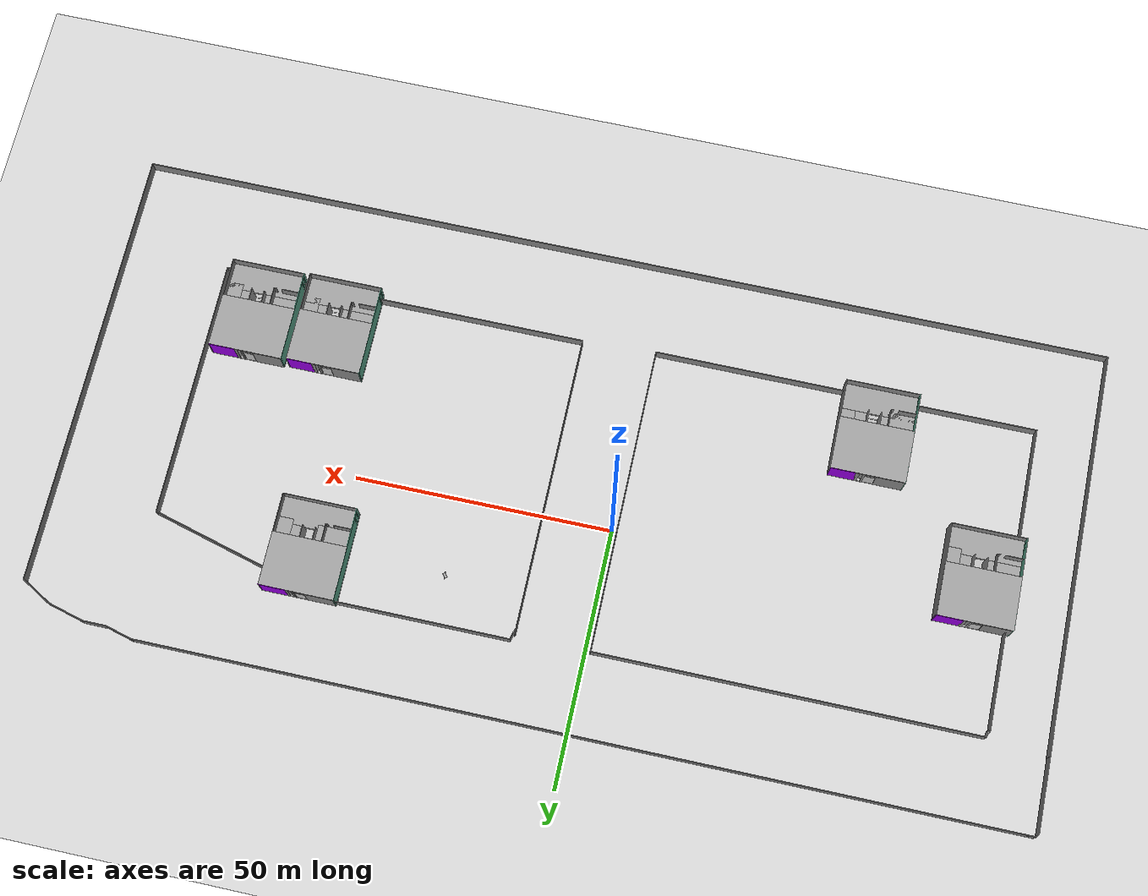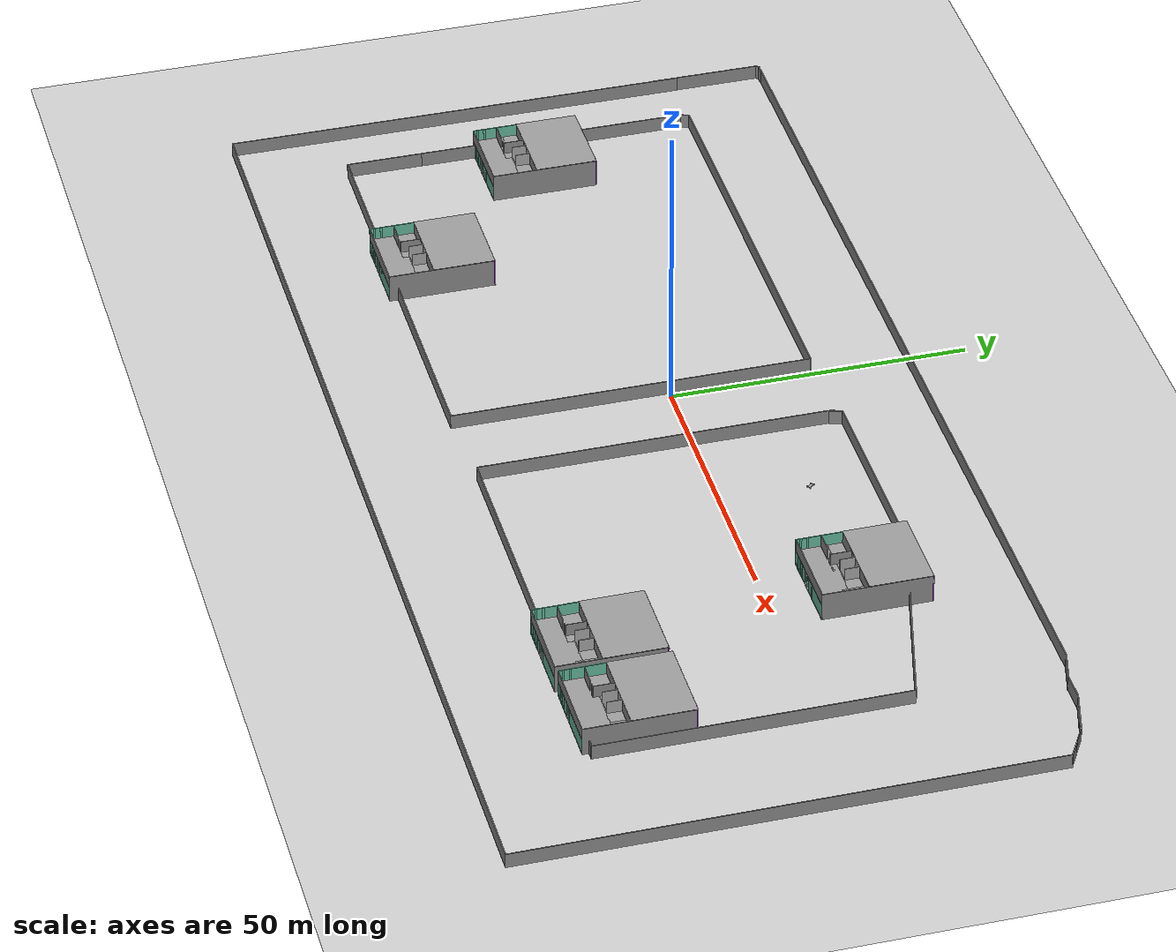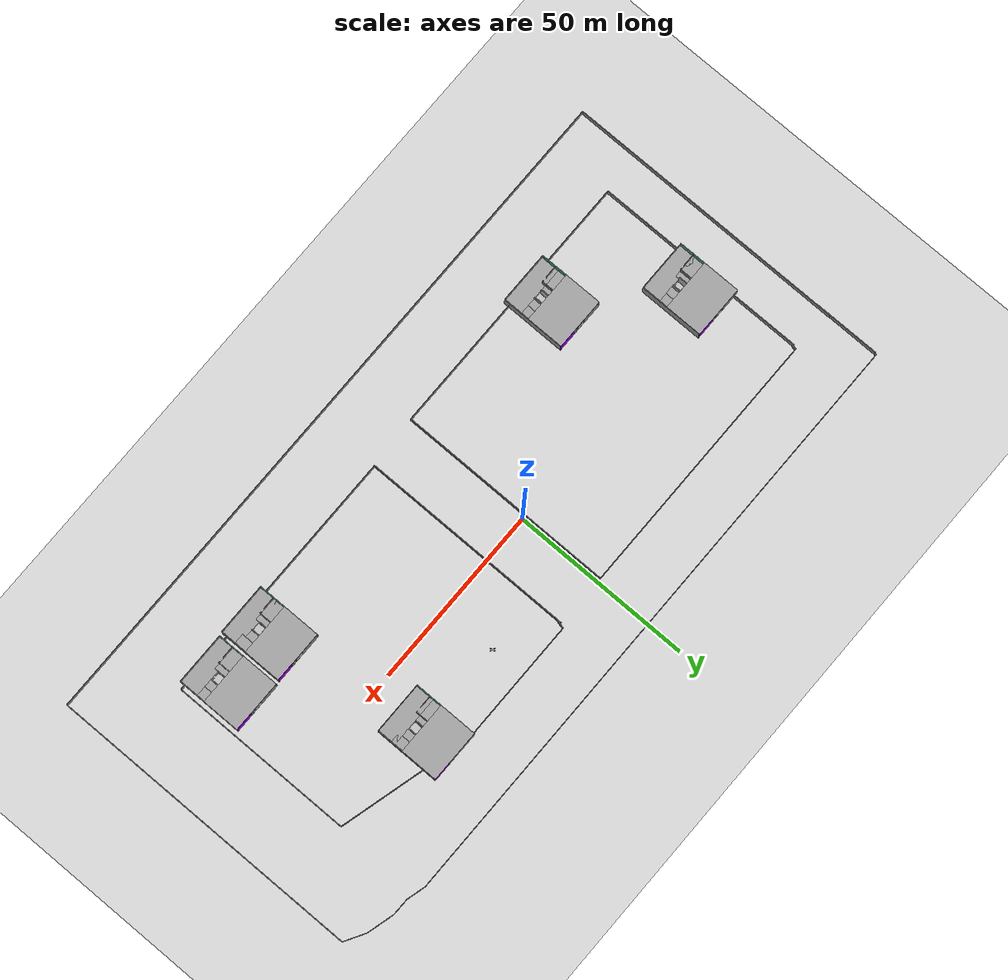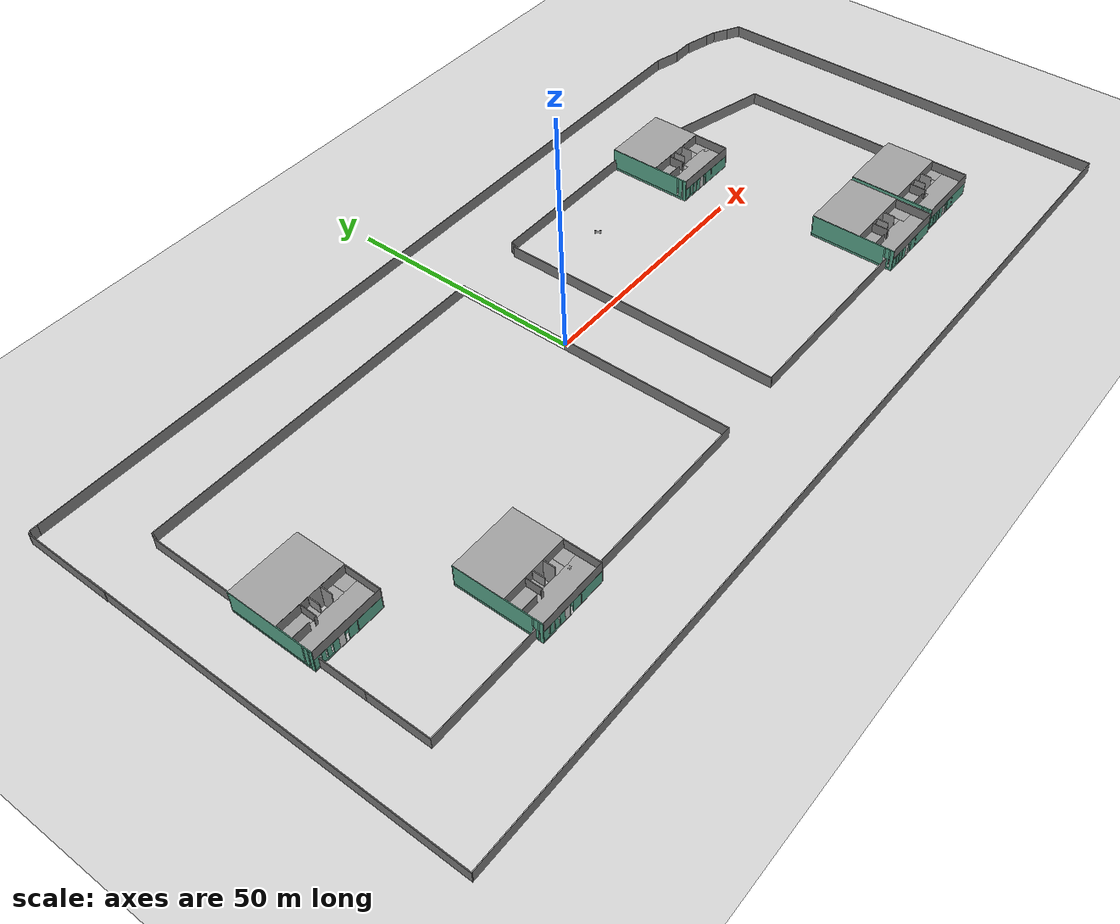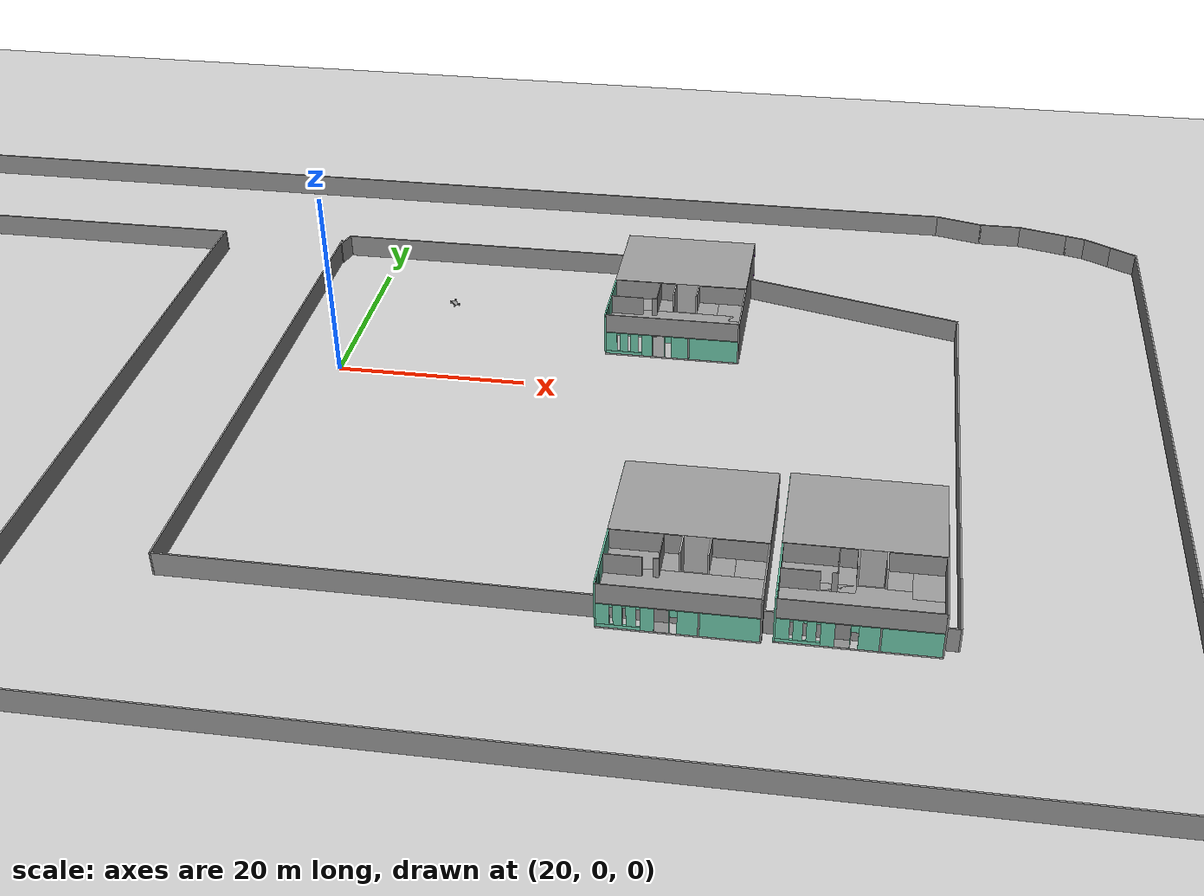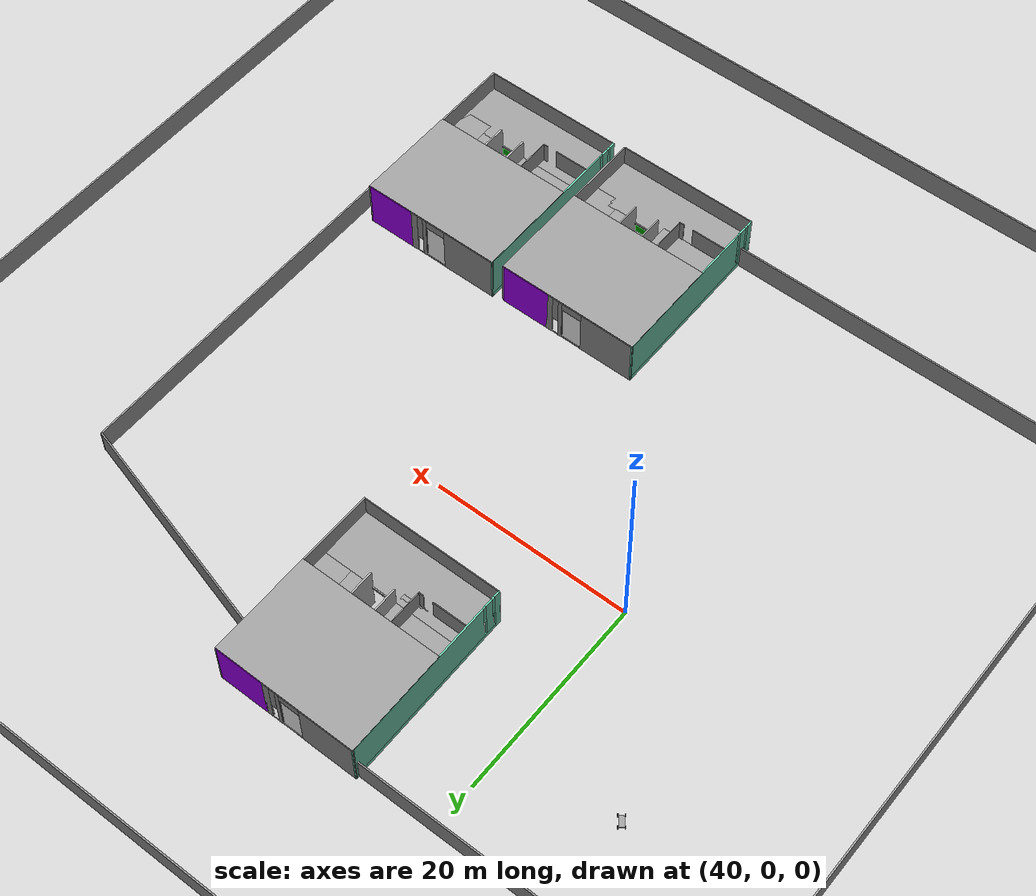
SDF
<sdf version="1.7">
 <world name="default">
  <light name="sun" type="directional">
   <pose>0 0 10 0 -0 0</pose>
   <diffuse>0.8 0.8 0.8 1</diffuse>
   <specular>0.2 0.2 0.2 1</specular>
   <attenuation>
    <range>1000</range>
    <constant>0.9</constant>
    <linear>0.01</linear>
    <quadratic>0.001</quadratic>
   </attenuation>
   <direction>-0.5 0.1 -0.9</direction>
   <spot><inner_angle>0</inner_angle><outer_angle>0</outer_angle><falloff>0</falloff></spot>
  </light>
  <model name="ground_plane">
   <static>1</static>
   <link name="link">
    <collision name="collision">
     <geometry><plane><normal>0 0 1</normal><size>300 300</size></plane></geometry>
     <surface><friction><ode><mu>100</mu><mu2>50</mu2></ode></friction></surface>
    </collision>
    <visual name="visual">
     <cast_shadows>0</cast_shadows>
     <geometry><plane><normal>0 0 1</normal><size>300 300</size></plane></geometry>
     <material>
      <script><uri>file://media/materials/scripts/gazebo.material</uri><name>Gazebo/Grey</name></script>
     </material>
    </visual>
   </link>
  </model>
  <gravity>0 0 -9.8</gravity>
  <magnetic_field>6e-06 2.3e-05 -4.2e-05</magnetic_field>
  <atmosphere type="adiabatic"/>
  <physics type="ode">
   <max_step_size>0.004</max_step_size>
   <real_time_factor>1</real_time_factor>
   <real_time_update_rate>250</real_time_update_rate>
  </physics>
  <scene><ambient>0.4 0.4 0.4 1</ambient><background>0.7 0.7 0.7 1</background><shadows>1</shadows></scene>
  <spherical_coordinates>
   <surface_model>EARTH_WGS84</surface_model>
   <latitude_deg>0</latitude_deg>
   <longitude_deg>0</longitude_deg>
   <elevation>0</elevation>
   <heading_deg>0</heading_deg>
  </spherical_coordinates>
  <model name="companywall">
   <pose>9.37494 -7.21654 0 0 -0 0</pose>
   <link name="Wall_0">
    <collision name="Wall_0_Collision">
     <geometry><box><size>29 0.15 2.5</size></box></geometry>
     <pose>0 0 1.25 0 -0 0</pose>
    </collision>
    <visual name="Wall_0_Visual">
     <pose>0 0 1.25 0 -0 0</pose>
     <geometry><box><size>29 0.15 2.5</size></box></geometry>
     <material>
      <script><uri>file://media/materials/scripts/gazebo.material</uri><name>Gazebo/Grey</name></script>
      <ambient>1 1 1 1</ambient>
     </material>
     <meta><layer>0</layer></meta>
    </visual>
    <pose>-84.9268 15.5781 0 0 -0 -1.5708</pose>
   </link>
   <link name="Wall_1">
    <collision name="Wall_1_Collision">
     <geometry><box><size>17.75 0.15 2.5</size></box></geometry>
     <pose>0 0 1.25 0 -0 0</pose>
    </collision>
    <visual name="Wall_1_Visual">
     <pose>0 0 1.25 0 -0 0</pose>
     <geometry><box><size>17.75 0.15 2.5</size></box></geometry>
     <material>
      <script><uri>file://media/materials/scripts/gazebo.material</uri><name>Gazebo/Grey</name></script>
      <ambient>1 1 1 1</ambient>
     </material>
     <meta><layer>0</layer></meta>
    </visual>
    <pose>-84.9268 -7.64687 0 0 -0 -1.5708</pose>
   </link>
   <link name="Wall_10">
    <collision name="Wall_10_Collision">
     <geometry><box><size>51 0.15 2.5</size></box></geometry>
     <pose>0 0 1.25 0 -0 0</pose>
    </collision>
    <visual name="Wall_10_Visual">
     <pose>0 0 1.25 0 -0 0</pose>
     <geometry><box><size>51 0.15 2.5</size></box></geometry>
     <material>
      <script><uri>file://media/materials/scripts/gazebo.material</uri><name>Gazebo/Grey</name></script>
      <ambient>1 1 1 1</ambient>
     </material>
     <meta><layer>0</layer></meta>
    </visual>
    <pose>75.708 -3.11663 0 0 -0 1.5708</pose>
   </link>
   <link name="Wall_11">
    <collision name="Wall_11_Collision">
     <geometry><box><size>37.5 0.15 2.5</size></box></geometry>
     <pose>0 0 1.25 0 -0 0</pose>
    </collision>
    <visual name="Wall_11_Visual">
     <pose>0 0 1.25 0 -0 0</pose>
     <geometry><box><size>37.5 0.15 2.5</size></box></geometry>
     <material>
      <script><uri>file://media/materials/scripts/gazebo.material</uri><name>Gazebo/Grey</name></script>
      <ambient>1 1 1 1</ambient>
     </material>
     <meta><layer>0</layer></meta>
    </visual>
    <pose>57.6694 27.1418 0 0 -0 2.87979</pose>
   </link>
   <link name="Wall_12">
    <collision name="Wall_12_Collision">
     <geometry><box><size>35 0.15 2.5</size></box></geometry>
     <pose>0 0 1.25 0 -0 0</pose>
    </collision>
    <visual name="Wall_12_Visual">
     <pose>0 0 1.25 0 -0 0</pose>
     <geometry><box><size>35 0.15 2.5</size></box></geometry>
     <material>
      <script><uri>file://media/materials/scripts/gazebo.material</uri><name>Gazebo/Grey</name></script>
      <ambient>1 1 1 1</ambient>
     </material>
     <meta><layer>0</layer></meta>
    </visual>
    <pose>22.2057 31.9753 0 0 -0 3.14159</pose>
   </link>
   <link name="Wall_13">
    <collision name="Wall_13_Collision">
     <geometry><box><size>2.25 0.15 2.5</size></box></geometry>
     <pose>0 0 1.25 0 -0 0</pose>
    </collision>
    <visual name="Wall_13_Visual">
     <pose>0 0 1.25 0 -0 0</pose>
     <geometry><box><size>2.25 0.15 2.5</size></box></geometry>
     <material>
      <script><uri>file://media/materials/scripts/gazebo.material</uri><name>Gazebo/Grey</name></script>
      <ambient>1 1 1 1</ambient>
     </material>
     <meta><layer>0</layer></meta>
    </visual>
    <pose>4.50894 30.961 0 0 -0 -1.8326</pose>
   </link>
   <link name="Wall_15">
    <collision name="Wall_15_Collision">
     <geometry><box><size>79.25 0.15 2.5</size></box></geometry>
     <pose>0 0 1.25 0 -0 0</pose>
    </collision>
    <visual name="Wall_15_Visual">
     <pose>0 0 1.25 0 -0 0</pose>
     <geometry><box><size>79.25 0.15 2.5</size></box></geometry>
     <material>
      <script><uri>file://media/materials/scripts/gazebo.material</uri><name>Gazebo/Grey</name></script>
      <ambient>1 1 1 1</ambient>
     </material>
     <meta><layer>0</layer></meta>
    </visual>
    <pose>-96.2655 -7.44183 0 0 -0 -1.5708</pose>
   </link>
   <link name="Wall_16">
    <collision name="Wall_16_Collision">
     <geometry><box><size>192.75 0.15 2.5</size></box></geometry>
     <pose>0 0 1.25 0 -0 0</pose>
    </collision>
    <visual name="Wall_16_Visual">
     <pose>0 0 1.25 0 -0 0</pose>
     <geometry><box><size>192.75 0.15 2.5</size></box></geometry>
     <material>
      <script><uri>file://media/materials/scripts/gazebo.material</uri><name>Gazebo/Grey</name></script>
      <ambient>1 1 1 1</ambient>
     </material>
     <meta><layer>0</layer></meta>
    </visual>
    <pose>0.03454 -46.9918 0 0 -0 0</pose>
   </link>
   <link name="Wall_17">
    <collision name="Wall_17_Collision">
     <geometry><box><size>87.5 0.15 2.5</size></box></geometry>
     <pose>0 0 1.25 0 -0 0</pose>
    </collision>
    <visual name="Wall_17_Visual">
     <pose>0 0 1.25 0 -0 0</pose>
     <geometry><box><size>87.5 0.15 2.5</size></box></geometry>
     <material>
      <script><uri>file://media/materials/scripts/gazebo.material</uri><name>Gazebo/Grey</name></script>
      <ambient>1 1 1 1</ambient>
     </material>
     <meta><layer>0</layer></meta>
    </visual>
    <pose>96.3345 -3.31683 0 0 -0 1.5708</pose>
   </link>
   <link name="Wall_18">
    <collision name="Wall_18_Collision">
     <geometry><box><size>3.25 0.15 2.5</size></box></geometry>
     <pose>0 0 1.25 0 -0 0</pose>
    </collision>
    <visual name="Wall_18_Visual">
     <pose>0 0 1.25 0 -0 0</pose>
     <geometry><box><size>3.25 0.15 2.5</size></box></geometry>
     <material>
      <script><uri>file://media/materials/scripts/gazebo.material</uri><name>Gazebo/Grey</name></script>
      <ambient>1 1 1 1</ambient>
     </material>
     <meta><layer>0</layer></meta>
    </visual>
    <pose>94.9922 41.1332 0 0 -0 2.61799</pose>
   </link>
   <link name="Wall_19">
    <collision name="Wall_19_Collision">
     <geometry><box><size>3.5 0.15 2.5</size></box></geometry>
     <pose>0 0 1.25 0 -0 0</pose>
    </collision>
    <visual name="Wall_19_Visual">
     <pose>0 0 1.25 0 -0 0</pose>
     <geometry><box><size>3.5 0.15 2.5</size></box></geometry>
     <material>
      <script><uri>file://media/materials/scripts/gazebo.material</uri><name>Gazebo/Grey</name></script>
      <ambient>1 1 1 1</ambient>
     </material>
     <meta><layer>0</layer></meta>
    </visual>
    <pose>92.1993 42.7457 0 0 -0 2.61799</pose>
   </link>
   <link name="Wall_2">
    <collision name="Wall_2_Collision">
     <geometry><box><size>13 0.15 2.5</size></box></geometry>
     <pose>0 0 1.25 0 -0 0</pose>
    </collision>
    <visual name="Wall_2_Visual">
     <pose>0 0 1.25 0 -0 0</pose>
     <geometry><box><size>13 0.15 2.5</size></box></geometry>
     <material>
      <script><uri>file://media/materials/scripts/gazebo.material</uri><name>Gazebo/Grey</name></script>
      <ambient>1 1 1 1</ambient>
     </material>
     <meta><layer>0</layer></meta>
    </visual>
    <pose>-84.9268 -22.8719 0 0 -0 -1.5708</pose>
   </link>
   <link name="Wall_20">
    <collision name="Wall_20_Collision">
     <geometry><box><size>2.25 0.15 2.5</size></box></geometry>
     <pose>0 0 1.25 0 -0 0</pose>
    </collision>
    <visual name="Wall_20_Visual">
     <pose>0 0 1.25 0 -0 0</pose>
     <geometry><box><size>2.25 0.15 2.5</size></box></geometry>
     <material>
      <script><uri>file://media/materials/scripts/gazebo.material</uri><name>Gazebo/Grey</name></script>
      <ambient>1 1 1 1</ambient>
     </material>
     <meta><layer>0</layer></meta>
    </visual>
    <pose>89.7345 43.8549 0 0 -0 2.87979</pose>
   </link>
   <link name="Wall_21">
    <collision name="Wall_21_Collision">
     <geometry><box><size>5.75 0.15 2.5</size></box></geometry>
     <pose>0 0 1.25 0 -0 0</pose>
    </collision>
    <visual name="Wall_21_Visual">
     <pose>0 0 1.25 0 -0 0</pose>
     <geometry><box><size>5.75 0.15 2.5</size></box></geometry>
     <material>
      <script><uri>file://media/materials/scripts/gazebo.material</uri><name>Gazebo/Grey</name></script>
      <ambient>1 1 1 1</ambient>
     </material>
     <meta><layer>0</layer></meta>
    </visual>
    <pose>86.0156 44.8514 0 0 -0 2.87979</pose>
   </link>
   <link name="Wall_22">
    <collision name="Wall_22_Collision">
     <geometry><box><size>4.75 0.15 2.5</size></box></geometry>
     <pose>0 0 1.25 0 -0 0</pose>
    </collision>
    <visual name="Wall_22_Visual">
     <pose>0 0 1.25 0 -0 0</pose>
     <geometry><box><size>4.75 0.15 2.5</size></box></geometry>
     <material>
      <script><uri>file://media/materials/scripts/gazebo.material</uri><name>Gazebo/Grey</name></script>
      <ambient>1 1 1 1</ambient>
     </material>
     <meta><layer>0</layer></meta>
    </visual>
    <pose>81.011 45.5761 0 0 -0 3.14159</pose>
   </link>
   <link name="Wall_23">
    <collision name="Wall_23_Collision">
     <geometry><box><size>5.5 0.15 2.5</size></box></geometry>
     <pose>0 0 1.25 0 -0 0</pose>
    </collision>
    <visual name="Wall_23_Visual">
     <pose>0 0 1.25 0 -0 0</pose>
     <geometry><box><size>5.5 0.15 2.5</size></box></geometry>
     <material>
      <script><uri>file://media/materials/scripts/gazebo.material</uri><name>Gazebo/Grey</name></script>
      <ambient>1 1 1 1</ambient>
     </material>
     <meta><layer>0</layer></meta>
    </visual>
    <pose>76.1272 46.2684 0 0 -0 2.87979</pose>
   </link>
   <link name="Wall_24">
    <collision name="Wall_24_Collision">
     <geometry><box><size>168.25 0.15 2.5</size></box></geometry>
     <pose>0 0 1.25 0 -0 0</pose>
    </collision>
    <visual name="Wall_24_Visual">
     <pose>0 0 1.25 0 -0 0</pose>
     <geometry><box><size>168.25 0.15 2.5</size></box></geometry>
     <material>
      <script><uri>file://media/materials/scripts/gazebo.material</uri><name>Gazebo/Grey</name></script>
      <ambient>1 1 1 1</ambient>
     </material>
     <meta><layer>0</layer></meta>
    </visual>
    <pose>-10.5067 46.9608 0 0 -0 3.14159</pose>
   </link>
   <link name="Wall_25">
    <collision name="Wall_25_Collision">
     <geometry><box><size>1.5 0.15 2.5</size></box></geometry>
     <pose>0 0 1.25 0 -0 0</pose>
    </collision>
    <visual name="Wall_25_Visual">
     <pose>0 0 1.25 0 -0 0</pose>
     <geometry><box><size>1.5 0.15 2.5</size></box></geometry>
     <material>
      <script><uri>file://media/materials/scripts/gazebo.material</uri><name>Gazebo/Grey</name></script>
      <ambient>1 1 1 1</ambient>
     </material>
     <meta><layer>0</layer></meta>
    </visual>
    <pose>-95.2317 46.9608 0 0 -0 3.14159</pose>
   </link>
   <link name="Wall_26">
    <collision name="Wall_26_Collision">
     <geometry><box><size>0.75 0.15 2.5</size></box></geometry>
     <pose>0 0 1.25 0 -0 0</pose>
    </collision>
    <visual name="Wall_26_Visual">
     <pose>0 0 1.25 0 -0 0</pose>
     <geometry><box><size>0.75 0.15 2.5</size></box></geometry>
     <material>
      <script><uri>file://media/materials/scripts/gazebo.material</uri><name>Gazebo/Grey</name></script>
      <ambient>1 1 1 1</ambient>
     </material>
     <meta><layer>0</layer></meta>
    </visual>
    <pose>-96.1188 46.7486 0 0 -0 -2.35619</pose>
   </link>
   <link name="Wall_27">
    <collision name="Wall_27_Collision">
     <geometry><box><size>18.75 0.15 2.5</size></box></geometry>
     <pose>0 0 1.25 0 -0 0</pose>
    </collision>
    <visual name="Wall_27_Visual">
     <pose>0 0 1.25 0 -0 0</pose>
     <geometry><box><size>18.75 0.15 2.5</size></box></geometry>
     <material>
      <script><uri>file://media/materials/scripts/gazebo.material</uri><name>Gazebo/Grey</name></script>
      <ambient>1 1 1 1</ambient>
     </material>
     <meta><layer>0</layer></meta>
    </visual>
    <pose>-96.3309 37.2365 0 0 -0 -1.5708</pose>
   </link>
   <link name="Wall_3">
    <collision name="Wall_3_Collision">
     <geometry><box><size>74.75 0.15 2.5</size></box></geometry>
     <pose>0 0 1.25 0 -0 0</pose>
    </collision>
    <visual name="Wall_3_Visual">
     <pose>0 0 1.25 0 -0 0</pose>
     <geometry><box><size>74.75 0.15 2.5</size></box></geometry>
     <material>
      <script><uri>file://media/materials/scripts/gazebo.material</uri><name>Gazebo/Grey</name></script>
      <ambient>1 1 1 1</ambient>
     </material>
     <meta><layer>0</layer></meta>
    </visual>
    <pose>-47.6268 -29.2969 0 0 -0 0</pose>
   </link>
   <link name="Wall_4">
    <collision name="Wall_4_Collision">
     <geometry><box><size>60.5 0.15 2.5</size></box></geometry>
     <pose>0 0 1.25 0 -0 0</pose>
    </collision>
    <visual name="Wall_4_Visual">
     <pose>0 0 1.25 0 -0 0</pose>
     <geometry><box><size>60.5 0.15 2.5</size></box></geometry>
     <material>
      <script><uri>file://media/materials/scripts/gazebo.material</uri><name>Gazebo/Grey</name></script>
      <ambient>1 1 1 1</ambient>
     </material>
     <meta><layer>0</layer></meta>
    </visual>
    <pose>-10.3268 0.878135 0 0 -0 1.5708</pose>
   </link>
   <link name="Wall_5">
    <collision name="Wall_5_Collision">
     <geometry><box><size>74.25 0.15 2.5</size></box></geometry>
     <pose>0 0 1.25 0 -0 0</pose>
    </collision>
    <visual name="Wall_5_Visual">
     <pose>0 0 1.25 0 -0 0</pose>
     <geometry><box><size>74.25 0.15 2.5</size></box></geometry>
     <material>
      <script><uri>file://media/materials/scripts/gazebo.material</uri><name>Gazebo/Grey</name></script>
      <ambient>1 1 1 1</ambient>
     </material>
     <meta><layer>0</layer></meta>
    </visual>
    <pose>-47.3768 31.0531 0 0 -0 3.14159</pose>
   </link>
   <link name="Wall_6">
    <collision name="Wall_6_Collision">
     <geometry><box><size>1.5 0.15 2.5</size></box></geometry>
     <pose>0 0 1.25 0 -0 0</pose>
    </collision>
    <visual name="Wall_6_Visual">
     <pose>0 0 1.25 0 -0 0</pose>
     <geometry><box><size>1.5 0.15 2.5</size></box></geometry>
     <material>
      <script><uri>file://media/materials/scripts/gazebo.material</uri><name>Gazebo/Grey</name></script>
      <ambient>1 1 1 1</ambient>
     </material>
     <meta><layer>0</layer></meta>
    </visual>
    <pose>-84.6015 30.4011 0 0 -0 -1.8326</pose>
   </link>
   <link name="Wall_8">
    <collision name="Wall_8_Collision">
     <geometry><box><size>59.5 0.15 2.5</size></box></geometry>
     <pose>0 0 1.25 0 -0 0</pose>
    </collision>
    <visual name="Wall_8_Visual">
     <pose>0 0 1.25 0 -0 0</pose>
     <geometry><box><size>59.5 0.15 2.5</size></box></geometry>
     <material>
      <script><uri>file://media/materials/scripts/gazebo.material</uri><name>Gazebo/Grey</name></script>
      <ambient>1 1 1 1</ambient>
     </material>
     <meta><layer>0</layer></meta>
    </visual>
    <pose>4.10803 1.13337 0 0 -0 -1.5708</pose>
   </link>
   <link name="Wall_9">
    <collision name="Wall_9_Collision">
     <geometry><box><size>71.75 0.15 2.5</size></box></geometry>
     <pose>0 0 1.25 0 -0 0</pose>
    </collision>
    <visual name="Wall_9_Visual">
     <pose>0 0 1.25 0 -0 0</pose>
     <geometry><box><size>71.75 0.15 2.5</size></box></geometry>
     <material>
      <script><uri>file://media/materials/scripts/gazebo.material</uri><name>Gazebo/Grey</name></script>
      <ambient>1 1 1 1</ambient>
     </material>
     <meta><layer>0</layer></meta>
    </visual>
    <pose>39.908 -28.5416 0 0 -0 0</pose>
   </link>
   <static>1</static>
  </model>
  <model name="cart_front_steer">
   <link name="chassis">
    <pose>0 0 0.15 0 -0 0</pose>
    <inertial>
     <pose>0.1 0 0 0 -0 0</pose>
     <mass>10</mass>
     <inertia>
      <ixx>0.216667</ixx>
      <iyy>0.841667</iyy>
      <izz>1.04167</izz>
      <ixy>0</ixy>
      <ixz>0</ixz>
      <iyz>0</iyz>
     </inertia>
    </inertial>
    <collision name="collision"><geometry><box><size>1 0.5 0.1</size></box></geometry></collision>
    <visual name="visual">
     <geometry><box><size>1 0.5 0.1</size></box></geometry>
     <material>
      <script><uri>file://media/materials/scripts/gazebo.material</uri><name>Gazebo/Grey</name></script>
     </material>
    </visual>
   </link>
   <link name="wheel_front_left">
    <pose>0.5 0.298 0.15 -1.5708 -0.087266 0</pose>
    <inertial>
     <mass>0.5</mass>
     <inertia>
      <ixx>0.00307917</ixx>
      <iyy>0.00307917</iyy>
      <izz>0.005625</izz>
      <ixy>0</ixy>
      <ixz>0</ixz>
      <iyz>0</iyz>
     </inertia>
    </inertial>
    <collision name="collision">
     <geometry><cylinder><radius>0.15</radius><length>0.08</length></cylinder></geometry>
    </collision>
    <visual name="visual">
     <geometry><cylinder><radius>0.15</radius><length>0.08</length></cylinder></geometry>
     <material>
      <script><uri>file://media/materials/scripts/gazebo.material</uri><name>Gazebo/Black</name></script>
     </material>
    </visual>
   </link>
   <joint name="wheel_front_left_steer_spin" type="universal">
    <parent>chassis</parent>
    <child>wheel_front_left</child>
    <axis>
     <xyz>0 -1 0</xyz>
     <limit><lower>-0.610865</lower><upper>0.610865</upper></limit>
     <dynamics><spring_reference>0</spring_reference><spring_stiffness>0</spring_stiffness></dynamics>
    </axis>
    <axis2>
     <xyz>0 0 1</xyz>
     <limit><upper>1e+16</upper><lower>-1e+16</lower></limit>
     <dynamics><spring_reference>0</spring_reference><spring_stiffness>0</spring_stiffness></dynamics>
    </axis2>
   </joint>
   <link name="wheel_front_right">
    <pose>0.5 -0.298 0.15 -1.5708 -0.087266 0</pose>
    <inertial>
     <mass>0.5</mass>
     <inertia>
      <ixx>0.00307917</ixx>
      <iyy>0.00307917</iyy>
      <izz>0.005625</izz>
      <ixy>0</ixy>
      <ixz>0</ixz>
      <iyz>0</iyz>
     </inertia>
    </inertial>
    <collision name="collision">
     <geometry><cylinder><radius>0.15</radius><length>0.08</length></cylinder></geometry>
    </collision>
    <visual name="visual">
     <geometry><cylinder><radius>0.15</radius><length>0.08</length></cylinder></geometry>
     <material>
      <script><uri>file://media/materials/scripts/gazebo.material</uri><name>Gazebo/Black</name></script>
     </material>
    </visual>
   </link>
   <joint name="wheel_front_right_steer_spin" type="universal">
    <parent>chassis</parent>
    <child>wheel_front_right</child>
    <axis>
     <xyz>0 -1 0</xyz>
     <limit><lower>-0.610865</lower><upper>0.610865</upper></limit>
     <dynamics><spring_reference>0</spring_reference><spring_stiffness>0</spring_stiffness></dynamics>
    </axis>
    <axis2>
     <xyz>0 0 1</xyz>
     <limit><upper>1e+16</upper><lower>-1e+16</lower></limit>
     <dynamics><spring_reference>0</spring_reference><spring_stiffness>0</spring_stiffness></dynamics>
    </axis2>
   </joint>
   <link name="wheel_rear_left">
    <pose>-0.5 0.298 0.15 -1.5708 0 0</pose>
    <inertial>
     <mass>0.5</mass>
     <inertia>
      <ixx>0.00307917</ixx>
      <iyy>0.00307917</iyy>
      <izz>0.005625</izz>
      <ixy>0</ixy>
      <ixz>0</ixz>
      <iyz>0</iyz>
     </inertia>
    </inertial>
    <collision name="collision">
     <geometry><cylinder><radius>0.15</radius><length>0.08</length></cylinder></geometry>
    </collision>
    <visual name="visual">
     <geometry><cylinder><radius>0.15</radius><length>0.08</length></cylinder></geometry>
     <material>
      <script><uri>file://media/materials/scripts/gazebo.material</uri><name>Gazebo/Black</name></script>
     </material>
    </visual>
   </link>
   <joint name="wheel_rear_left_spin" type="revolute">
    <parent>chassis</parent>
    <child>wheel_rear_left</child>
    <axis>
     <xyz>0 0 1</xyz>
     <limit><lower>-1e+16</lower><upper>1e+16</upper></limit>
     <dynamics><spring_reference>0</spring_reference><spring_stiffness>0</spring_stiffness></dynamics>
    </axis>
   </joint>
   <link name="wheel_rear_right">
    <pose>-0.5 -0.298 0.15 -1.5708 0 0</pose>
    <inertial>
     <mass>0.5</mass>
     <inertia>
      <ixx>0.00307917</ixx>
      <iyy>0.00307917</iyy>
      <izz>0.005625</izz>
      <ixy>0</ixy>
      <ixz>0</ixz>
      <iyz>0</iyz>
     </inertia>
    </inertial>
    <collision name="collision">
     <geometry><cylinder><radius>0.15</radius><length>0.08</length></cylinder></geometry>
    </collision>
    <visual name="visual">
     <geometry><cylinder><radius>0.15</radius><length>0.08</length></cylinder></geometry>
     <material>
      <script><uri>file://media/materials/scripts/gazebo.material</uri><name>Gazebo/Black</name></script>
     </material>
    </visual>
   </link>
   <joint name="wheel_rear_right_spin" type="revolute">
    <parent>chassis</parent>
    <child>wheel_rear_right</child>
    <axis>
     <xyz>0 0 1</xyz>
     <limit><lower>-1e+16</lower><upper>1e+16</upper></limit>
     <dynamics><spring_reference>0</spring_reference><spring_stiffness>0</spring_stiffness></dynamics>
    </axis>
   </joint>
   <pose>28.9896 15.0815 0.003916 -0.000147 -0.011451 -0.932765</pose>
  </model>
  <model name="osrf_elevator">
   <link name="Wall_0">
    <pose>-7.17647 0.013004 0 0 -0 1.57174</pose>
    <visual name="Wall_0_Visual_0">
     <meta><layer>0</layer></meta>
     <pose>-8.72596 0 2.4385 0 -0 0</pose>
     <geometry><box><size>0.663656 0.15 4.877</size></box></geometry>
     <material>
      <script><uri>file://media/materials/scripts/gazebo.material</uri><name>Gazebo/Grey</name></script>
      <ambient>0.435294 0.796078 0.67451 1</ambient>
     </material>
    </visual>
    <collision name="Wall_0_Collision_0">
     <geometry><box><size>0.663656 0.15 4.877</size></box></geometry>
     <pose>-8.72596 0 2.4385 0 -0 0</pose>
    </collision>
    <visual name="Wall_0_Visual_1">
     <meta><layer>0</layer></meta>
     <pose>0.331828 0 0.25 0 -0 0</pose>
     <geometry><box><size>17.4519 0.15 0.5</size></box></geometry>
     <material>
      <script><uri>file://media/materials/scripts/gazebo.material</uri><name>Gazebo/Grey</name></script>
      <ambient>0.435294 0.796078 0.67451 1</ambient>
     </material>
    </visual>
    <collision name="Wall_0_Collision_1">
     <geometry><box><size>17.4519 0.15 0.5</size></box></geometry>
     <pose>0.331828 0 0.25 0 -0 0</pose>
    </collision>
    <visual name="Wall_0_Visual_2">
     <meta><layer>0</layer></meta>
     <pose>-7.67281 0 2.6885 0 -0 0</pose>
     <geometry><box><size>0.816657 0.15 4.377</size></box></geometry>
     <material>
      <script><uri>file://media/materials/scripts/gazebo.material</uri><name>Gazebo/Grey</name></script>
      <ambient>0.435294 0.796078 0.67451 1</ambient>
     </material>
    </visual>
    <collision name="Wall_0_Collision_2">
     <geometry><box><size>0.816657 0.15 4.377</size></box></geometry>
     <pose>-7.67281 0 2.6885 0 -0 0</pose>
    </collision>
    <visual name="Wall_0_Visual_3">
     <meta><layer>0</layer></meta>
     <pose>1.05709 0 2.6885 0 -0 0</pose>
     <geometry><box><size>16.0014 0.15 4.377</size></box></geometry>
     <material>
      <script><uri>file://media/materials/scripts/gazebo.material</uri><name>Gazebo/Grey</name></script>
      <ambient>0.435294 0.796078 0.67451 1</ambient>
     </material>
    </visual>
    <collision name="Wall_0_Collision_3">
     <geometry><box><size>16.0014 0.15 4.377</size></box></geometry>
     <pose>1.05709 0 2.6885 0 -0 0</pose>
    </collision>
    <visual name="Wall_0_Visual_4">
     <meta><layer>0</layer></meta>
     <pose>-8.23763 0 3.6885 0 -0 0</pose>
     <geometry><box><size>0.313 0.15 2.377</size></box></geometry>
     <material>
      <script><uri>file://media/materials/scripts/gazebo.material</uri><name>Gazebo/Grey</name></script>
      <ambient>0.435294 0.796078 0.67451 1</ambient>
     </material>
    </visual>
    <collision name="Wall_0_Collision_4">
     <geometry><box><size>0.313 0.15 2.377</size></box></geometry>
     <pose>-8.23763 0 3.6885 0 -0 0</pose>
    </collision>
    <visual name="Wall_0_Visual_5">
     <meta><layer>0</layer></meta>
     <pose>-7.10405 0 3.6885 0 -0 0</pose>
     <geometry><box><size>0.320861 0.15 2.377</size></box></geometry>
     <material>
      <script><uri>file://media/materials/scripts/gazebo.material</uri><name>Gazebo/Grey</name></script>
      <ambient>0.435294 0.796078 0.67451 1</ambient>
     </material>
    </visual>
    <collision name="Wall_0_Collision_5">
     <geometry><box><size>0.320861 0.15 2.377</size></box></geometry>
     <pose>-7.10405 0 3.6885 0 -0 0</pose>
    </collision>
   </link>
   <link name="Wall_10">
    <pose>3.11003 -4.9485 0 0 -0 0</pose>
    <visual name="Wall_10_Visual_0">
     <meta><layer>0</layer></meta>
     <pose>-1.73626 0 1.3715 0 -0 0</pose>
     <geometry><box><size>4.52747 0.15 2.743</size></box></geometry>
     <material>
      <script><uri>file://media/materials/scripts/gazebo.material</uri><name>Gazebo/Grey</name></script>
      <ambient>0 0.666667 0 1</ambient>
     </material>
    </visual>
    <collision name="Wall_10_Collision_0">
     <geometry><box><size>4.52747 0.15 2.743</size></box></geometry>
     <pose>-1.73626 0 1.3715 0 -0 0</pose>
    </collision>
    <visual name="Wall_10_Visual_1">
     <meta><layer>0</layer></meta>
     <pose>2.58694 0 1.3715 0 -0 0</pose>
     <geometry><box><size>2.82611 0.15 2.743</size></box></geometry>
     <material>
      <script><uri>file://media/materials/scripts/gazebo.material</uri><name>Gazebo/Grey</name></script>
      <ambient>0 0.666667 0 1</ambient>
     </material>
    </visual>
    <collision name="Wall_10_Collision_1">
     <geometry><box><size>2.82611 0.15 2.743</size></box></geometry>
     <pose>2.58694 0 1.3715 0 -0 0</pose>
    </collision>
    <visual name="Wall_10_Visual_2">
     <meta><layer>0</layer></meta>
     <pose>0.85068 0 2.3715 0 -0 0</pose>
     <geometry><box><size>0.646413 0.15 0.743</size></box></geometry>
     <material>
      <script><uri>file://media/materials/scripts/gazebo.material</uri><name>Gazebo/Grey</name></script>
      <ambient>0 0.666667 0 1</ambient>
     </material>
    </visual>
    <collision name="Wall_10_Collision_2">
     <geometry><box><size>0.646413 0.15 0.743</size></box></geometry>
     <pose>0.85068 0 2.3715 0 -0 0</pose>
    </collision>
   </link>
   <link name="Wall_14">
    <pose>1.83803 -6.9775 0 0 -0 1.5708</pose>
    <visual name="Wall_14_Visual_0">
     <meta><layer>0</layer></meta>
     <pose>-0.387674 0 1.3715 0 -0 0</pose>
     <geometry><box><size>3.41138 0.15 2.743</size></box></geometry>
     <material>
      <script><uri>file://media/materials/scripts/gazebo.material</uri><name>Gazebo/Grey</name></script>
      <ambient>1 1 1 1</ambient>
     </material>
    </visual>
    <collision name="Wall_14_Collision_0">
     <geometry><box><size>3.41138 0.15 2.743</size></box></geometry>
     <pose>-0.387674 0 1.3715 0 -0 0</pose>
    </collision>
    <visual name="Wall_14_Visual_1">
     <meta><layer>0</layer></meta>
     <pose>2.00133 0 1.3715 0 -0 0</pose>
     <geometry><box><size>0.184063 0.15 2.743</size></box></geometry>
     <material>
      <script><uri>file://media/materials/scripts/gazebo.material</uri><name>Gazebo/Grey</name></script>
      <ambient>1 1 1 1</ambient>
     </material>
    </visual>
    <collision name="Wall_14_Collision_1">
     <geometry><box><size>0.184063 0.15 2.743</size></box></geometry>
     <pose>2.00133 0 1.3715 0 -0 0</pose>
    </collision>
    <visual name="Wall_14_Visual_2">
     <meta><layer>0</layer></meta>
     <pose>1.61366 0 2.3715 0 -0 0</pose>
     <geometry><box><size>0.591285 0.15 0.743</size></box></geometry>
     <material>
      <script><uri>file://media/materials/scripts/gazebo.material</uri><name>Gazebo/Grey</name></script>
      <ambient>1 1 1 1</ambient>
     </material>
    </visual>
    <collision name="Wall_14_Collision_2">
     <geometry><box><size>0.591285 0.15 0.743</size></box></geometry>
     <pose>1.61366 0 2.3715 0 -0 0</pose>
    </collision>
   </link>
   <link name="Wall_16">
    <collision name="Wall_16_Collision">
     <geometry><box><size>5.12727 0.15 2.743</size></box></geometry>
     <pose>0 0 1.3715 0 -0 0</pose>
    </collision>
    <visual name="Wall_16_Visual">
     <meta><layer>0</layer></meta>
     <pose>0 0 1.3715 0 -0 0</pose>
     <geometry><box><size>5.12727 0.15 2.743</size></box></geometry>
     <material>
      <script><uri>file://media/materials/scripts/gazebo.material</uri><name>Gazebo/Grey</name></script>
      <ambient>1 1 1 1</ambient>
     </material>
    </visual>
    <pose>-4.68247 -1.4425 0 0 -0 0</pose>
   </link>
   <link name="Wall_17">
    <pose>-2.19097 -3.185 0 0 0 -1.56907</pose>
    <visual name="Wall_17_Visual_0">
     <meta><layer>0</layer></meta>
     <pose>-1.22855 0 1.3715 0 -0 0</pose>
     <geometry><box><size>1.17851 0.15 2.743</size></box></geometry>
     <material>
      <script><uri>file://media/materials/scripts/gazebo.material</uri><name>Gazebo/Grey</name></script>
      <ambient>1 1 1 1</ambient>
     </material>
    </visual>
    <collision name="Wall_17_Collision_0">
     <geometry><box><size>1.17851 0.15 2.743</size></box></geometry>
     <pose>-1.22855 0 1.3715 0 -0 0</pose>
    </collision>
    <visual name="Wall_17_Visual_1">
     <meta><layer>0</layer></meta>
     <pose>0.886237 0 1.3715 0 -0 0</pose>
     <geometry><box><size>1.86314 0.15 2.743</size></box></geometry>
     <material>
      <script><uri>file://media/materials/scripts/gazebo.material</uri><name>Gazebo/Grey</name></script>
      <ambient>1 1 1 1</ambient>
     </material>
    </visual>
    <collision name="Wall_17_Collision_1">
     <geometry><box><size>1.86314 0.15 2.743</size></box></geometry>
     <pose>0.886237 0 1.3715 0 -0 0</pose>
    </collision>
    <visual name="Wall_17_Visual_2">
     <meta><layer>0</layer></meta>
     <pose>1.18873 0 1.3715 0 -0 0</pose>
     <geometry><box><size>1.25815 0.15 2.743</size></box></geometry>
     <material>
      <script><uri>file://media/materials/scripts/gazebo.material</uri><name>Gazebo/Grey</name></script>
      <ambient>1 1 1 1</ambient>
     </material>
    </visual>
    <collision name="Wall_17_Collision_2">
     <geometry><box><size>1.25815 0.15 2.743</size></box></geometry>
     <pose>1.18873 0 1.3715 0 -0 0</pose>
    </collision>
    <visual name="Wall_17_Visual_3">
     <meta><layer>0</layer></meta>
     <pose>-0.345304 0 2.3715 0 -0 0</pose>
     <geometry><box><size>0.587991 0.15 0.743</size></box></geometry>
     <material>
      <script><uri>file://media/materials/scripts/gazebo.material</uri><name>Gazebo/Grey</name></script>
      <ambient>1 1 1 1</ambient>
     </material>
    </visual>
    <collision name="Wall_17_Collision_3">
     <geometry><box><size>0.587991 0.15 0.743</size></box></geometry>
     <pose>-0.345304 0 2.3715 0 -0 0</pose>
    </collision>
   </link>
   <link name="Wall_18">
    <collision name="Wall_18_Collision">
     <geometry><box><size>5 0.15 2.743</size></box></geometry>
     <pose>0 0 1.3715 0 -0 0</pose>
    </collision>
    <visual name="Wall_18_Visual">
     <meta><layer>0</layer></meta>
     <pose>0 0 1.3715 0 -0 0</pose>
     <geometry><box><size>5 0.15 2.743</size></box></geometry>
     <material>
      <script><uri>file://media/materials/scripts/gazebo.material</uri><name>Gazebo/Grey</name></script>
      <ambient>1 1 1 1</ambient>
     </material>
    </visual>
    <pose>-4.61297 -4.9275 0 0 -0 3.14159</pose>
   </link>
   <link name="Wall_20">
    <collision name="Wall_20_Collision">
     <geometry><box><size>2.88731 0.15 2.743</size></box></geometry>
     <pose>0 0 1.3715 0 -0 0</pose>
    </collision>
    <visual name="Wall_20_Visual">
     <meta><layer>0</layer></meta>
     <pose>0 0 1.3715 0 -0 0</pose>
     <geometry><box><size>2.88731 0.15 2.743</size></box></geometry>
     <material>
      <script><uri>file://media/materials/scripts/gazebo.material</uri><name>Gazebo/Grey</name></script>
      <ambient>1 1 1 1</ambient>
     </material>
    </visual>
    <pose>5.74253 1.037 0 0 0 -3.1383</pose>
   </link>
   <link name="Wall_21">
    <pose>4.37403 -1.8925 0 0 0 -1.5708</pose>
    <visual name="Wall_21_Visual_0">
     <meta><layer>0</layer></meta>
     <pose>-2.34405 0 1.3715 0 -0 0</pose>
     <geometry><box><size>1.3119 0.15 2.743</size></box></geometry>
     <material>
      <script><uri>file://media/materials/scripts/gazebo.material</uri><name>Gazebo/Grey</name></script>
      <ambient>1 1 1 1</ambient>
     </material>
    </visual>
    <collision name="Wall_21_Collision_0">
     <geometry><box><size>1.3119 0.15 2.743</size></box></geometry>
     <pose>-2.34405 0 1.3715 0 -0 0</pose>
    </collision>
    <visual name="Wall_21_Visual_1">
     <meta><layer>0</layer></meta>
     <pose>-0.970323 0 1.3715 0 -0 0</pose>
     <geometry><box><size>0.213619 0.15 2.743</size></box></geometry>
     <material>
      <script><uri>file://media/materials/scripts/gazebo.material</uri><name>Gazebo/Grey</name></script>
      <ambient>1 1 1 1</ambient>
     </material>
    </visual>
    <collision name="Wall_21_Collision_1">
     <geometry><box><size>0.213619 0.15 2.743</size></box></geometry>
     <pose>-0.970323 0 1.3715 0 -0 0</pose>
    </collision>
    <visual name="Wall_21_Visual_2">
     <meta><layer>0</layer></meta>
     <pose>0.938748 0 1.3715 0 -0 0</pose>
     <geometry><box><size>2.36558 0.15 2.743</size></box></geometry>
     <material>
      <script><uri>file://media/materials/scripts/gazebo.material</uri><name>Gazebo/Grey</name></script>
      <ambient>1 1 1 1</ambient>
     </material>
    </visual>
    <collision name="Wall_21_Collision_2">
     <geometry><box><size>2.36558 0.15 2.743</size></box></geometry>
     <pose>0.938748 0 1.3715 0 -0 0</pose>
    </collision>
    <visual name="Wall_21_Visual_3">
     <meta><layer>0</layer></meta>
     <pose>2.89346 0 1.3715 0 -0 0</pose>
     <geometry><box><size>0.213086 0.15 2.743</size></box></geometry>
     <material>
      <script><uri>file://media/materials/scripts/gazebo.material</uri><name>Gazebo/Grey</name></script>
      <ambient>1 1 1 1</ambient>
     </material>
    </visual>
    <collision name="Wall_21_Collision_3">
     <geometry><box><size>0.213086 0.15 2.743</size></box></geometry>
     <pose>2.89346 0 1.3715 0 -0 0</pose>
    </collision>
    <visual name="Wall_21_Visual_4">
     <meta><layer>0</layer></meta>
     <pose>-1.38262 0 2.3715 0 -0 0</pose>
     <geometry><box><size>0.610969 0.15 0.743</size></box></geometry>
     <material>
      <script><uri>file://media/materials/scripts/gazebo.material</uri><name>Gazebo/Grey</name></script>
      <ambient>1 1 1 1</ambient>
     </material>
    </visual>
    <collision name="Wall_21_Collision_4">
     <geometry><box><size>0.610969 0.15 0.743</size></box></geometry>
     <pose>-1.38262 0 2.3715 0 -0 0</pose>
    </collision>
    <visual name="Wall_21_Visual_5">
     <meta><layer>0</layer></meta>
     <pose>-0.553779 0 2.3715 0 -0 0</pose>
     <geometry><box><size>0.61947 0.15 0.743</size></box></geometry>
     <material>
      <script><uri>file://media/materials/scripts/gazebo.material</uri><name>Gazebo/Grey</name></script>
      <ambient>1 1 1 1</ambient>
     </material>
    </visual>
    <collision name="Wall_21_Collision_5">
     <geometry><box><size>0.61947 0.15 0.743</size></box></geometry>
     <pose>-0.553779 0 2.3715 0 -0 0</pose>
    </collision>
    <visual name="Wall_21_Visual_6">
     <meta><layer>0</layer></meta>
     <pose>2.45423 0 2.3715 0 -0 0</pose>
     <geometry><box><size>0.665375 0.15 0.743</size></box></geometry>
     <material>
      <script><uri>file://media/materials/scripts/gazebo.material</uri><name>Gazebo/Grey</name></script>
      <ambient>1 1 1 1</ambient>
     </material>
    </visual>
    <collision name="Wall_21_Collision_6">
     <geometry><box><size>0.665375 0.15 0.743</size></box></geometry>
     <pose>2.45423 0 2.3715 0 -0 0</pose>
    </collision>
   </link>
   <link name="Wall_23">
    <collision name="Wall_23_Collision">
     <geometry><box><size>2.75 0.15 2.743</size></box></geometry>
     <pose>0 0 1.3715 0 -0 0</pose>
    </collision>
    <visual name="Wall_23_Visual">
     <meta><layer>0</layer></meta>
     <pose>0 0 1.3715 0 -0 0</pose>
     <geometry><box><size>2.75 0.15 2.743</size></box></geometry>
     <material>
      <script><uri>file://media/materials/scripts/gazebo.material</uri><name>Gazebo/Grey</name></script>
      <ambient>1 1 1 1</ambient>
     </material>
    </visual>
    <pose>5.74203 -2.9565 0 0 -0 0</pose>
   </link>
   <link name="Wall_25">
    <collision name="Wall_25_Collision">
     <geometry><box><size>2.75 0.15 2.743</size></box></geometry>
     <pose>0 0 1.3715 0 -0 0</pose>
    </collision>
    <visual name="Wall_25_Visual">
     <meta><layer>0</layer></meta>
     <pose>0 0 1.3715 0 -0 0</pose>
     <geometry><box><size>2.75 0.15 2.743</size></box></geometry>
     <material>
      <script><uri>file://media/materials/scripts/gazebo.material</uri><name>Gazebo/Grey</name></script>
      <ambient>1 1 1 1</ambient>
     </material>
    </visual>
    <pose>5.76203 -0.932496 0 0 -0 0</pose>
   </link>
   <link name="Wall_27">
    <collision name="Wall_27_Collision">
     <geometry><box><size>4 0.15 2.743</size></box></geometry>
     <pose>0 0 1.3715 0 -0 0</pose>
    </collision>
    <visual name="Wall_27_Visual">
     <meta><layer>0</layer></meta>
     <pose>0 0 1.3715 0 -0 0</pose>
     <geometry><box><size>4 0.15 2.743</size></box></geometry>
     <material>
      <script><uri>file://media/materials/scripts/gazebo.material</uri><name>Gazebo/Grey</name></script>
      <ambient>1 1 1 1</ambient>
     </material>
    </visual>
    <pose>4.75503 -7.0125 0 0 -0 1.5708</pose>
   </link>
   <link name="Wall_29">
    <collision name="Wall_29_Collision">
     <geometry><box><size>1.39187 0.15 4.877</size></box></geometry>
     <pose>0 0 2.4385 0 -0 0</pose>
    </collision>
    <visual name="Wall_29_Visual">
     <meta><layer>0</layer></meta>
     <pose>0 0 2.4385 0 -0 0</pose>
     <geometry><box><size>1.39187 0.15 4.877</size></box></geometry>
     <material>
      <script><uri>file://media/materials/scripts/gazebo.material</uri><name>Gazebo/Grey</name></script>
      <ambient>0.996078 0.47451 0.0196078 1</ambient>
     </material>
    </visual>
    <pose>-6.49697 4.1045 0 0 -0 0</pose>
   </link>
   <link name="Wall_30">
    <collision name="Wall_30_Collision">
     <geometry><box><size>3 0.15 4.877</size></box></geometry>
     <pose>0 0 2.4385 0 -0 0</pose>
    </collision>
    <visual name="Wall_30_Visual">
     <meta><layer>0</layer></meta>
     <pose>0 0 2.4385 0 -0 0</pose>
     <geometry><box><size>3 0.15 4.877</size></box></geometry>
     <material>
      <script><uri>file://media/materials/scripts/gazebo.material</uri><name>Gazebo/Grey</name></script>
      <ambient>1 1 1 1</ambient>
     </material>
    </visual>
    <pose>-5.87597 5.5295 0 0 -0 1.5708</pose>
   </link>
   <link name="Wall_31">
    <pose>-6.50397 6.9525 0 0 0 -3.13841</pose>
    <visual name="Wall_31_Visual_0">
     <meta><layer>0</layer></meta>
     <pose>-0.567544 0 2.4385 0 -0 0</pose>
     <geometry><box><size>0.271575 0.15 4.877</size></box></geometry>
     <material>
      <script><uri>file://media/materials/scripts/gazebo.material</uri><name>Gazebo/Grey</name></script>
      <ambient>1 1 1 1</ambient>
     </material>
    </visual>
    <collision name="Wall_31_Collision_0">
     <geometry><box><size>0.271575 0.15 4.877</size></box></geometry>
     <pose>-0.567544 0 2.4385 0 -0 0</pose>
    </collision>
    <visual name="Wall_31_Visual_1">
     <meta><layer>0</layer></meta>
     <pose>0.441678 0 2.4385 0 -0 0</pose>
     <geometry><box><size>0.523307 0.15 4.877</size></box></geometry>
     <material>
      <script><uri>file://media/materials/scripts/gazebo.material</uri><name>Gazebo/Grey</name></script>
      <ambient>1 1 1 1</ambient>
     </material>
    </visual>
    <collision name="Wall_31_Collision_1">
     <geometry><box><size>0.523307 0.15 4.877</size></box></geometry>
     <pose>0.441678 0 2.4385 0 -0 0</pose>
    </collision>
    <visual name="Wall_31_Visual_3">
     <meta><layer>0</layer></meta>
     <pose>-0.125866 0 3.4385 0 -0 0</pose>
     <geometry><box><size>0.611781 0.15 2.877</size></box></geometry>
     <material>
      <script><uri>file://media/materials/scripts/gazebo.material</uri><name>Gazebo/Grey</name></script>
      <ambient>1 1 1 1</ambient>
     </material>
    </visual>
    <collision name="Wall_31_Collision_3">
     <geometry><box><size>0.611781 0.15 2.877</size></box></geometry>
     <pose>-0.125866 0 3.4385 0 -0 0</pose>
    </collision>
   </link>
   <link name="Wall_35">
    <pose>-2.50997 8.9955 0 0 -0 0</pose>
    <visual name="Wall_35_Visual_0">
     <meta><layer>0</layer></meta>
     <pose>-1.92197 0 2.4385 0 -0 0</pose>
     <geometry><box><size>5.65606 0.15 4.877</size></box></geometry>
     <material>
      <script><uri>file://media/materials/scripts/gazebo.material</uri><name>Gazebo/Grey</name></script>
      <ambient>1 1 1 1</ambient>
     </material>
    </visual>
    <collision name="Wall_35_Collision_0">
     <geometry><box><size>5.65606 0.15 4.877</size></box></geometry>
     <pose>-1.92197 0 2.4385 0 -0 0</pose>
    </collision>
    <visual name="Wall_35_Visual_1">
     <meta><layer>0</layer></meta>
     <pose>3.22541 0 2.4385 0 -0 0</pose>
     <geometry><box><size>0.406701 0.15 4.877</size></box></geometry>
     <material>
      <script><uri>file://media/materials/scripts/gazebo.material</uri><name>Gazebo/Grey</name></script>
      <ambient>1 1 1 1</ambient>
     </material>
    </visual>
    <collision name="Wall_35_Collision_1">
     <geometry><box><size>0.406701 0.15 4.877</size></box></geometry>
     <pose>3.22541 0 2.4385 0 -0 0</pose>
    </collision>
    <visual name="Wall_35_Visual_2">
     <meta><layer>0</layer></meta>
     <pose>4.40208 0 2.4385 0 -0 0</pose>
     <geometry><box><size>0.695843 0.15 4.877</size></box></geometry>
     <material>
      <script><uri>file://media/materials/scripts/gazebo.material</uri><name>Gazebo/Grey</name></script>
      <ambient>1 1 1 1</ambient>
     </material>
    </visual>
    <collision name="Wall_35_Collision_2">
     <geometry><box><size>0.695843 0.15 4.877</size></box></geometry>
     <pose>4.40208 0 2.4385 0 -0 0</pose>
    </collision>
    <visual name="Wall_35_Visual_5">
     <meta><layer>0</layer></meta>
     <pose>3.74146 0 3.4385 0 -0 0</pose>
     <geometry><box><size>0.625391 0.15 2.877</size></box></geometry>
     <material>
      <script><uri>file://media/materials/scripts/gazebo.material</uri><name>Gazebo/Grey</name></script>
      <ambient>1 1 1 1</ambient>
     </material>
    </visual>
    <collision name="Wall_35_Collision_5">
     <geometry><box><size>0.625391 0.15 2.877</size></box></geometry>
     <pose>3.74146 0 3.4385 0 -0 0</pose>
    </collision>
    <visual name="Wall_35_Visual_6">
     <meta><layer>0</layer></meta>
     <pose>1.96406 0 4.4385 0 -0 0</pose>
     <geometry><box><size>2.116 0.15 0.877</size></box></geometry>
     <material>
      <script><uri>file://media/materials/scripts/gazebo.material</uri><name>Gazebo/Grey</name></script>
      <ambient>1 1 1 1</ambient>
     </material>
    </visual>
    <collision name="Wall_35_Collision_6">
     <geometry><box><size>2.116 0.15 0.877</size></box></geometry>
     <pose>1.96406 0 4.4385 0 -0 0</pose>
    </collision>
   </link>
   <link name="Wall_36">
    <collision name="Wall_36_Collision">
     <geometry><box><size>5.17 0.15 4.877</size></box></geometry>
     <pose>0 0 2.4385 0 -0 0</pose>
    </collision>
    <visual name="Wall_36_Visual">
     <meta><layer>0</layer></meta>
     <pose>0 0 2.4385 0 -0 0</pose>
     <geometry><box><size>5.17 0.15 4.877</size></box></geometry>
     <material>
      <script><uri>file://media/materials/scripts/gazebo.material</uri><name>Gazebo/Grey</name></script>
      <ambient>0.666667 0 1 1</ambient>
     </material>
    </visual>
    <pose>4.67503 8.9955 0 0 -0 0</pose>
   </link>
   <link name="Wall_5">
    <collision name="Wall_5_Collision">
     <geometry><box><size>18.1152 0.15 4.877</size></box></geometry>
     <pose>0 0 2.4385 0 -0 0</pose>
    </collision>
    <visual name="Wall_5_Visual">
     <meta><layer>0</layer></meta>
     <pose>0 0 2.4385 0 -0 0</pose>
     <geometry><box><size>18.1152 0.15 4.877</size></box></geometry>
     <material>
      <script><uri>file://media/materials/scripts/gazebo.material</uri><name>Gazebo/Grey</name></script>
      <ambient>1 1 1 1</ambient>
     </material>
    </visual>
    <pose>7.18353 0.013004 0 0 0 -1.57096</pose>
   </link>
   <link name="Wall_6">
    <pose>0.007029 -8.9695 0 0 -0 3.14159</pose>
    <visual name="Wall_6_Visual_0">
     <meta><layer>0</layer></meta>
     <pose>-3.60425 0 1.365 0 -0 0</pose>
     <geometry><box><size>7.2915 0.15 2.73</size></box></geometry>
     <material>
      <script><uri>file://media/materials/scripts/gazebo.material</uri><name>Gazebo/Grey</name></script>
      <ambient>0.435294 0.796078 0.67451 1</ambient>
     </material>
    </visual>
    <collision name="Wall_6_Collision_0">
     <geometry><box><size>7.2915 0.15 2.73</size></box></geometry>
     <pose>-3.60425 0 1.365 0 -0 0</pose>
    </collision>
    <visual name="Wall_6_Visual_1">
     <meta><layer>0</layer></meta>
     <pose>0.726241 0 1.365 0 -0 0</pose>
     <geometry><box><size>0.056893 0.15 2.73</size></box></geometry>
     <material>
      <script><uri>file://media/materials/scripts/gazebo.material</uri><name>Gazebo/Grey</name></script>
      <ambient>0.435294 0.796078 0.67451 1</ambient>
     </material>
    </visual>
    <collision name="Wall_6_Collision_1">
     <geometry><box><size>0.056893 0.15 2.73</size></box></geometry>
     <pose>0.726241 0 1.365 0 -0 0</pose>
    </collision>
    <visual name="Wall_6_Visual_2">
     <meta><layer>0</layer></meta>
     <pose>2.65105 0 1.365 0 -0 0</pose>
     <geometry><box><size>1.19273 0.15 2.73</size></box></geometry>
     <material>
      <script><uri>file://media/materials/scripts/gazebo.material</uri><name>Gazebo/Grey</name></script>
      <ambient>0.435294 0.796078 0.67451 1</ambient>
     </material>
    </visual>
    <collision name="Wall_6_Collision_2">
     <geometry><box><size>1.19273 0.15 2.73</size></box></geometry>
     <pose>2.65105 0 1.365 0 -0 0</pose>
    </collision>
    <visual name="Wall_6_Visual_4">
     <meta><layer>0</layer></meta>
     <pose>5.24871 0 0.25 0 -0 0</pose>
     <geometry><box><size>4.00258 0.15 0.5</size></box></geometry>
     <material>
      <script><uri>file://media/materials/scripts/gazebo.material</uri><name>Gazebo/Grey</name></script>
      <ambient>0.435294 0.796078 0.67451 1</ambient>
     </material>
    </visual>
    <collision name="Wall_6_Collision_4">
     <geometry><box><size>4.00258 0.15 0.5</size></box></geometry>
     <pose>5.24871 0 0.25 0 -0 0</pose>
    </collision>
    <visual name="Wall_6_Visual_5">
     <meta><layer>0</layer></meta>
     <pose>4.0419 0 1.615 0 -0 0</pose>
     <geometry><box><size>0.828969 0.15 2.23</size></box></geometry>
     <material>
      <script><uri>file://media/materials/scripts/gazebo.material</uri><name>Gazebo/Grey</name></script>
      <ambient>0.435294 0.796078 0.67451 1</ambient>
     </material>
    </visual>
    <collision name="Wall_6_Collision_5">
     <geometry><box><size>0.828969 0.15 2.23</size></box></geometry>
     <pose>4.0419 0 1.615 0 -0 0</pose>
    </collision>
    <visual name="Wall_6_Visual_6">
     <meta><layer>0</layer></meta>
     <pose>5.18099 0 1.615 0 -0 0</pose>
     <geometry><box><size>0.819207 0.15 2.23</size></box></geometry>
     <material>
      <script><uri>file://media/materials/scripts/gazebo.material</uri><name>Gazebo/Grey</name></script>
      <ambient>0.435294 0.796078 0.67451 1</ambient>
     </material>
    </visual>
    <collision name="Wall_6_Collision_6">
     <geometry><box><size>0.819207 0.15 2.23</size></box></geometry>
     <pose>5.18099 0 1.615 0 -0 0</pose>
    </collision>
    <visual name="Wall_6_Visual_7">
     <meta><layer>0</layer></meta>
     <pose>6.58056 0 1.615 0 -0 0</pose>
     <geometry><box><size>1.33888 0.15 2.23</size></box></geometry>
     <material>
      <script><uri>file://media/materials/scripts/gazebo.material</uri><name>Gazebo/Grey</name></script>
      <ambient>0.435294 0.796078 0.67451 1</ambient>
     </material>
    </visual>
    <collision name="Wall_6_Collision_7">
     <geometry><box><size>1.33888 0.15 2.23</size></box></geometry>
     <pose>6.58056 0 1.615 0 -0 0</pose>
    </collision>
    <visual name="Wall_6_Visual_8">
     <meta><layer>0</layer></meta>
     <pose>0.369648 0 2.365 0 -0 0</pose>
     <geometry><box><size>0.656294 0.15 0.73</size></box></geometry>
     <material>
      <script><uri>file://media/materials/scripts/gazebo.material</uri><name>Gazebo/Grey</name></script>
      <ambient>0.435294 0.796078 0.67451 1</ambient>
     </material>
    </visual>
    <collision name="Wall_6_Collision_8">
     <geometry><box><size>0.656294 0.15 0.73</size></box></geometry>
     <pose>0.369648 0 2.365 0 -0 0</pose>
    </collision>
    <visual name="Wall_6_Visual_9">
     <meta><layer>0</layer></meta>
     <pose>3.43742 0 2.615 0 -0 0</pose>
     <geometry><box><size>0.38 0.15 0.23</size></box></geometry>
     <material>
      <script><uri>file://media/materials/scripts/gazebo.material</uri><name>Gazebo/Grey</name></script>
      <ambient>0.435294 0.796078 0.67451 1</ambient>
     </material>
    </visual>
    <collision name="Wall_6_Collision_9">
     <geometry><box><size>0.38 0.15 0.23</size></box></geometry>
     <pose>3.43742 0 2.615 0 -0 0</pose>
    </collision>
    <visual name="Wall_6_Visual_10">
     <meta><layer>0</layer></meta>
     <pose>4.61389 0 2.615 0 -0 0</pose>
     <geometry><box><size>0.315 0.15 0.23</size></box></geometry>
     <material>
      <script><uri>file://media/materials/scripts/gazebo.material</uri><name>Gazebo/Grey</name></script>
      <ambient>0.435294 0.796078 0.67451 1</ambient>
     </material>
    </visual>
    <collision name="Wall_6_Collision_10">
     <geometry><box><size>0.315 0.15 0.23</size></box></geometry>
     <pose>4.61389 0 2.615 0 -0 0</pose>
    </collision>
    <visual name="Wall_6_Visual_11">
     <meta><layer>0</layer></meta>
     <pose>5.75086 0 2.615 0 -0 0</pose>
     <geometry><box><size>0.320532 0.15 0.23</size></box></geometry>
     <material>
      <script><uri>file://media/materials/scripts/gazebo.material</uri><name>Gazebo/Grey</name></script>
      <ambient>0.435294 0.796078 0.67451 1</ambient>
     </material>
    </visual>
    <collision name="Wall_6_Collision_11">
     <geometry><box><size>0.320532 0.15 0.23</size></box></geometry>
     <pose>5.75086 0 2.615 0 -0 0</pose>
    </collision>
   </link>
   <link name="front_window">
    <pose>-1.42369 -8.99808 1.36421 0 -0 0</pose>
    <collision name="front_window_collision">
     <geometry><box><size>1.37422 0.034702 2.72768</size></box></geometry>
    </collision>
    <visual name="front_window_visual">
     <meta><layer>0</layer></meta>
     <geometry><box><size>1.37422 0.034702 2.72768</size></box></geometry>
     <material><script><name>Gazebo/GreyTransparent</name><uri>__default__</uri></script></material>
    </visual>
   </link>
   <link name="garage_door">
    <pose>-0.536243 9 2 0 -0 0</pose>
    <collision name="collision"><geometry><box><size>2.19515 0.034702 4</size></box></geometry></collision>
    <visual name="visual">
     <meta><layer>0</layer></meta>
     <geometry><box><size>2.19151 0.034702 4</size></box></geometry>
     <material><script><name>Gazebo/GreyTransparent</name><uri>__default__</uri></script></material>
    </visual>
   </link>
   <link name="ceiling1_part1">
    <pose>0.055266 -6.45681 2.76928 0 -0 0</pose>
    <collision name="collision"><geometry><box><size>14.4026 5.175 0.078</size></box></geometry></collision>
    <visual name="visual">
     <meta><layer>1</layer></meta>
     <geometry><box><size>14.4026 5.175 0.078</size></box></geometry>
     <material><script><name>Gazebo/Grey</name><uri>__default__</uri></script></material>
    </visual>
   </link>
   <link name="ceiling1_part2">
    <pose>-3.85568 -3.13263 2.76928 0 -0 0</pose>
    <collision name="collision"><geometry><box><size>6.64939 3.53076 0.078</size></box></geometry></collision>
    <visual name="visual">
     <meta><layer>1</layer></meta>
     <geometry><box><size>6.64939 3.53076 0.078</size></box></geometry>
     <material><script><name>Gazebo/Grey</name><uri>__default__</uri></script></material>
    </visual>
   </link>
   <link name="ceiling1_part3">
    <pose>5.71297 -1.93585 2.76928 0 -0 0</pose>
    <collision name="collision"><geometry><box><size>2.82725 6.08484 0.078</size></box></geometry></collision>
    <visual name="visual">
     <meta><layer>1</layer></meta>
     <geometry><box><size>2.82725 6.08484 0.078</size></box></geometry>
     <material><script><name>Gazebo/Grey</name><uri>__default__</uri></script></material>
    </visual>
   </link>
   <link name="ceiling1_part4">
    <pose>0 3.79823 4.91588 0 -0 0</pose>
    <collision name="collision"><geometry><box><size>14.4595 10.4662 0.078</size></box></geometry></collision>
    <visual name="visual">
     <meta><layer>1</layer></meta>
     <geometry><box><size>14.4595 10.4662 0.078</size></box></geometry>
     <material><script><name>Gazebo/Grey</name><uri>__default__</uri></script></material>
    </visual>
   </link>
   <link name="floor1_part5">
    <pose>-4.65046 -1.39728 3.85794 1.5708 -0 0</pose>
    <collision name="collision"><geometry><box><size>5.03711 2.0998 0.078</size></box></geometry></collision>
    <visual name="visual">
     <meta><layer>1</layer></meta>
     <geometry><box><size>5.03711 2.0998 0.078</size></box></geometry>
     <material><script><name>Gazebo/Grey</name><uri>__default__</uri></script></material>
    </visual>
   </link>
   <link name="floor1_part6">
    <pose>5.71783 1.06705 3.85828 1.5708 -0 0</pose>
    <collision name="collision"><geometry><box><size>2.83967 2.0998 0.078</size></box></geometry></collision>
    <visual name="visual">
     <meta><layer>1</layer></meta>
     <geometry><box><size>2.83967 2.0998 0.078</size></box></geometry>
     <material><script><name>Gazebo/Grey</name><uri>__default__</uri></script></material>
    </visual>
   </link>
   <link name="floor1_part7">
    <pose>2.39941 -1.39058 3.85828 1.5708 -0 0</pose>
    <collision name="collision"><geometry><box><size>9.43026 2.0998 0.078</size></box></geometry></collision>
    <visual name="visual">
     <meta><layer>1</layer></meta>
     <geometry><box><size>9.43026 2.0998 0.078</size></box></geometry>
     <material><script><name>Gazebo/Grey</name><uri>__default__</uri></script></material>
    </visual>
   </link>
   <link name="floor1_part8">
    <pose>0 -9 3.86461 1.5708 -0 0</pose>
    <collision name="collision"><geometry><box><size>14.2592 2.0998 0.078</size></box></geometry></collision>
    <visual name="visual">
     <meta><layer>1</layer></meta>
     <geometry><box><size>14.2592 2.0998 0.078</size></box></geometry>
     <material><script><name>Gazebo/Grey</name><uri>__default__</uri></script></material>
    </visual>
   </link>
   <link name="floor1_part9">
    <pose>-5.36806 -4.90906 3.85794 1.5708 -0 0</pose>
    <collision name="collision"><geometry><box><size>3.47446 2.0998 0.078</size></box></geometry></collision>
    <visual name="visual">
     <meta><layer>1</layer></meta>
     <geometry><box><size>3.47446 2.0998 0.078</size></box></geometry>
     <material><script><name>Gazebo/Grey</name><uri>__default__</uri></script></material>
    </visual>
   </link>
   <link name="floor1_part10">
    <pose>-2.39225 -4.89435 3.85794 1.5708 -0 0</pose>
    <collision name="collision"><geometry><box><size>0.519866 2.0998 0.078</size></box></geometry></collision>
    <visual name="visual">
     <meta><layer>1</layer></meta>
     <geometry><box><size>0.519866 2.0998 0.078</size></box></geometry>
     <material><script><name>Gazebo/Grey</name><uri>__default__</uri></script></material>
    </visual>
   </link>
   <link name="floor1_part11">
    <pose>-2.17305 -3.18058 3.85794 1.5708 0 -1.5708</pose>
    <collision name="collision"><geometry><box><size>3.4917 2.0998 0.078</size></box></geometry></collision>
    <visual name="visual">
     <meta><layer>1</layer></meta>
     <geometry><box><size>3.4917 2.0998 0.078</size></box></geometry>
     <material><script><name>Gazebo/Grey</name><uri>__default__</uri></script></material>
    </visual>
   </link>
   <link name="floor1_part12">
    <pose>3.22506 -2.66914 2.76928 0 -0 0</pose>
    <collision name="collision"><geometry><box><size>2.20229 2.60169 0.078</size></box></geometry></collision>
    <visual name="visual">
     <meta><layer>1</layer></meta>
     <geometry><box><size>2.20229 2.60169 0.078</size></box></geometry>
     <material><script><name>Gazebo/Grey</name><uri>__default__</uri></script></material>
    </visual>
   </link>
   <link name="ground_floor">
    <pose>0 0 0.075 0 -0 0</pose>
    <collision name="collision">
     <geometry><box><size>14.4 18.1 0.15</size></box></geometry>
     <surface><contact><collide_bitmask>1</collide_bitmask></contact></surface>
    </collision>
    <visual name="visual"><geometry><box><size>14.4 18.1 0.15</size></box></geometry></visual>
   </link>
   <link name="elevator_shaft">
    <pose>0.781821 -2.6219 0 0 0 -1.5708</pose>
    <collision name="shaft_wall1_collision">
     <pose>0 1.25 2.4774 0 -0 0</pose>
     <geometry><box><size>2.5 0.15 4.95479</size></box></geometry>
    </collision>
    <visual name="shaft_wall1_visual">
     <pose>0 1.25 2.4774 0 -0 0</pose>
     <geometry><box><size>2.5 0.15 4.95479</size></box></geometry>
    </visual>
    <collision name="shaft_wall2_collision">
     <pose>0 -1.25 2.4774 0 -0 0</pose>
     <geometry><box><size>2.5 0.15 4.95479</size></box></geometry>
    </collision>
    <visual name="shaft_wall2_visual">
     <pose>0 -1.25 2.4774 0 -0 0</pose>
     <geometry><box><size>2.5 0.15 4.95479</size></box></geometry>
    </visual>
    <collision name="shaft_wall3_collision">
     <pose>-1.25 0 2.4774 0 -0 0</pose>
     <geometry><box><size>0.15 2.7 4.95479</size></box></geometry>
    </collision>
    <visual name="shaft_wall3_visual">
     <pose>-1.25 0 2.4774 0 -0 0</pose>
     <geometry><box><size>0.15 2.7 4.95479</size></box></geometry>
    </visual>
    <collision name="floor0_collision">
     <pose>1.19 0 0.075 0 -0 0</pose>
     <geometry><box><size>0.12 2.5 0.15</size></box></geometry>
    </collision>
    <visual name="floor0_visual">
     <pose>1.19 0 0.075 0 -0 0</pose>
     <geometry><box><size>0.12 2.5 0.15</size></box></geometry>
    </visual>
    <collision name="floor1_collision">
     <pose>1.19 0 2.70825 0 -0 0</pose>
     <geometry><box><size>0.12 2.5 0.2</size></box></geometry>
    </collision>
    <visual name="floor1_visual">
     <pose>1.19 0 2.70825 0 -0 0</pose>
     <geometry><box><size>0.12 2.5 0.2</size></box></geometry>
    </visual>
   </link>
   <static>1</static>
   <pose>76.5463 -27.8528 0 0 -0 0</pose>
  </model>
  <model name="osrf_elevator_clone">
   <link name="Wall_0">
    <pose>-7.17647 0.013004 0 0 -0 1.57174</pose>
    <visual name="Wall_0_Visual_0">
     <meta><layer>0</layer></meta>
     <pose>-8.72596 0 2.4385 0 -0 0</pose>
     <geometry><box><size>0.663656 0.15 4.877</size></box></geometry>
     <material>
      <script><uri>file://media/materials/scripts/gazebo.material</uri><name>Gazebo/Grey</name></script>
      <ambient>0.435294 0.796078 0.67451 1</ambient>
     </material>
    </visual>
    <collision name="Wall_0_Collision_0">
     <geometry><box><size>0.663656 0.15 4.877</size></box></geometry>
     <pose>-8.72596 0 2.4385 0 -0 0</pose>
    </collision>
    <visual name="Wall_0_Visual_1">
     <meta><layer>0</layer></meta>
     <pose>0.331828 0 0.25 0 -0 0</pose>
     <geometry><box><size>17.4519 0.15 0.5</size></box></geometry>
     <material>
      <script><uri>file://media/materials/scripts/gazebo.material</uri><name>Gazebo/Grey</name></script>
      <ambient>0.435294 0.796078 0.67451 1</ambient>
     </material>
    </visual>
    <collision name="Wall_0_Collision_1">
     <geometry><box><size>17.4519 0.15 0.5</size></box></geometry>
     <pose>0.331828 0 0.25 0 -0 0</pose>
    </collision>
    <visual name="Wall_0_Visual_2">
     <meta><layer>0</layer></meta>
     <pose>-7.67281 0 2.6885 0 -0 0</pose>
     <geometry><box><size>0.816657 0.15 4.377</size></box></geometry>
     <material>
      <script><uri>file://media/materials/scripts/gazebo.material</uri><name>Gazebo/Grey</name></script>
      <ambient>0.435294 0.796078 0.67451 1</ambient>
     </material>
    </visual>
    <collision name="Wall_0_Collision_2">
     <geometry><box><size>0.816657 0.15 4.377</size></box></geometry>
     <pose>-7.67281 0 2.6885 0 -0 0</pose>
    </collision>
    <visual name="Wall_0_Visual_3">
     <meta><layer>0</layer></meta>
     <pose>1.05709 0 2.6885 0 -0 0</pose>
     <geometry><box><size>16.0014 0.15 4.377</size></box></geometry>
     <material>
      <script><uri>file://media/materials/scripts/gazebo.material</uri><name>Gazebo/Grey</name></script>
      <ambient>0.435294 0.796078 0.67451 1</ambient>
     </material>
    </visual>
    <collision name="Wall_0_Collision_3">
     <geometry><box><size>16.0014 0.15 4.377</size></box></geometry>
     <pose>1.05709 0 2.6885 0 -0 0</pose>
    </collision>
    <visual name="Wall_0_Visual_4">
     <meta><layer>0</layer></meta>
     <pose>-8.23763 0 3.6885 0 -0 0</pose>
     <geometry><box><size>0.313 0.15 2.377</size></box></geometry>
     <material>
      <script><uri>file://media/materials/scripts/gazebo.material</uri><name>Gazebo/Grey</name></script>
      <ambient>0.435294 0.796078 0.67451 1</ambient>
     </material>
    </visual>
    <collision name="Wall_0_Collision_4">
     <geometry><box><size>0.313 0.15 2.377</size></box></geometry>
     <pose>-8.23763 0 3.6885 0 -0 0</pose>
    </collision>
    <visual name="Wall_0_Visual_5">
     <meta><layer>0</layer></meta>
     <pose>-7.10405 0 3.6885 0 -0 0</pose>
     <geometry><box><size>0.320861 0.15 2.377</size></box></geometry>
     <material>
      <script><uri>file://media/materials/scripts/gazebo.material</uri><name>Gazebo/Grey</name></script>
      <ambient>0.435294 0.796078 0.67451 1</ambient>
     </material>
    </visual>
    <collision name="Wall_0_Collision_5">
     <geometry><box><size>0.320861 0.15 2.377</size></box></geometry>
     <pose>-7.10405 0 3.6885 0 -0 0</pose>
    </collision>
   </link>
   <link name="Wall_10">
    <pose>3.11003 -4.9485 0 0 -0 0</pose>
    <visual name="Wall_10_Visual_0">
     <meta><layer>0</layer></meta>
     <pose>-1.73626 0 1.3715 0 -0 0</pose>
     <geometry><box><size>4.52747 0.15 2.743</size></box></geometry>
     <material>
      <script><uri>file://media/materials/scripts/gazebo.material</uri><name>Gazebo/Grey</name></script>
      <ambient>0 0.666667 0 1</ambient>
     </material>
    </visual>
    <collision name="Wall_10_Collision_0">
     <geometry><box><size>4.52747 0.15 2.743</size></box></geometry>
     <pose>-1.73626 0 1.3715 0 -0 0</pose>
    </collision>
    <visual name="Wall_10_Visual_1">
     <meta><layer>0</layer></meta>
     <pose>2.58694 0 1.3715 0 -0 0</pose>
     <geometry><box><size>2.82611 0.15 2.743</size></box></geometry>
     <material>
      <script><uri>file://media/materials/scripts/gazebo.material</uri><name>Gazebo/Grey</name></script>
      <ambient>0 0.666667 0 1</ambient>
     </material>
    </visual>
    <collision name="Wall_10_Collision_1">
     <geometry><box><size>2.82611 0.15 2.743</size></box></geometry>
     <pose>2.58694 0 1.3715 0 -0 0</pose>
    </collision>
    <visual name="Wall_10_Visual_2">
     <meta><layer>0</layer></meta>
     <pose>0.85068 0 2.3715 0 -0 0</pose>
     <geometry><box><size>0.646413 0.15 0.743</size></box></geometry>
     <material>
      <script><uri>file://media/materials/scripts/gazebo.material</uri><name>Gazebo/Grey</name></script>
      <ambient>0 0.666667 0 1</ambient>
     </material>
    </visual>
    <collision name="Wall_10_Collision_2">
     <geometry><box><size>0.646413 0.15 0.743</size></box></geometry>
     <pose>0.85068 0 2.3715 0 -0 0</pose>
    </collision>
   </link>
   <link name="Wall_14">
    <pose>1.83803 -6.9775 0 0 -0 1.5708</pose>
    <visual name="Wall_14_Visual_0">
     <meta><layer>0</layer></meta>
     <pose>-0.387674 0 1.3715 0 -0 0</pose>
     <geometry><box><size>3.41138 0.15 2.743</size></box></geometry>
     <material>
      <script><uri>file://media/materials/scripts/gazebo.material</uri><name>Gazebo/Grey</name></script>
      <ambient>1 1 1 1</ambient>
     </material>
    </visual>
    <collision name="Wall_14_Collision_0">
     <geometry><box><size>3.41138 0.15 2.743</size></box></geometry>
     <pose>-0.387674 0 1.3715 0 -0 0</pose>
    </collision>
    <visual name="Wall_14_Visual_1">
     <meta><layer>0</layer></meta>
     <pose>2.00133 0 1.3715 0 -0 0</pose>
     <geometry><box><size>0.184063 0.15 2.743</size></box></geometry>
     <material>
      <script><uri>file://media/materials/scripts/gazebo.material</uri><name>Gazebo/Grey</name></script>
      <ambient>1 1 1 1</ambient>
     </material>
    </visual>
    <collision name="Wall_14_Collision_1">
     <geometry><box><size>0.184063 0.15 2.743</size></box></geometry>
     <pose>2.00133 0 1.3715 0 -0 0</pose>
    </collision>
    <visual name="Wall_14_Visual_2">
     <meta><layer>0</layer></meta>
     <pose>1.61366 0 2.3715 0 -0 0</pose>
     <geometry><box><size>0.591285 0.15 0.743</size></box></geometry>
     <material>
      <script><uri>file://media/materials/scripts/gazebo.material</uri><name>Gazebo/Grey</name></script>
      <ambient>1 1 1 1</ambient>
     </material>
    </visual>
    <collision name="Wall_14_Collision_2">
     <geometry><box><size>0.591285 0.15 0.743</size></box></geometry>
     <pose>1.61366 0 2.3715 0 -0 0</pose>
    </collision>
   </link>
   <link name="Wall_16">
    <collision name="Wall_16_Collision">
     <geometry><box><size>5.12727 0.15 2.743</size></box></geometry>
     <pose>0 0 1.3715 0 -0 0</pose>
    </collision>
    <visual name="Wall_16_Visual">
     <meta><layer>0</layer></meta>
     <pose>0 0 1.3715 0 -0 0</pose>
     <geometry><box><size>5.12727 0.15 2.743</size></box></geometry>
     <material>
      <script><uri>file://media/materials/scripts/gazebo.material</uri><name>Gazebo/Grey</name></script>
      <ambient>1 1 1 1</ambient>
     </material>
    </visual>
    <pose>-4.68247 -1.4425 0 0 -0 0</pose>
   </link>
   <link name="Wall_17">
    <pose>-2.19097 -3.185 0 0 0 -1.56907</pose>
    <visual name="Wall_17_Visual_0">
     <meta><layer>0</layer></meta>
     <pose>-1.22855 0 1.3715 0 -0 0</pose>
     <geometry><box><size>1.17851 0.15 2.743</size></box></geometry>
     <material>
      <script><uri>file://media/materials/scripts/gazebo.material</uri><name>Gazebo/Grey</name></script>
      <ambient>1 1 1 1</ambient>
     </material>
    </visual>
    <collision name="Wall_17_Collision_0">
     <geometry><box><size>1.17851 0.15 2.743</size></box></geometry>
     <pose>-1.22855 0 1.3715 0 -0 0</pose>
    </collision>
    <visual name="Wall_17_Visual_1">
     <meta><layer>0</layer></meta>
     <pose>0.886237 0 1.3715 0 -0 0</pose>
     <geometry><box><size>1.86314 0.15 2.743</size></box></geometry>
     <material>
      <script><uri>file://media/materials/scripts/gazebo.material</uri><name>Gazebo/Grey</name></script>
      <ambient>1 1 1 1</ambient>
     </material>
    </visual>
    <collision name="Wall_17_Collision_1">
     <geometry><box><size>1.86314 0.15 2.743</size></box></geometry>
     <pose>0.886237 0 1.3715 0 -0 0</pose>
    </collision>
    <visual name="Wall_17_Visual_2">
     <meta><layer>0</layer></meta>
     <pose>1.18873 0 1.3715 0 -0 0</pose>
     <geometry><box><size>1.25815 0.15 2.743</size></box></geometry>
     <material>
      <script><uri>file://media/materials/scripts/gazebo.material</uri><name>Gazebo/Grey</name></script>
      <ambient>1 1 1 1</ambient>
     </material>
    </visual>
    <collision name="Wall_17_Collision_2">
     <geometry><box><size>1.25815 0.15 2.743</size></box></geometry>
     <pose>1.18873 0 1.3715 0 -0 0</pose>
    </collision>
    <visual name="Wall_17_Visual_3">
     <meta><layer>0</layer></meta>
     <pose>-0.345304 0 2.3715 0 -0 0</pose>
     <geometry><box><size>0.587991 0.15 0.743</size></box></geometry>
     <material>
      <script><uri>file://media/materials/scripts/gazebo.material</uri><name>Gazebo/Grey</name></script>
      <ambient>1 1 1 1</ambient>
     </material>
    </visual>
    <collision name="Wall_17_Collision_3">
     <geometry><box><size>0.587991 0.15 0.743</size></box></geometry>
     <pose>-0.345304 0 2.3715 0 -0 0</pose>
    </collision>
   </link>
   <link name="Wall_18">
    <collision name="Wall_18_Collision">
     <geometry><box><size>5 0.15 2.743</size></box></geometry>
     <pose>0 0 1.3715 0 -0 0</pose>
    </collision>
    <visual name="Wall_18_Visual">
     <meta><layer>0</layer></meta>
     <pose>0 0 1.3715 0 -0 0</pose>
     <geometry><box><size>5 0.15 2.743</size></box></geometry>
     <material>
      <script><uri>file://media/materials/scripts/gazebo.material</uri><name>Gazebo/Grey</name></script>
      <ambient>1 1 1 1</ambient>
     </material>
    </visual>
    <pose>-4.61297 -4.9275 0 0 -0 3.14159</pose>
   </link>
   <link name="Wall_20">
    <collision name="Wall_20_Collision">
     <geometry><box><size>2.88731 0.15 2.743</size></box></geometry>
     <pose>0 0 1.3715 0 -0 0</pose>
    </collision>
    <visual name="Wall_20_Visual">
     <meta><layer>0</layer></meta>
     <pose>0 0 1.3715 0 -0 0</pose>
     <geometry><box><size>2.88731 0.15 2.743</size></box></geometry>
     <material>
      <script><uri>file://media/materials/scripts/gazebo.material</uri><name>Gazebo/Grey</name></script>
      <ambient>1 1 1 1</ambient>
     </material>
    </visual>
    <pose>5.74253 1.037 0 0 0 -3.1383</pose>
   </link>
   <link name="Wall_21">
    <pose>4.37403 -1.8925 0 0 0 -1.5708</pose>
    <visual name="Wall_21_Visual_0">
     <meta><layer>0</layer></meta>
     <pose>-2.34405 0 1.3715 0 -0 0</pose>
     <geometry><box><size>1.3119 0.15 2.743</size></box></geometry>
     <material>
      <script><uri>file://media/materials/scripts/gazebo.material</uri><name>Gazebo/Grey</name></script>
      <ambient>1 1 1 1</ambient>
     </material>
    </visual>
    <collision name="Wall_21_Collision_0">
     <geometry><box><size>1.3119 0.15 2.743</size></box></geometry>
     <pose>-2.34405 0 1.3715 0 -0 0</pose>
    </collision>
    <visual name="Wall_21_Visual_1">
     <meta><layer>0</layer></meta>
     <pose>-0.970323 0 1.3715 0 -0 0</pose>
     <geometry><box><size>0.213619 0.15 2.743</size></box></geometry>
     <material>
      <script><uri>file://media/materials/scripts/gazebo.material</uri><name>Gazebo/Grey</name></script>
      <ambient>1 1 1 1</ambient>
     </material>
    </visual>
    <collision name="Wall_21_Collision_1">
     <geometry><box><size>0.213619 0.15 2.743</size></box></geometry>
     <pose>-0.970323 0 1.3715 0 -0 0</pose>
    </collision>
    <visual name="Wall_21_Visual_2">
     <meta><layer>0</layer></meta>
     <pose>0.938748 0 1.3715 0 -0 0</pose>
     <geometry><box><size>2.36558 0.15 2.743</size></box></geometry>
     <material>
      <script><uri>file://media/materials/scripts/gazebo.material</uri><name>Gazebo/Grey</name></script>
      <ambient>1 1 1 1</ambient>
     </material>
    </visual>
    <collision name="Wall_21_Collision_2">
     <geometry><box><size>2.36558 0.15 2.743</size></box></geometry>
     <pose>0.938748 0 1.3715 0 -0 0</pose>
    </collision>
    <visual name="Wall_21_Visual_3">
     <meta><layer>0</layer></meta>
     <pose>2.89346 0 1.3715 0 -0 0</pose>
     <geometry><box><size>0.213086 0.15 2.743</size></box></geometry>
     <material>
      <script><uri>file://media/materials/scripts/gazebo.material</uri><name>Gazebo/Grey</name></script>
      <ambient>1 1 1 1</ambient>
     </material>
    </visual>
    <collision name="Wall_21_Collision_3">
     <geometry><box><size>0.213086 0.15 2.743</size></box></geometry>
     <pose>2.89346 0 1.3715 0 -0 0</pose>
    </collision>
    <visual name="Wall_21_Visual_4">
     <meta><layer>0</layer></meta>
     <pose>-1.38262 0 2.3715 0 -0 0</pose>
     <geometry><box><size>0.610969 0.15 0.743</size></box></geometry>
     <material>
      <script><uri>file://media/materials/scripts/gazebo.material</uri><name>Gazebo/Grey</name></script>
      <ambient>1 1 1 1</ambient>
     </material>
    </visual>
    <collision name="Wall_21_Collision_4">
     <geometry><box><size>0.610969 0.15 0.743</size></box></geometry>
     <pose>-1.38262 0 2.3715 0 -0 0</pose>
    </collision>
    <visual name="Wall_21_Visual_5">
     <meta><layer>0</layer></meta>
     <pose>-0.553779 0 2.3715 0 -0 0</pose>
     <geometry><box><size>0.61947 0.15 0.743</size></box></geometry>
     <material>
      <script><uri>file://media/materials/scripts/gazebo.material</uri><name>Gazebo/Grey</name></script>
      <ambient>1 1 1 1</ambient>
     </material>
    </visual>
    <collision name="Wall_21_Collision_5">
     <geometry><box><size>0.61947 0.15 0.743</size></box></geometry>
     <pose>-0.553779 0 2.3715 0 -0 0</pose>
    </collision>
    <visual name="Wall_21_Visual_6">
     <meta><layer>0</layer></meta>
     <pose>2.45423 0 2.3715 0 -0 0</pose>
     <geometry><box><size>0.665375 0.15 0.743</size></box></geometry>
     <material>
      <script><uri>file://media/materials/scripts/gazebo.material</uri><name>Gazebo/Grey</name></script>
      <ambient>1 1 1 1</ambient>
     </material>
    </visual>
    <collision name="Wall_21_Collision_6">
     <geometry><box><size>0.665375 0.15 0.743</size></box></geometry>
     <pose>2.45423 0 2.3715 0 -0 0</pose>
    </collision>
   </link>
   <link name="Wall_23">
    <collision name="Wall_23_Collision">
     <geometry><box><size>2.75 0.15 2.743</size></box></geometry>
     <pose>0 0 1.3715 0 -0 0</pose>
    </collision>
    <visual name="Wall_23_Visual">
     <meta><layer>0</layer></meta>
     <pose>0 0 1.3715 0 -0 0</pose>
     <geometry><box><size>2.75 0.15 2.743</size></box></geometry>
     <material>
      <script><uri>file://media/materials/scripts/gazebo.material</uri><name>Gazebo/Grey</name></script>
      <ambient>1 1 1 1</ambient>
     </material>
    </visual>
    <pose>5.74203 -2.9565 0 0 -0 0</pose>
   </link>
   <link name="Wall_25">
    <collision name="Wall_25_Collision">
     <geometry><box><size>2.75 0.15 2.743</size></box></geometry>
     <pose>0 0 1.3715 0 -0 0</pose>
    </collision>
    <visual name="Wall_25_Visual">
     <meta><layer>0</layer></meta>
     <pose>0 0 1.3715 0 -0 0</pose>
     <geometry><box><size>2.75 0.15 2.743</size></box></geometry>
     <material>
      <script><uri>file://media/materials/scripts/gazebo.material</uri><name>Gazebo/Grey</name></script>
      <ambient>1 1 1 1</ambient>
     </material>
    </visual>
    <pose>5.76203 -0.932496 0 0 -0 0</pose>
   </link>
   <link name="Wall_27">
    <collision name="Wall_27_Collision">
     <geometry><box><size>4 0.15 2.743</size></box></geometry>
     <pose>0 0 1.3715 0 -0 0</pose>
    </collision>
    <visual name="Wall_27_Visual">
     <meta><layer>0</layer></meta>
     <pose>0 0 1.3715 0 -0 0</pose>
     <geometry><box><size>4 0.15 2.743</size></box></geometry>
     <material>
      <script><uri>file://media/materials/scripts/gazebo.material</uri><name>Gazebo/Grey</name></script>
      <ambient>1 1 1 1</ambient>
     </material>
    </visual>
    <pose>4.75503 -7.0125 0 0 -0 1.5708</pose>
   </link>
   <link name="Wall_29">
    <collision name="Wall_29_Collision">
     <geometry><box><size>1.39187 0.15 4.877</size></box></geometry>
     <pose>0 0 2.4385 0 -0 0</pose>
    </collision>
    <visual name="Wall_29_Visual">
     <meta><layer>0</layer></meta>
     <pose>0 0 2.4385 0 -0 0</pose>
     <geometry><box><size>1.39187 0.15 4.877</size></box></geometry>
     <material>
      <script><uri>file://media/materials/scripts/gazebo.material</uri><name>Gazebo/Grey</name></script>
      <ambient>0.996078 0.47451 0.0196078 1</ambient>
     </material>
    </visual>
    <pose>-6.49697 4.1045 0 0 -0 0</pose>
   </link>
   <link name="Wall_30">
    <collision name="Wall_30_Collision">
     <geometry><box><size>3 0.15 4.877</size></box></geometry>
     <pose>0 0 2.4385 0 -0 0</pose>
    </collision>
    <visual name="Wall_30_Visual">
     <meta><layer>0</layer></meta>
     <pose>0 0 2.4385 0 -0 0</pose>
     <geometry><box><size>3 0.15 4.877</size></box></geometry>
     <material>
      <script><uri>file://media/materials/scripts/gazebo.material</uri><name>Gazebo/Grey</name></script>
      <ambient>1 1 1 1</ambient>
     </material>
    </visual>
    <pose>-5.87597 5.5295 0 0 -0 1.5708</pose>
   </link>
   <link name="Wall_31">
    <pose>-6.50397 6.9525 0 0 0 -3.13841</pose>
    <visual name="Wall_31_Visual_0">
     <meta><layer>0</layer></meta>
     <pose>-0.567544 0 2.4385 0 -0 0</pose>
     <geometry><box><size>0.271575 0.15 4.877</size></box></geometry>
     <material>
      <script><uri>file://media/materials/scripts/gazebo.material</uri><name>Gazebo/Grey</name></script>
      <ambient>1 1 1 1</ambient>
     </material>
    </visual>
    <collision name="Wall_31_Collision_0">
     <geometry><box><size>0.271575 0.15 4.877</size></box></geometry>
     <pose>-0.567544 0 2.4385 0 -0 0</pose>
    </collision>
    <visual name="Wall_31_Visual_1">
     <meta><layer>0</layer></meta>
     <pose>0.441678 0 2.4385 0 -0 0</pose>
     <geometry><box><size>0.523307 0.15 4.877</size></box></geometry>
     <material>
      <script><uri>file://media/materials/scripts/gazebo.material</uri><name>Gazebo/Grey</name></script>
      <ambient>1 1 1 1</ambient>
     </material>
    </visual>
    <collision name="Wall_31_Collision_1">
     <geometry><box><size>0.523307 0.15 4.877</size></box></geometry>
     <pose>0.441678 0 2.4385 0 -0 0</pose>
    </collision>
    <visual name="Wall_31_Visual_3">
     <meta><layer>0</layer></meta>
     <pose>-0.125866 0 3.4385 0 -0 0</pose>
     <geometry><box><size>0.611781 0.15 2.877</size></box></geometry>
     <material>
      <script><uri>file://media/materials/scripts/gazebo.material</uri><name>Gazebo/Grey</name></script>
      <ambient>1 1 1 1</ambient>
     </material>
    </visual>
    <collision name="Wall_31_Collision_3">
     <geometry><box><size>0.611781 0.15 2.877</size></box></geometry>
     <pose>-0.125866 0 3.4385 0 -0 0</pose>
    </collision>
   </link>
   <link name="Wall_35">
    <pose>-2.50997 8.9955 0 0 -0 0</pose>
    <visual name="Wall_35_Visual_0">
     <meta><layer>0</layer></meta>
     <pose>-1.92197 0 2.4385 0 -0 0</pose>
     <geometry><box><size>5.65606 0.15 4.877</size></box></geometry>
     <material>
      <script><uri>file://media/materials/scripts/gazebo.material</uri><name>Gazebo/Grey</name></script>
      <ambient>1 1 1 1</ambient>
     </material>
    </visual>
    <collision name="Wall_35_Collision_0">
     <geometry><box><size>5.65606 0.15 4.877</size></box></geometry>
     <pose>-1.92197 0 2.4385 0 -0 0</pose>
    </collision>
    <visual name="Wall_35_Visual_1">
     <meta><layer>0</layer></meta>
     <pose>3.22541 0 2.4385 0 -0 0</pose>
     <geometry><box><size>0.406701 0.15 4.877</size></box></geometry>
     <material>
      <script><uri>file://media/materials/scripts/gazebo.material</uri><name>Gazebo/Grey</name></script>
      <ambient>1 1 1 1</ambient>
     </material>
    </visual>
    <collision name="Wall_35_Collision_1">
     <geometry><box><size>0.406701 0.15 4.877</size></box></geometry>
     <pose>3.22541 0 2.4385 0 -0 0</pose>
    </collision>
    <visual name="Wall_35_Visual_2">
     <meta><layer>0</layer></meta>
     <pose>4.40208 0 2.4385 0 -0 0</pose>
     <geometry><box><size>0.695843 0.15 4.877</size></box></geometry>
     <material>
      <script><uri>file://media/materials/scripts/gazebo.material</uri><name>Gazebo/Grey</name></script>
      <ambient>1 1 1 1</ambient>
     </material>
    </visual>
    <collision name="Wall_35_Collision_2">
     <geometry><box><size>0.695843 0.15 4.877</size></box></geometry>
     <pose>4.40208 0 2.4385 0 -0 0</pose>
    </collision>
    <visual name="Wall_35_Visual_5">
     <meta><layer>0</layer></meta>
     <pose>3.74146 0 3.4385 0 -0 0</pose>
     <geometry><box><size>0.625391 0.15 2.877</size></box></geometry>
     <material>
      <script><uri>file://media/materials/scripts/gazebo.material</uri><name>Gazebo/Grey</name></script>
      <ambient>1 1 1 1</ambient>
     </material>
    </visual>
    <collision name="Wall_35_Collision_5">
     <geometry><box><size>0.625391 0.15 2.877</size></box></geometry>
     <pose>3.74146 0 3.4385 0 -0 0</pose>
    </collision>
    <visual name="Wall_35_Visual_6">
     <meta><layer>0</layer></meta>
     <pose>1.96406 0 4.4385 0 -0 0</pose>
     <geometry><box><size>2.116 0.15 0.877</size></box></geometry>
     <material>
      <script><uri>file://media/materials/scripts/gazebo.material</uri><name>Gazebo/Grey</name></script>
      <ambient>1 1 1 1</ambient>
     </material>
    </visual>
    <collision name="Wall_35_Collision_6">
     <geometry><box><size>2.116 0.15 0.877</size></box></geometry>
     <pose>1.96406 0 4.4385 0 -0 0</pose>
    </collision>
   </link>
   <link name="Wall_36">
    <collision name="Wall_36_Collision">
     <geometry><box><size>5.17 0.15 4.877</size></box></geometry>
     <pose>0 0 2.4385 0 -0 0</pose>
    </collision>
    <visual name="Wall_36_Visual">
     <meta><layer>0</layer></meta>
     <pose>0 0 2.4385 0 -0 0</pose>
     <geometry><box><size>5.17 0.15 4.877</size></box></geometry>
     <material>
      <script><uri>file://media/materials/scripts/gazebo.material</uri><name>Gazebo/Grey</name></script>
      <ambient>0.666667 0 1 1</ambient>
     </material>
    </visual>
    <pose>4.67503 8.9955 0 0 -0 0</pose>
   </link>
   <link name="Wall_5">
    <collision name="Wall_5_Collision">
     <geometry><box><size>18.1152 0.15 4.877</size></box></geometry>
     <pose>0 0 2.4385 0 -0 0</pose>
    </collision>
    <visual name="Wall_5_Visual">
     <meta><layer>0</layer></meta>
     <pose>0 0 2.4385 0 -0 0</pose>
     <geometry><box><size>18.1152 0.15 4.877</size></box></geometry>
     <material>
      <script><uri>file://media/materials/scripts/gazebo.material</uri><name>Gazebo/Grey</name></script>
      <ambient>1 1 1 1</ambient>
     </material>
    </visual>
    <pose>7.18353 0.013004 0 0 0 -1.57096</pose>
   </link>
   <link name="Wall_6">
    <pose>0.007029 -8.9695 0 0 -0 3.14159</pose>
    <visual name="Wall_6_Visual_0">
     <meta><layer>0</layer></meta>
     <pose>-3.60425 0 1.365 0 -0 0</pose>
     <geometry><box><size>7.2915 0.15 2.73</size></box></geometry>
     <material>
      <script><uri>file://media/materials/scripts/gazebo.material</uri><name>Gazebo/Grey</name></script>
      <ambient>0.435294 0.796078 0.67451 1</ambient>
     </material>
    </visual>
    <collision name="Wall_6_Collision_0">
     <geometry><box><size>7.2915 0.15 2.73</size></box></geometry>
     <pose>-3.60425 0 1.365 0 -0 0</pose>
    </collision>
    <visual name="Wall_6_Visual_1">
     <meta><layer>0</layer></meta>
     <pose>0.726241 0 1.365 0 -0 0</pose>
     <geometry><box><size>0.056893 0.15 2.73</size></box></geometry>
     <material>
      <script><uri>file://media/materials/scripts/gazebo.material</uri><name>Gazebo/Grey</name></script>
      <ambient>0.435294 0.796078 0.67451 1</ambient>
     </material>
    </visual>
    <collision name="Wall_6_Collision_1">
     <geometry><box><size>0.056893 0.15 2.73</size></box></geometry>
     <pose>0.726241 0 1.365 0 -0 0</pose>
    </collision>
    <visual name="Wall_6_Visual_2">
     <meta><layer>0</layer></meta>
     <pose>2.65105 0 1.365 0 -0 0</pose>
     <geometry><box><size>1.19273 0.15 2.73</size></box></geometry>
     <material>
      <script><uri>file://media/materials/scripts/gazebo.material</uri><name>Gazebo/Grey</name></script>
      <ambient>0.435294 0.796078 0.67451 1</ambient>
     </material>
    </visual>
    <collision name="Wall_6_Collision_2">
     <geometry><box><size>1.19273 0.15 2.73</size></box></geometry>
     <pose>2.65105 0 1.365 0 -0 0</pose>
    </collision>
    <visual name="Wall_6_Visual_4">
     <meta><layer>0</layer></meta>
     <pose>5.24871 0 0.25 0 -0 0</pose>
     <geometry><box><size>4.00258 0.15 0.5</size></box></geometry>
     <material>
      <script><uri>file://media/materials/scripts/gazebo.material</uri><name>Gazebo/Grey</name></script>
      <ambient>0.435294 0.796078 0.67451 1</ambient>
     </material>
    </visual>
    <collision name="Wall_6_Collision_4">
     <geometry><box><size>4.00258 0.15 0.5</size></box></geometry>
     <pose>5.24871 0 0.25 0 -0 0</pose>
    </collision>
    <visual name="Wall_6_Visual_5">
     <meta><layer>0</layer></meta>
     <pose>4.0419 0 1.615 0 -0 0</pose>
     <geometry><box><size>0.828969 0.15 2.23</size></box></geometry>
     <material>
      <script><uri>file://media/materials/scripts/gazebo.material</uri><name>Gazebo/Grey</name></script>
      <ambient>0.435294 0.796078 0.67451 1</ambient>
     </material>
    </visual>
    <collision name="Wall_6_Collision_5">
     <geometry><box><size>0.828969 0.15 2.23</size></box></geometry>
     <pose>4.0419 0 1.615 0 -0 0</pose>
    </collision>
    <visual name="Wall_6_Visual_6">
     <meta><layer>0</layer></meta>
     <pose>5.18099 0 1.615 0 -0 0</pose>
     <geometry><box><size>0.819207 0.15 2.23</size></box></geometry>
     <material>
      <script><uri>file://media/materials/scripts/gazebo.material</uri><name>Gazebo/Grey</name></script>
      <ambient>0.435294 0.796078 0.67451 1</ambient>
     </material>
    </visual>
    <collision name="Wall_6_Collision_6">
     <geometry><box><size>0.819207 0.15 2.23</size></box></geometry>
     <pose>5.18099 0 1.615 0 -0 0</pose>
    </collision>
    <visual name="Wall_6_Visual_7">
     <meta><layer>0</layer></meta>
     <pose>6.58056 0 1.615 0 -0 0</pose>
     <geometry><box><size>1.33888 0.15 2.23</size></box></geometry>
     <material>
      <script><uri>file://media/materials/scripts/gazebo.material</uri><name>Gazebo/Grey</name></script>
      <ambient>0.435294 0.796078 0.67451 1</ambient>
     </material>
    </visual>
    <collision name="Wall_6_Collision_7">
     <geometry><box><size>1.33888 0.15 2.23</size></box></geometry>
     <pose>6.58056 0 1.615 0 -0 0</pose>
    </collision>
    <visual name="Wall_6_Visual_8">
     <meta><layer>0</layer></meta>
     <pose>0.369648 0 2.365 0 -0 0</pose>
     <geometry><box><size>0.656294 0.15 0.73</size></box></geometry>
     <material>
      <script><uri>file://media/materials/scripts/gazebo.material</uri><name>Gazebo/Grey</name></script>
      <ambient>0.435294 0.796078 0.67451 1</ambient>
     </material>
    </visual>
    <collision name="Wall_6_Collision_8">
     <geometry><box><size>0.656294 0.15 0.73</size></box></geometry>
     <pose>0.369648 0 2.365 0 -0 0</pose>
    </collision>
    <visual name="Wall_6_Visual_9">
     <meta><layer>0</layer></meta>
     <pose>3.43742 0 2.615 0 -0 0</pose>
     <geometry><box><size>0.38 0.15 0.23</size></box></geometry>
     <material>
      <script><uri>file://media/materials/scripts/gazebo.material</uri><name>Gazebo/Grey</name></script>
      <ambient>0.435294 0.796078 0.67451 1</ambient>
     </material>
    </visual>
    <collision name="Wall_6_Collision_9">
     <geometry><box><size>0.38 0.15 0.23</size></box></geometry>
     <pose>3.43742 0 2.615 0 -0 0</pose>
    </collision>
    <visual name="Wall_6_Visual_10">
     <meta><layer>0</layer></meta>
     <pose>4.61389 0 2.615 0 -0 0</pose>
     <geometry><box><size>0.315 0.15 0.23</size></box></geometry>
     <material>
      <script><uri>file://media/materials/scripts/gazebo.material</uri><name>Gazebo/Grey</name></script>
      <ambient>0.435294 0.796078 0.67451 1</ambient>
     </material>
    </visual>
    <collision name="Wall_6_Collision_10">
     <geometry><box><size>0.315 0.15 0.23</size></box></geometry>
     <pose>4.61389 0 2.615 0 -0 0</pose>
    </collision>
    <visual name="Wall_6_Visual_11">
     <meta><layer>0</layer></meta>
     <pose>5.75086 0 2.615 0 -0 0</pose>
     <geometry><box><size>0.320532 0.15 0.23</size></box></geometry>
     <material>
      <script><uri>file://media/materials/scripts/gazebo.material</uri><name>Gazebo/Grey</name></script>
      <ambient>0.435294 0.796078 0.67451 1</ambient>
     </material>
    </visual>
    <collision name="Wall_6_Collision_11">
     <geometry><box><size>0.320532 0.15 0.23</size></box></geometry>
     <pose>5.75086 0 2.615 0 -0 0</pose>
    </collision>
   </link>
   <link name="front_window">
    <pose>-1.42369 -8.99808 1.36421 0 -0 0</pose>
    <collision name="front_window_collision">
     <geometry><box><size>1.37422 0.034702 2.72768</size></box></geometry>
    </collision>
    <visual name="front_window_visual">
     <meta><layer>0</layer></meta>
     <geometry><box><size>1.37422 0.034702 2.72768</size></box></geometry>
     <material><script><name>Gazebo/GreyTransparent</name><uri>__default__</uri></script></material>
    </visual>
   </link>
   <link name="garage_door">
    <pose>-0.536243 9 2 0 -0 0</pose>
    <collision name="collision"><geometry><box><size>2.19515 0.034702 4</size></box></geometry></collision>
    <visual name="visual">
     <meta><layer>0</layer></meta>
     <geometry><box><size>2.19151 0.034702 4</size></box></geometry>
     <material><script><name>Gazebo/GreyTransparent</name><uri>__default__</uri></script></material>
    </visual>
   </link>
   <link name="ceiling1_part1">
    <pose>0.055266 -6.45681 2.76928 0 -0 0</pose>
    <collision name="collision"><geometry><box><size>14.4026 5.175 0.078</size></box></geometry></collision>
    <visual name="visual">
     <meta><layer>1</layer></meta>
     <geometry><box><size>14.4026 5.175 0.078</size></box></geometry>
     <material><script><name>Gazebo/Grey</name><uri>__default__</uri></script></material>
    </visual>
   </link>
   <link name="ceiling1_part2">
    <pose>-3.85568 -3.13263 2.76928 0 -0 0</pose>
    <collision name="collision"><geometry><box><size>6.64939 3.53076 0.078</size></box></geometry></collision>
    <visual name="visual">
     <meta><layer>1</layer></meta>
     <geometry><box><size>6.64939 3.53076 0.078</size></box></geometry>
     <material><script><name>Gazebo/Grey</name><uri>__default__</uri></script></material>
    </visual>
   </link>
   <link name="ceiling1_part3">
    <pose>5.71297 -1.93585 2.76928 0 -0 0</pose>
    <collision name="collision"><geometry><box><size>2.82725 6.08484 0.078</size></box></geometry></collision>
    <visual name="visual">
     <meta><layer>1</layer></meta>
     <geometry><box><size>2.82725 6.08484 0.078</size></box></geometry>
     <material><script><name>Gazebo/Grey</name><uri>__default__</uri></script></material>
    </visual>
   </link>
   <link name="ceiling1_part4">
    <pose>0 3.79823 4.91588 0 -0 0</pose>
    <collision name="collision"><geometry><box><size>14.4595 10.4662 0.078</size></box></geometry></collision>
    <visual name="visual">
     <meta><layer>1</layer></meta>
     <geometry><box><size>14.4595 10.4662 0.078</size></box></geometry>
     <material><script><name>Gazebo/Grey</name><uri>__default__</uri></script></material>
    </visual>
   </link>
   <link name="floor1_part5">
    <pose>-4.65046 -1.39728 3.85794 1.5708 -0 0</pose>
    <collision name="collision"><geometry><box><size>5.03711 2.0998 0.078</size></box></geometry></collision>
    <visual name="visual">
     <meta><layer>1</layer></meta>
     <geometry><box><size>5.03711 2.0998 0.078</size></box></geometry>
     <material><script><name>Gazebo/Grey</name><uri>__default__</uri></script></material>
    </visual>
   </link>
   <link name="floor1_part6">
    <pose>5.71783 1.06705 3.85828 1.5708 -0 0</pose>
    <collision name="collision"><geometry><box><size>2.83967 2.0998 0.078</size></box></geometry></collision>
    <visual name="visual">
     <meta><layer>1</layer></meta>
     <geometry><box><size>2.83967 2.0998 0.078</size></box></geometry>
     <material><script><name>Gazebo/Grey</name><uri>__default__</uri></script></material>
    </visual>
   </link>
   <link name="floor1_part7">
    <pose>2.39941 -1.39058 3.85828 1.5708 -0 0</pose>
    <collision name="collision"><geometry><box><size>9.43026 2.0998 0.078</size></box></geometry></collision>
    <visual name="visual">
     <meta><layer>1</layer></meta>
     <geometry><box><size>9.43026 2.0998 0.078</size></box></geometry>
     <material><script><name>Gazebo/Grey</name><uri>__default__</uri></script></material>
    </visual>
   </link>
   <link name="floor1_part8">
    <pose>0 -9 3.86461 1.5708 -0 0</pose>
    <collision name="collision"><geometry><box><size>14.2592 2.0998 0.078</size></box></geometry></collision>
    <visual name="visual">
     <meta><layer>1</layer></meta>
     <geometry><box><size>14.2592 2.0998 0.078</size></box></geometry>
     <material><script><name>Gazebo/Grey</name><uri>__default__</uri></script></material>
    </visual>
   </link>
   <link name="floor1_part9">
    <pose>-5.36806 -4.90906 3.85794 1.5708 -0 0</pose>
    <collision name="collision"><geometry><box><size>3.47446 2.0998 0.078</size></box></geometry></collision>
    <visual name="visual">
     <meta><layer>1</layer></meta>
     <geometry><box><size>3.47446 2.0998 0.078</size></box></geometry>
     <material><script><name>Gazebo/Grey</name><uri>__default__</uri></script></material>
    </visual>
   </link>
   <link name="floor1_part10">
    <pose>-2.39225 -4.89435 3.85794 1.5708 -0 0</pose>
    <collision name="collision"><geometry><box><size>0.519866 2.0998 0.078</size></box></geometry></collision>
    <visual name="visual">
     <meta><layer>1</layer></meta>
     <geometry><box><size>0.519866 2.0998 0.078</size></box></geometry>
     <material><script><name>Gazebo/Grey</name><uri>__default__</uri></script></material>
    </visual>
   </link>
   <link name="floor1_part11">
    <pose>-2.17305 -3.18058 3.85794 1.5708 0 -1.5708</pose>
    <collision name="collision"><geometry><box><size>3.4917 2.0998 0.078</size></box></geometry></collision>
    <visual name="visual">
     <meta><layer>1</layer></meta>
     <geometry><box><size>3.4917 2.0998 0.078</size></box></geometry>
     <material><script><name>Gazebo/Grey</name><uri>__default__</uri></script></material>
    </visual>
   </link>
   <link name="floor1_part12">
    <pose>3.22506 -2.66914 2.76928 0 -0 0</pose>
    <collision name="collision"><geometry><box><size>2.20229 2.60169 0.078</size></box></geometry></collision>
    <visual name="visual">
     <meta><layer>1</layer></meta>
     <geometry><box><size>2.20229 2.60169 0.078</size></box></geometry>
     <material><script><name>Gazebo/Grey</name><uri>__default__</uri></script></material>
    </visual>
   </link>
   <link name="ground_floor">
    <pose>0 0 0.075 0 -0 0</pose>
    <collision name="collision">
     <geometry><box><size>14.4 18.1 0.15</size></box></geometry>
     <surface><contact><collide_bitmask>1</collide_bitmask></contact></surface>
    </collision>
    <visual name="visual"><geometry><box><size>14.4 18.1 0.15</size></box></geometry></visual>
   </link>
   <link name="elevator_shaft">
    <pose>0.781821 -2.6219 0 0 0 -1.5708</pose>
    <collision name="shaft_wall1_collision">
     <pose>0 1.25 2.4774 0 -0 0</pose>
     <geometry><box><size>2.5 0.15 4.95479</size></box></geometry>
    </collision>
    <visual name="shaft_wall1_visual">
     <pose>0 1.25 2.4774 0 -0 0</pose>
     <geometry><box><size>2.5 0.15 4.95479</size></box></geometry>
    </visual>
    <collision name="shaft_wall2_collision">
     <pose>0 -1.25 2.4774 0 -0 0</pose>
     <geometry><box><size>2.5 0.15 4.95479</size></box></geometry>
    </collision>
    <visual name="shaft_wall2_visual">
     <pose>0 -1.25 2.4774 0 -0 0</pose>
     <geometry><box><size>2.5 0.15 4.95479</size></box></geometry>
    </visual>
    <collision name="shaft_wall3_collision">
     <pose>-1.25 0 2.4774 0 -0 0</pose>
     <geometry><box><size>0.15 2.7 4.95479</size></box></geometry>
    </collision>
    <visual name="shaft_wall3_visual">
     <pose>-1.25 0 2.4774 0 -0 0</pose>
     <geometry><box><size>0.15 2.7 4.95479</size></box></geometry>
    </visual>
    <collision name="floor0_collision">
     <pose>1.19 0 0.075 0 -0 0</pose>
     <geometry><box><size>0.12 2.5 0.15</size></box></geometry>
    </collision>
    <visual name="floor0_visual">
     <pose>1.19 0 0.075 0 -0 0</pose>
     <geometry><box><size>0.12 2.5 0.15</size></box></geometry>
    </visual>
    <collision name="floor1_collision">
     <pose>1.19 0 2.70825 0 -0 0</pose>
     <geometry><box><size>0.12 2.5 0.2</size></box></geometry>
    </collision>
    <visual name="floor1_visual">
     <pose>1.19 0 2.70825 0 -0 0</pose>
     <geometry><box><size>0.12 2.5 0.2</size></box></geometry>
    </visual>
   </link>
   <static>1</static>
   <pose>-45.172 -28.9629 0 0 -0 0</pose>
  </model>
  <model name="osrf_elevator_clone_0">
   <link name="Wall_0">
    <pose>-7.17647 0.013004 0 0 -0 1.57174</pose>
    <visual name="Wall_0_Visual_0">
     <meta><layer>0</layer></meta>
     <pose>-8.72596 0 2.4385 0 -0 0</pose>
     <geometry><box><size>0.663656 0.15 4.877</size></box></geometry>
     <material>
      <script><uri>file://media/materials/scripts/gazebo.material</uri><name>Gazebo/Grey</name></script>
      <ambient>0.435294 0.796078 0.67451 1</ambient>
     </material>
    </visual>
    <collision name="Wall_0_Collision_0">
     <geometry><box><size>0.663656 0.15 4.877</size></box></geometry>
     <pose>-8.72596 0 2.4385 0 -0 0</pose>
    </collision>
    <visual name="Wall_0_Visual_1">
     <meta><layer>0</layer></meta>
     <pose>0.331828 0 0.25 0 -0 0</pose>
     <geometry><box><size>17.4519 0.15 0.5</size></box></geometry>
     <material>
      <script><uri>file://media/materials/scripts/gazebo.material</uri><name>Gazebo/Grey</name></script>
      <ambient>0.435294 0.796078 0.67451 1</ambient>
     </material>
    </visual>
    <collision name="Wall_0_Collision_1">
     <geometry><box><size>17.4519 0.15 0.5</size></box></geometry>
     <pose>0.331828 0 0.25 0 -0 0</pose>
    </collision>
    <visual name="Wall_0_Visual_2">
     <meta><layer>0</layer></meta>
     <pose>-7.67281 0 2.6885 0 -0 0</pose>
     <geometry><box><size>0.816657 0.15 4.377</size></box></geometry>
     <material>
      <script><uri>file://media/materials/scripts/gazebo.material</uri><name>Gazebo/Grey</name></script>
      <ambient>0.435294 0.796078 0.67451 1</ambient>
     </material>
    </visual>
    <collision name="Wall_0_Collision_2">
     <geometry><box><size>0.816657 0.15 4.377</size></box></geometry>
     <pose>-7.67281 0 2.6885 0 -0 0</pose>
    </collision>
    <visual name="Wall_0_Visual_3">
     <meta><layer>0</layer></meta>
     <pose>1.05709 0 2.6885 0 -0 0</pose>
     <geometry><box><size>16.0014 0.15 4.377</size></box></geometry>
     <material>
      <script><uri>file://media/materials/scripts/gazebo.material</uri><name>Gazebo/Grey</name></script>
      <ambient>0.435294 0.796078 0.67451 1</ambient>
     </material>
    </visual>
    <collision name="Wall_0_Collision_3">
     <geometry><box><size>16.0014 0.15 4.377</size></box></geometry>
     <pose>1.05709 0 2.6885 0 -0 0</pose>
    </collision>
    <visual name="Wall_0_Visual_4">
     <meta><layer>0</layer></meta>
     <pose>-8.23763 0 3.6885 0 -0 0</pose>
     <geometry><box><size>0.313 0.15 2.377</size></box></geometry>
     <material>
      <script><uri>file://media/materials/scripts/gazebo.material</uri><name>Gazebo/Grey</name></script>
      <ambient>0.435294 0.796078 0.67451 1</ambient>
     </material>
    </visual>
    <collision name="Wall_0_Collision_4">
     <geometry><box><size>0.313 0.15 2.377</size></box></geometry>
     <pose>-8.23763 0 3.6885 0 -0 0</pose>
    </collision>
    <visual name="Wall_0_Visual_5">
     <meta><layer>0</layer></meta>
     <pose>-7.10405 0 3.6885 0 -0 0</pose>
     <geometry><box><size>0.320861 0.15 2.377</size></box></geometry>
     <material>
      <script><uri>file://media/materials/scripts/gazebo.material</uri><name>Gazebo/Grey</name></script>
      <ambient>0.435294 0.796078 0.67451 1</ambient>
     </material>
    </visual>
    <collision name="Wall_0_Collision_5">
     <geometry><box><size>0.320861 0.15 2.377</size></box></geometry>
     <pose>-7.10405 0 3.6885 0 -0 0</pose>
    </collision>
   </link>
   <link name="Wall_10">
    <pose>3.11003 -4.9485 0 0 -0 0</pose>
    <visual name="Wall_10_Visual_0">
     <meta><layer>0</layer></meta>
     <pose>-1.73626 0 1.3715 0 -0 0</pose>
     <geometry><box><size>4.52747 0.15 2.743</size></box></geometry>
     <material>
      <script><uri>file://media/materials/scripts/gazebo.material</uri><name>Gazebo/Grey</name></script>
      <ambient>0 0.666667 0 1</ambient>
     </material>
    </visual>
    <collision name="Wall_10_Collision_0">
     <geometry><box><size>4.52747 0.15 2.743</size></box></geometry>
     <pose>-1.73626 0 1.3715 0 -0 0</pose>
    </collision>
    <visual name="Wall_10_Visual_1">
     <meta><layer>0</layer></meta>
     <pose>2.58694 0 1.3715 0 -0 0</pose>
     <geometry><box><size>2.82611 0.15 2.743</size></box></geometry>
     <material>
      <script><uri>file://media/materials/scripts/gazebo.material</uri><name>Gazebo/Grey</name></script>
      <ambient>0 0.666667 0 1</ambient>
     </material>
    </visual>
    <collision name="Wall_10_Collision_1">
     <geometry><box><size>2.82611 0.15 2.743</size></box></geometry>
     <pose>2.58694 0 1.3715 0 -0 0</pose>
    </collision>
    <visual name="Wall_10_Visual_2">
     <meta><layer>0</layer></meta>
     <pose>0.85068 0 2.3715 0 -0 0</pose>
     <geometry><box><size>0.646413 0.15 0.743</size></box></geometry>
     <material>
      <script><uri>file://media/materials/scripts/gazebo.material</uri><name>Gazebo/Grey</name></script>
      <ambient>0 0.666667 0 1</ambient>
     </material>
    </visual>
    <collision name="Wall_10_Collision_2">
     <geometry><box><size>0.646413 0.15 0.743</size></box></geometry>
     <pose>0.85068 0 2.3715 0 -0 0</pose>
    </collision>
   </link>
   <link name="Wall_14">
    <pose>1.83803 -6.9775 0 0 -0 1.5708</pose>
    <visual name="Wall_14_Visual_0">
     <meta><layer>0</layer></meta>
     <pose>-0.387674 0 1.3715 0 -0 0</pose>
     <geometry><box><size>3.41138 0.15 2.743</size></box></geometry>
     <material>
      <script><uri>file://media/materials/scripts/gazebo.material</uri><name>Gazebo/Grey</name></script>
      <ambient>1 1 1 1</ambient>
     </material>
    </visual>
    <collision name="Wall_14_Collision_0">
     <geometry><box><size>3.41138 0.15 2.743</size></box></geometry>
     <pose>-0.387674 0 1.3715 0 -0 0</pose>
    </collision>
    <visual name="Wall_14_Visual_1">
     <meta><layer>0</layer></meta>
     <pose>2.00133 0 1.3715 0 -0 0</pose>
     <geometry><box><size>0.184063 0.15 2.743</size></box></geometry>
     <material>
      <script><uri>file://media/materials/scripts/gazebo.material</uri><name>Gazebo/Grey</name></script>
      <ambient>1 1 1 1</ambient>
     </material>
    </visual>
    <collision name="Wall_14_Collision_1">
     <geometry><box><size>0.184063 0.15 2.743</size></box></geometry>
     <pose>2.00133 0 1.3715 0 -0 0</pose>
    </collision>
    <visual name="Wall_14_Visual_2">
     <meta><layer>0</layer></meta>
     <pose>1.61366 0 2.3715 0 -0 0</pose>
     <geometry><box><size>0.591285 0.15 0.743</size></box></geometry>
     <material>
      <script><uri>file://media/materials/scripts/gazebo.material</uri><name>Gazebo/Grey</name></script>
      <ambient>1 1 1 1</ambient>
     </material>
    </visual>
    <collision name="Wall_14_Collision_2">
     <geometry><box><size>0.591285 0.15 0.743</size></box></geometry>
     <pose>1.61366 0 2.3715 0 -0 0</pose>
    </collision>
   </link>
   <link name="Wall_16">
    <collision name="Wall_16_Collision">
     <geometry><box><size>5.12727 0.15 2.743</size></box></geometry>
     <pose>0 0 1.3715 0 -0 0</pose>
    </collision>
    <visual name="Wall_16_Visual">
     <meta><layer>0</layer></meta>
     <pose>0 0 1.3715 0 -0 0</pose>
     <geometry><box><size>5.12727 0.15 2.743</size></box></geometry>
     <material>
      <script><uri>file://media/materials/scripts/gazebo.material</uri><name>Gazebo/Grey</name></script>
      <ambient>1 1 1 1</ambient>
     </material>
    </visual>
    <pose>-4.68247 -1.4425 0 0 -0 0</pose>
   </link>
   <link name="Wall_17">
    <pose>-2.19097 -3.185 0 0 0 -1.56907</pose>
    <visual name="Wall_17_Visual_0">
     <meta><layer>0</layer></meta>
     <pose>-1.22855 0 1.3715 0 -0 0</pose>
     <geometry><box><size>1.17851 0.15 2.743</size></box></geometry>
     <material>
      <script><uri>file://media/materials/scripts/gazebo.material</uri><name>Gazebo/Grey</name></script>
      <ambient>1 1 1 1</ambient>
     </material>
    </visual>
    <collision name="Wall_17_Collision_0">
     <geometry><box><size>1.17851 0.15 2.743</size></box></geometry>
     <pose>-1.22855 0 1.3715 0 -0 0</pose>
    </collision>
    <visual name="Wall_17_Visual_1">
     <meta><layer>0</layer></meta>
     <pose>0.886237 0 1.3715 0 -0 0</pose>
     <geometry><box><size>1.86314 0.15 2.743</size></box></geometry>
     <material>
      <script><uri>file://media/materials/scripts/gazebo.material</uri><name>Gazebo/Grey</name></script>
      <ambient>1 1 1 1</ambient>
     </material>
    </visual>
    <collision name="Wall_17_Collision_1">
     <geometry><box><size>1.86314 0.15 2.743</size></box></geometry>
     <pose>0.886237 0 1.3715 0 -0 0</pose>
    </collision>
    <visual name="Wall_17_Visual_2">
     <meta><layer>0</layer></meta>
     <pose>1.18873 0 1.3715 0 -0 0</pose>
     <geometry><box><size>1.25815 0.15 2.743</size></box></geometry>
     <material>
      <script><uri>file://media/materials/scripts/gazebo.material</uri><name>Gazebo/Grey</name></script>
      <ambient>1 1 1 1</ambient>
     </material>
    </visual>
    <collision name="Wall_17_Collision_2">
     <geometry><box><size>1.25815 0.15 2.743</size></box></geometry>
     <pose>1.18873 0 1.3715 0 -0 0</pose>
    </collision>
    <visual name="Wall_17_Visual_3">
     <meta><layer>0</layer></meta>
     <pose>-0.345304 0 2.3715 0 -0 0</pose>
     <geometry><box><size>0.587991 0.15 0.743</size></box></geometry>
     <material>
      <script><uri>file://media/materials/scripts/gazebo.material</uri><name>Gazebo/Grey</name></script>
      <ambient>1 1 1 1</ambient>
     </material>
    </visual>
    <collision name="Wall_17_Collision_3">
     <geometry><box><size>0.587991 0.15 0.743</size></box></geometry>
     <pose>-0.345304 0 2.3715 0 -0 0</pose>
    </collision>
   </link>
   <link name="Wall_18">
    <collision name="Wall_18_Collision">
     <geometry><box><size>5 0.15 2.743</size></box></geometry>
     <pose>0 0 1.3715 0 -0 0</pose>
    </collision>
    <visual name="Wall_18_Visual">
     <meta><layer>0</layer></meta>
     <pose>0 0 1.3715 0 -0 0</pose>
     <geometry><box><size>5 0.15 2.743</size></box></geometry>
     <material>
      <script><uri>file://media/materials/scripts/gazebo.material</uri><name>Gazebo/Grey</name></script>
      <ambient>1 1 1 1</ambient>
     </material>
    </visual>
    <pose>-4.61297 -4.9275 0 0 -0 3.14159</pose>
   </link>
   <link name="Wall_20">
    <collision name="Wall_20_Collision">
     <geometry><box><size>2.88731 0.15 2.743</size></box></geometry>
     <pose>0 0 1.3715 0 -0 0</pose>
    </collision>
    <visual name="Wall_20_Visual">
     <meta><layer>0</layer></meta>
     <pose>0 0 1.3715 0 -0 0</pose>
     <geometry><box><size>2.88731 0.15 2.743</size></box></geometry>
     <material>
      <script><uri>file://media/materials/scripts/gazebo.material</uri><name>Gazebo/Grey</name></script>
      <ambient>1 1 1 1</ambient>
     </material>
    </visual>
    <pose>5.74253 1.037 0 0 0 -3.1383</pose>
   </link>
   <link name="Wall_21">
    <pose>4.37403 -1.8925 0 0 0 -1.5708</pose>
    <visual name="Wall_21_Visual_0">
     <meta><layer>0</layer></meta>
     <pose>-2.34405 0 1.3715 0 -0 0</pose>
     <geometry><box><size>1.3119 0.15 2.743</size></box></geometry>
     <material>
      <script><uri>file://media/materials/scripts/gazebo.material</uri><name>Gazebo/Grey</name></script>
      <ambient>1 1 1 1</ambient>
     </material>
    </visual>
    <collision name="Wall_21_Collision_0">
     <geometry><box><size>1.3119 0.15 2.743</size></box></geometry>
     <pose>-2.34405 0 1.3715 0 -0 0</pose>
    </collision>
    <visual name="Wall_21_Visual_1">
     <meta><layer>0</layer></meta>
     <pose>-0.970323 0 1.3715 0 -0 0</pose>
     <geometry><box><size>0.213619 0.15 2.743</size></box></geometry>
     <material>
      <script><uri>file://media/materials/scripts/gazebo.material</uri><name>Gazebo/Grey</name></script>
      <ambient>1 1 1 1</ambient>
     </material>
    </visual>
    <collision name="Wall_21_Collision_1">
     <geometry><box><size>0.213619 0.15 2.743</size></box></geometry>
     <pose>-0.970323 0 1.3715 0 -0 0</pose>
    </collision>
    <visual name="Wall_21_Visual_2">
     <meta><layer>0</layer></meta>
     <pose>0.938748 0 1.3715 0 -0 0</pose>
     <geometry><box><size>2.36558 0.15 2.743</size></box></geometry>
     <material>
      <script><uri>file://media/materials/scripts/gazebo.material</uri><name>Gazebo/Grey</name></script>
      <ambient>1 1 1 1</ambient>
     </material>
    </visual>
    <collision name="Wall_21_Collision_2">
     <geometry><box><size>2.36558 0.15 2.743</size></box></geometry>
     <pose>0.938748 0 1.3715 0 -0 0</pose>
    </collision>
    <visual name="Wall_21_Visual_3">
     <meta><layer>0</layer></meta>
     <pose>2.89346 0 1.3715 0 -0 0</pose>
     <geometry><box><size>0.213086 0.15 2.743</size></box></geometry>
     <material>
      <script><uri>file://media/materials/scripts/gazebo.material</uri><name>Gazebo/Grey</name></script>
      <ambient>1 1 1 1</ambient>
     </material>
    </visual>
    <collision name="Wall_21_Collision_3">
     <geometry><box><size>0.213086 0.15 2.743</size></box></geometry>
     <pose>2.89346 0 1.3715 0 -0 0</pose>
    </collision>
    <visual name="Wall_21_Visual_4">
     <meta><layer>0</layer></meta>
     <pose>-1.38262 0 2.3715 0 -0 0</pose>
     <geometry><box><size>0.610969 0.15 0.743</size></box></geometry>
     <material>
      <script><uri>file://media/materials/scripts/gazebo.material</uri><name>Gazebo/Grey</name></script>
      <ambient>1 1 1 1</ambient>
     </material>
    </visual>
    <collision name="Wall_21_Collision_4">
     <geometry><box><size>0.610969 0.15 0.743</size></box></geometry>
     <pose>-1.38262 0 2.3715 0 -0 0</pose>
    </collision>
    <visual name="Wall_21_Visual_5">
     <meta><layer>0</layer></meta>
     <pose>-0.553779 0 2.3715 0 -0 0</pose>
     <geometry><box><size>0.61947 0.15 0.743</size></box></geometry>
     <material>
      <script><uri>file://media/materials/scripts/gazebo.material</uri><name>Gazebo/Grey</name></script>
      <ambient>1 1 1 1</ambient>
     </material>
    </visual>
    <collision name="Wall_21_Collision_5">
     <geometry><box><size>0.61947 0.15 0.743</size></box></geometry>
     <pose>-0.553779 0 2.3715 0 -0 0</pose>
    </collision>
    <visual name="Wall_21_Visual_6">
     <meta><layer>0</layer></meta>
     <pose>2.45423 0 2.3715 0 -0 0</pose>
     <geometry><box><size>0.665375 0.15 0.743</size></box></geometry>
     <material>
      <script><uri>file://media/materials/scripts/gazebo.material</uri><name>Gazebo/Grey</name></script>
      <ambient>1 1 1 1</ambient>
     </material>
    </visual>
    <collision name="Wall_21_Collision_6">
     <geometry><box><size>0.665375 0.15 0.743</size></box></geometry>
     <pose>2.45423 0 2.3715 0 -0 0</pose>
    </collision>
   </link>
   <link name="Wall_23">
    <collision name="Wall_23_Collision">
     <geometry><box><size>2.75 0.15 2.743</size></box></geometry>
     <pose>0 0 1.3715 0 -0 0</pose>
    </collision>
    <visual name="Wall_23_Visual">
     <meta><layer>0</layer></meta>
     <pose>0 0 1.3715 0 -0 0</pose>
     <geometry><box><size>2.75 0.15 2.743</size></box></geometry>
     <material>
      <script><uri>file://media/materials/scripts/gazebo.material</uri><name>Gazebo/Grey</name></script>
      <ambient>1 1 1 1</ambient>
     </material>
    </visual>
    <pose>5.74203 -2.9565 0 0 -0 0</pose>
   </link>
   <link name="Wall_25">
    <collision name="Wall_25_Collision">
     <geometry><box><size>2.75 0.15 2.743</size></box></geometry>
     <pose>0 0 1.3715 0 -0 0</pose>
    </collision>
    <visual name="Wall_25_Visual">
     <meta><layer>0</layer></meta>
     <pose>0 0 1.3715 0 -0 0</pose>
     <geometry><box><size>2.75 0.15 2.743</size></box></geometry>
     <material>
      <script><uri>file://media/materials/scripts/gazebo.material</uri><name>Gazebo/Grey</name></script>
      <ambient>1 1 1 1</ambient>
     </material>
    </visual>
    <pose>5.76203 -0.932496 0 0 -0 0</pose>
   </link>
   <link name="Wall_27">
    <collision name="Wall_27_Collision">
     <geometry><box><size>4 0.15 2.743</size></box></geometry>
     <pose>0 0 1.3715 0 -0 0</pose>
    </collision>
    <visual name="Wall_27_Visual">
     <meta><layer>0</layer></meta>
     <pose>0 0 1.3715 0 -0 0</pose>
     <geometry><box><size>4 0.15 2.743</size></box></geometry>
     <material>
      <script><uri>file://media/materials/scripts/gazebo.material</uri><name>Gazebo/Grey</name></script>
      <ambient>1 1 1 1</ambient>
     </material>
    </visual>
    <pose>4.75503 -7.0125 0 0 -0 1.5708</pose>
   </link>
   <link name="Wall_29">
    <collision name="Wall_29_Collision">
     <geometry><box><size>1.39187 0.15 4.877</size></box></geometry>
     <pose>0 0 2.4385 0 -0 0</pose>
    </collision>
    <visual name="Wall_29_Visual">
     <meta><layer>0</layer></meta>
     <pose>0 0 2.4385 0 -0 0</pose>
     <geometry><box><size>1.39187 0.15 4.877</size></box></geometry>
     <material>
      <script><uri>file://media/materials/scripts/gazebo.material</uri><name>Gazebo/Grey</name></script>
      <ambient>0.996078 0.47451 0.0196078 1</ambient>
     </material>
    </visual>
    <pose>-6.49697 4.1045 0 0 -0 0</pose>
   </link>
   <link name="Wall_30">
    <collision name="Wall_30_Collision">
     <geometry><box><size>3 0.15 4.877</size></box></geometry>
     <pose>0 0 2.4385 0 -0 0</pose>
    </collision>
    <visual name="Wall_30_Visual">
     <meta><layer>0</layer></meta>
     <pose>0 0 2.4385 0 -0 0</pose>
     <geometry><box><size>3 0.15 4.877</size></box></geometry>
     <material>
      <script><uri>file://media/materials/scripts/gazebo.material</uri><name>Gazebo/Grey</name></script>
      <ambient>1 1 1 1</ambient>
     </material>
    </visual>
    <pose>-5.87597 5.5295 0 0 -0 1.5708</pose>
   </link>
   <link name="Wall_31">
    <pose>-6.50397 6.9525 0 0 0 -3.13841</pose>
    <visual name="Wall_31_Visual_0">
     <meta><layer>0</layer></meta>
     <pose>-0.567544 0 2.4385 0 -0 0</pose>
     <geometry><box><size>0.271575 0.15 4.877</size></box></geometry>
     <material>
      <script><uri>file://media/materials/scripts/gazebo.material</uri><name>Gazebo/Grey</name></script>
      <ambient>1 1 1 1</ambient>
     </material>
    </visual>
    <collision name="Wall_31_Collision_0">
     <geometry><box><size>0.271575 0.15 4.877</size></box></geometry>
     <pose>-0.567544 0 2.4385 0 -0 0</pose>
    </collision>
    <visual name="Wall_31_Visual_1">
     <meta><layer>0</layer></meta>
     <pose>0.441678 0 2.4385 0 -0 0</pose>
     <geometry><box><size>0.523307 0.15 4.877</size></box></geometry>
     <material>
      <script><uri>file://media/materials/scripts/gazebo.material</uri><name>Gazebo/Grey</name></script>
      <ambient>1 1 1 1</ambient>
     </material>
    </visual>
    <collision name="Wall_31_Collision_1">
     <geometry><box><size>0.523307 0.15 4.877</size></box></geometry>
     <pose>0.441678 0 2.4385 0 -0 0</pose>
    </collision>
    <visual name="Wall_31_Visual_3">
     <meta><layer>0</layer></meta>
     <pose>-0.125866 0 3.4385 0 -0 0</pose>
     <geometry><box><size>0.611781 0.15 2.877</size></box></geometry>
     <material>
      <script><uri>file://media/materials/scripts/gazebo.material</uri><name>Gazebo/Grey</name></script>
      <ambient>1 1 1 1</ambient>
     </material>
    </visual>
    <collision name="Wall_31_Collision_3">
     <geometry><box><size>0.611781 0.15 2.877</size></box></geometry>
     <pose>-0.125866 0 3.4385 0 -0 0</pose>
    </collision>
   </link>
   <link name="Wall_35">
    <pose>-2.50997 8.9955 0 0 -0 0</pose>
    <visual name="Wall_35_Visual_0">
     <meta><layer>0</layer></meta>
     <pose>-1.92197 0 2.4385 0 -0 0</pose>
     <geometry><box><size>5.65606 0.15 4.877</size></box></geometry>
     <material>
      <script><uri>file://media/materials/scripts/gazebo.material</uri><name>Gazebo/Grey</name></script>
      <ambient>1 1 1 1</ambient>
     </material>
    </visual>
    <collision name="Wall_35_Collision_0">
     <geometry><box><size>5.65606 0.15 4.877</size></box></geometry>
     <pose>-1.92197 0 2.4385 0 -0 0</pose>
    </collision>
    <visual name="Wall_35_Visual_1">
     <meta><layer>0</layer></meta>
     <pose>3.22541 0 2.4385 0 -0 0</pose>
     <geometry><box><size>0.406701 0.15 4.877</size></box></geometry>
     <material>
      <script><uri>file://media/materials/scripts/gazebo.material</uri><name>Gazebo/Grey</name></script>
      <ambient>1 1 1 1</ambient>
     </material>
    </visual>
    <collision name="Wall_35_Collision_1">
     <geometry><box><size>0.406701 0.15 4.877</size></box></geometry>
     <pose>3.22541 0 2.4385 0 -0 0</pose>
    </collision>
    <visual name="Wall_35_Visual_2">
     <meta><layer>0</layer></meta>
     <pose>4.40208 0 2.4385 0 -0 0</pose>
     <geometry><box><size>0.695843 0.15 4.877</size></box></geometry>
     <material>
      <script><uri>file://media/materials/scripts/gazebo.material</uri><name>Gazebo/Grey</name></script>
      <ambient>1 1 1 1</ambient>
     </material>
    </visual>
    <collision name="Wall_35_Collision_2">
     <geometry><box><size>0.695843 0.15 4.877</size></box></geometry>
     <pose>4.40208 0 2.4385 0 -0 0</pose>
    </collision>
    <visual name="Wall_35_Visual_5">
     <meta><layer>0</layer></meta>
     <pose>3.74146 0 3.4385 0 -0 0</pose>
     <geometry><box><size>0.625391 0.15 2.877</size></box></geometry>
     <material>
      <script><uri>file://media/materials/scripts/gazebo.material</uri><name>Gazebo/Grey</name></script>
      <ambient>1 1 1 1</ambient>
     </material>
    </visual>
    <collision name="Wall_35_Collision_5">
     <geometry><box><size>0.625391 0.15 2.877</size></box></geometry>
     <pose>3.74146 0 3.4385 0 -0 0</pose>
    </collision>
    <visual name="Wall_35_Visual_6">
     <meta><layer>0</layer></meta>
     <pose>1.96406 0 4.4385 0 -0 0</pose>
     <geometry><box><size>2.116 0.15 0.877</size></box></geometry>
     <material>
      <script><uri>file://media/materials/scripts/gazebo.material</uri><name>Gazebo/Grey</name></script>
      <ambient>1 1 1 1</ambient>
     </material>
    </visual>
    <collision name="Wall_35_Collision_6">
     <geometry><box><size>2.116 0.15 0.877</size></box></geometry>
     <pose>1.96406 0 4.4385 0 -0 0</pose>
    </collision>
   </link>
   <link name="Wall_36">
    <collision name="Wall_36_Collision">
     <geometry><box><size>5.17 0.15 4.877</size></box></geometry>
     <pose>0 0 2.4385 0 -0 0</pose>
    </collision>
    <visual name="Wall_36_Visual">
     <meta><layer>0</layer></meta>
     <pose>0 0 2.4385 0 -0 0</pose>
     <geometry><box><size>5.17 0.15 4.877</size></box></geometry>
     <material>
      <script><uri>file://media/materials/scripts/gazebo.material</uri><name>Gazebo/Grey</name></script>
      <ambient>0.666667 0 1 1</ambient>
     </material>
    </visual>
    <pose>4.67503 8.9955 0 0 -0 0</pose>
   </link>
   <link name="Wall_5">
    <collision name="Wall_5_Collision">
     <geometry><box><size>18.1152 0.15 4.877</size></box></geometry>
     <pose>0 0 2.4385 0 -0 0</pose>
    </collision>
    <visual name="Wall_5_Visual">
     <meta><layer>0</layer></meta>
     <pose>0 0 2.4385 0 -0 0</pose>
     <geometry><box><size>18.1152 0.15 4.877</size></box></geometry>
     <material>
      <script><uri>file://media/materials/scripts/gazebo.material</uri><name>Gazebo/Grey</name></script>
      <ambient>1 1 1 1</ambient>
     </material>
    </visual>
    <pose>7.18353 0.013004 0 0 0 -1.57096</pose>
   </link>
   <link name="Wall_6">
    <pose>0.007029 -8.9695 0 0 -0 3.14159</pose>
    <visual name="Wall_6_Visual_0">
     <meta><layer>0</layer></meta>
     <pose>-3.60425 0 1.365 0 -0 0</pose>
     <geometry><box><size>7.2915 0.15 2.73</size></box></geometry>
     <material>
      <script><uri>file://media/materials/scripts/gazebo.material</uri><name>Gazebo/Grey</name></script>
      <ambient>0.435294 0.796078 0.67451 1</ambient>
     </material>
    </visual>
    <collision name="Wall_6_Collision_0">
     <geometry><box><size>7.2915 0.15 2.73</size></box></geometry>
     <pose>-3.60425 0 1.365 0 -0 0</pose>
    </collision>
    <visual name="Wall_6_Visual_1">
     <meta><layer>0</layer></meta>
     <pose>0.726241 0 1.365 0 -0 0</pose>
     <geometry><box><size>0.056893 0.15 2.73</size></box></geometry>
     <material>
      <script><uri>file://media/materials/scripts/gazebo.material</uri><name>Gazebo/Grey</name></script>
      <ambient>0.435294 0.796078 0.67451 1</ambient>
     </material>
    </visual>
    <collision name="Wall_6_Collision_1">
     <geometry><box><size>0.056893 0.15 2.73</size></box></geometry>
     <pose>0.726241 0 1.365 0 -0 0</pose>
    </collision>
    <visual name="Wall_6_Visual_2">
     <meta><layer>0</layer></meta>
     <pose>2.65105 0 1.365 0 -0 0</pose>
     <geometry><box><size>1.19273 0.15 2.73</size></box></geometry>
     <material>
      <script><uri>file://media/materials/scripts/gazebo.material</uri><name>Gazebo/Grey</name></script>
      <ambient>0.435294 0.796078 0.67451 1</ambient>
     </material>
    </visual>
    <collision name="Wall_6_Collision_2">
     <geometry><box><size>1.19273 0.15 2.73</size></box></geometry>
     <pose>2.65105 0 1.365 0 -0 0</pose>
    </collision>
    <visual name="Wall_6_Visual_4">
     <meta><layer>0</layer></meta>
     <pose>5.24871 0 0.25 0 -0 0</pose>
     <geometry><box><size>4.00258 0.15 0.5</size></box></geometry>
     <material>
      <script><uri>file://media/materials/scripts/gazebo.material</uri><name>Gazebo/Grey</name></script>
      <ambient>0.435294 0.796078 0.67451 1</ambient>
     </material>
    </visual>
    <collision name="Wall_6_Collision_4">
     <geometry><box><size>4.00258 0.15 0.5</size></box></geometry>
     <pose>5.24871 0 0.25 0 -0 0</pose>
    </collision>
    <visual name="Wall_6_Visual_5">
     <meta><layer>0</layer></meta>
     <pose>4.0419 0 1.615 0 -0 0</pose>
     <geometry><box><size>0.828969 0.15 2.23</size></box></geometry>
     <material>
      <script><uri>file://media/materials/scripts/gazebo.material</uri><name>Gazebo/Grey</name></script>
      <ambient>0.435294 0.796078 0.67451 1</ambient>
     </material>
    </visual>
    <collision name="Wall_6_Collision_5">
     <geometry><box><size>0.828969 0.15 2.23</size></box></geometry>
     <pose>4.0419 0 1.615 0 -0 0</pose>
    </collision>
    <visual name="Wall_6_Visual_6">
     <meta><layer>0</layer></meta>
     <pose>5.18099 0 1.615 0 -0 0</pose>
     <geometry><box><size>0.819207 0.15 2.23</size></box></geometry>
     <material>
      <script><uri>file://media/materials/scripts/gazebo.material</uri><name>Gazebo/Grey</name></script>
      <ambient>0.435294 0.796078 0.67451 1</ambient>
     </material>
    </visual>
    <collision name="Wall_6_Collision_6">
     <geometry><box><size>0.819207 0.15 2.23</size></box></geometry>
     <pose>5.18099 0 1.615 0 -0 0</pose>
    </collision>
    <visual name="Wall_6_Visual_7">
     <meta><layer>0</layer></meta>
     <pose>6.58056 0 1.615 0 -0 0</pose>
     <geometry><box><size>1.33888 0.15 2.23</size></box></geometry>
     <material>
      <script><uri>file://media/materials/scripts/gazebo.material</uri><name>Gazebo/Grey</name></script>
      <ambient>0.435294 0.796078 0.67451 1</ambient>
     </material>
    </visual>
    <collision name="Wall_6_Collision_7">
     <geometry><box><size>1.33888 0.15 2.23</size></box></geometry>
     <pose>6.58056 0 1.615 0 -0 0</pose>
    </collision>
    <visual name="Wall_6_Visual_8">
     <meta><layer>0</layer></meta>
     <pose>0.369648 0 2.365 0 -0 0</pose>
     <geometry><box><size>0.656294 0.15 0.73</size></box></geometry>
     <material>
      <script><uri>file://media/materials/scripts/gazebo.material</uri><name>Gazebo/Grey</name></script>
      <ambient>0.435294 0.796078 0.67451 1</ambient>
     </material>
    </visual>
    <collision name="Wall_6_Collision_8">
     <geometry><box><size>0.656294 0.15 0.73</size></box></geometry>
     <pose>0.369648 0 2.365 0 -0 0</pose>
    </collision>
    <visual name="Wall_6_Visual_9">
     <meta><layer>0</layer></meta>
     <pose>3.43742 0 2.615 0 -0 0</pose>
     <geometry><box><size>0.38 0.15 0.23</size></box></geometry>
     <material>
      <script><uri>file://media/materials/scripts/gazebo.material</uri><name>Gazebo/Grey</name></script>
      <ambient>0.435294 0.796078 0.67451 1</ambient>
     </material>
    </visual>
    <collision name="Wall_6_Collision_9">
     <geometry><box><size>0.38 0.15 0.23</size></box></geometry>
     <pose>3.43742 0 2.615 0 -0 0</pose>
    </collision>
    <visual name="Wall_6_Visual_10">
     <meta><layer>0</layer></meta>
     <pose>4.61389 0 2.615 0 -0 0</pose>
     <geometry><box><size>0.315 0.15 0.23</size></box></geometry>
     <material>
      <script><uri>file://media/materials/scripts/gazebo.material</uri><name>Gazebo/Grey</name></script>
      <ambient>0.435294 0.796078 0.67451 1</ambient>
     </material>
    </visual>
    <collision name="Wall_6_Collision_10">
     <geometry><box><size>0.315 0.15 0.23</size></box></geometry>
     <pose>4.61389 0 2.615 0 -0 0</pose>
    </collision>
    <visual name="Wall_6_Visual_11">
     <meta><layer>0</layer></meta>
     <pose>5.75086 0 2.615 0 -0 0</pose>
     <geometry><box><size>0.320532 0.15 0.23</size></box></geometry>
     <material>
      <script><uri>file://media/materials/scripts/gazebo.material</uri><name>Gazebo/Grey</name></script>
      <ambient>0.435294 0.796078 0.67451 1</ambient>
     </material>
    </visual>
    <collision name="Wall_6_Collision_11">
     <geometry><box><size>0.320532 0.15 0.23</size></box></geometry>
     <pose>5.75086 0 2.615 0 -0 0</pose>
    </collision>
   </link>
   <link name="front_window">
    <pose>-1.42369 -8.99808 1.36421 0 -0 0</pose>
    <collision name="front_window_collision">
     <geometry><box><size>1.37422 0.034702 2.72768</size></box></geometry>
    </collision>
    <visual name="front_window_visual">
     <meta><layer>0</layer></meta>
     <geometry><box><size>1.37422 0.034702 2.72768</size></box></geometry>
     <material><script><name>Gazebo/GreyTransparent</name><uri>__default__</uri></script></material>
    </visual>
   </link>
   <link name="garage_door">
    <pose>-0.536243 9 2 0 -0 0</pose>
    <collision name="collision"><geometry><box><size>2.19515 0.034702 4</size></box></geometry></collision>
    <visual name="visual">
     <meta><layer>0</layer></meta>
     <geometry><box><size>2.19151 0.034702 4</size></box></geometry>
     <material><script><name>Gazebo/GreyTransparent</name><uri>__default__</uri></script></material>
    </visual>
   </link>
   <link name="ceiling1_part1">
    <pose>0.055266 -6.45681 2.76928 0 -0 0</pose>
    <collision name="collision"><geometry><box><size>14.4026 5.175 0.078</size></box></geometry></collision>
    <visual name="visual">
     <meta><layer>1</layer></meta>
     <geometry><box><size>14.4026 5.175 0.078</size></box></geometry>
     <material><script><name>Gazebo/Grey</name><uri>__default__</uri></script></material>
    </visual>
   </link>
   <link name="ceiling1_part2">
    <pose>-3.85568 -3.13263 2.76928 0 -0 0</pose>
    <collision name="collision"><geometry><box><size>6.64939 3.53076 0.078</size></box></geometry></collision>
    <visual name="visual">
     <meta><layer>1</layer></meta>
     <geometry><box><size>6.64939 3.53076 0.078</size></box></geometry>
     <material><script><name>Gazebo/Grey</name><uri>__default__</uri></script></material>
    </visual>
   </link>
   <link name="ceiling1_part3">
    <pose>5.71297 -1.93585 2.76928 0 -0 0</pose>
    <collision name="collision"><geometry><box><size>2.82725 6.08484 0.078</size></box></geometry></collision>
    <visual name="visual">
     <meta><layer>1</layer></meta>
     <geometry><box><size>2.82725 6.08484 0.078</size></box></geometry>
     <material><script><name>Gazebo/Grey</name><uri>__default__</uri></script></material>
    </visual>
   </link>
   <link name="ceiling1_part4">
    <pose>0 3.79823 4.91588 0 -0 0</pose>
    <collision name="collision"><geometry><box><size>14.4595 10.4662 0.078</size></box></geometry></collision>
    <visual name="visual">
     <meta><layer>1</layer></meta>
     <geometry><box><size>14.4595 10.4662 0.078</size></box></geometry>
     <material><script><name>Gazebo/Grey</name><uri>__default__</uri></script></material>
    </visual>
   </link>
   <link name="floor1_part5">
    <pose>-4.65046 -1.39728 3.85794 1.5708 -0 0</pose>
    <collision name="collision"><geometry><box><size>5.03711 2.0998 0.078</size></box></geometry></collision>
    <visual name="visual">
     <meta><layer>1</layer></meta>
     <geometry><box><size>5.03711 2.0998 0.078</size></box></geometry>
     <material><script><name>Gazebo/Grey</name><uri>__default__</uri></script></material>
    </visual>
   </link>
   <link name="floor1_part6">
    <pose>5.71783 1.06705 3.85828 1.5708 -0 0</pose>
    <collision name="collision"><geometry><box><size>2.83967 2.0998 0.078</size></box></geometry></collision>
    <visual name="visual">
     <meta><layer>1</layer></meta>
     <geometry><box><size>2.83967 2.0998 0.078</size></box></geometry>
     <material><script><name>Gazebo/Grey</name><uri>__default__</uri></script></material>
    </visual>
   </link>
   <link name="floor1_part7">
    <pose>2.39941 -1.39058 3.85828 1.5708 -0 0</pose>
    <collision name="collision"><geometry><box><size>9.43026 2.0998 0.078</size></box></geometry></collision>
    <visual name="visual">
     <meta><layer>1</layer></meta>
     <geometry><box><size>9.43026 2.0998 0.078</size></box></geometry>
     <material><script><name>Gazebo/Grey</name><uri>__default__</uri></script></material>
    </visual>
   </link>
   <link name="floor1_part8">
    <pose>0 -9 3.86461 1.5708 -0 0</pose>
    <collision name="collision"><geometry><box><size>14.2592 2.0998 0.078</size></box></geometry></collision>
    <visual name="visual">
     <meta><layer>1</layer></meta>
     <geometry><box><size>14.2592 2.0998 0.078</size></box></geometry>
     <material><script><name>Gazebo/Grey</name><uri>__default__</uri></script></material>
    </visual>
   </link>
   <link name="floor1_part9">
    <pose>-5.36806 -4.90906 3.85794 1.5708 -0 0</pose>
    <collision name="collision"><geometry><box><size>3.47446 2.0998 0.078</size></box></geometry></collision>
    <visual name="visual">
     <meta><layer>1</layer></meta>
     <geometry><box><size>3.47446 2.0998 0.078</size></box></geometry>
     <material><script><name>Gazebo/Grey</name><uri>__default__</uri></script></material>
    </visual>
   </link>
   <link name="floor1_part10">
    <pose>-2.39225 -4.89435 3.85794 1.5708 -0 0</pose>
    <collision name="collision"><geometry><box><size>0.519866 2.0998 0.078</size></box></geometry></collision>
    <visual name="visual">
     <meta><layer>1</layer></meta>
     <geometry><box><size>0.519866 2.0998 0.078</size></box></geometry>
     <material><script><name>Gazebo/Grey</name><uri>__default__</uri></script></material>
    </visual>
   </link>
   <link name="floor1_part11">
    <pose>-2.17305 -3.18058 3.85794 1.5708 0 -1.5708</pose>
    <collision name="collision"><geometry><box><size>3.4917 2.0998 0.078</size></box></geometry></collision>
    <visual name="visual">
     <meta><layer>1</layer></meta>
     <geometry><box><size>3.4917 2.0998 0.078</size></box></geometry>
     <material><script><name>Gazebo/Grey</name><uri>__default__</uri></script></material>
    </visual>
   </link>
   <link name="floor1_part12">
    <pose>3.22506 -2.66914 2.76928 0 -0 0</pose>
    <collision name="collision"><geometry><box><size>2.20229 2.60169 0.078</size></box></geometry></collision>
    <visual name="visual">
     <meta><layer>1</layer></meta>
     <geometry><box><size>2.20229 2.60169 0.078</size></box></geometry>
     <material><script><name>Gazebo/Grey</name><uri>__default__</uri></script></material>
    </visual>
   </link>
   <link name="ground_floor">
    <pose>0 0 0.075 0 -0 0</pose>
    <collision name="collision">
     <geometry><box><size>14.4 18.1 0.15</size></box></geometry>
     <surface><contact><collide_bitmask>1</collide_bitmask></contact></surface>
    </collision>
    <visual name="visual"><geometry><box><size>14.4 18.1 0.15</size></box></geometry></visual>
   </link>
   <link name="elevator_shaft">
    <pose>0.781821 -2.6219 0 0 0 -1.5708</pose>
    <collision name="shaft_wall1_collision">
     <pose>0 1.25 2.4774 0 -0 0</pose>
     <geometry><box><size>2.5 0.15 4.95479</size></box></geometry>
    </collision>
    <visual name="shaft_wall1_visual">
     <pose>0 1.25 2.4774 0 -0 0</pose>
     <geometry><box><size>2.5 0.15 4.95479</size></box></geometry>
    </visual>
    <collision name="shaft_wall2_collision">
     <pose>0 -1.25 2.4774 0 -0 0</pose>
     <geometry><box><size>2.5 0.15 4.95479</size></box></geometry>
    </collision>
    <visual name="shaft_wall2_visual">
     <pose>0 -1.25 2.4774 0 -0 0</pose>
     <geometry><box><size>2.5 0.15 4.95479</size></box></geometry>
    </visual>
    <collision name="shaft_wall3_collision">
     <pose>-1.25 0 2.4774 0 -0 0</pose>
     <geometry><box><size>0.15 2.7 4.95479</size></box></geometry>
    </collision>
    <visual name="shaft_wall3_visual">
     <pose>-1.25 0 2.4774 0 -0 0</pose>
     <geometry><box><size>0.15 2.7 4.95479</size></box></geometry>
    </visual>
    <collision name="floor0_collision">
     <pose>1.19 0 0.075 0 -0 0</pose>
     <geometry><box><size>0.12 2.5 0.15</size></box></geometry>
    </collision>
    <visual name="floor0_visual">
     <pose>1.19 0 0.075 0 -0 0</pose>
     <geometry><box><size>0.12 2.5 0.15</size></box></geometry>
    </visual>
    <collision name="floor1_collision">
     <pose>1.19 0 2.70825 0 -0 0</pose>
     <geometry><box><size>0.12 2.5 0.2</size></box></geometry>
    </collision>
    <visual name="floor1_visual">
     <pose>1.19 0 2.70825 0 -0 0</pose>
     <geometry><box><size>0.12 2.5 0.2</size></box></geometry>
    </visual>
   </link>
   <static>1</static>
   <pose>61.1006 -28.1363 0 0 -0 0</pose>
  </model>
  <model name="osrf_elevator_clone_1">
   <link name="Wall_0">
    <pose>-7.17647 0.013004 0 0 -0 1.57174</pose>
    <visual name="Wall_0_Visual_0">
     <meta><layer>0</layer></meta>
     <pose>-8.72596 0 2.4385 0 -0 0</pose>
     <geometry><box><size>0.663656 0.15 4.877</size></box></geometry>
     <material>
      <script><uri>file://media/materials/scripts/gazebo.material</uri><name>Gazebo/Grey</name></script>
      <ambient>0.435294 0.796078 0.67451 1</ambient>
     </material>
    </visual>
    <collision name="Wall_0_Collision_0">
     <geometry><box><size>0.663656 0.15 4.877</size></box></geometry>
     <pose>-8.72596 0 2.4385 0 -0 0</pose>
    </collision>
    <visual name="Wall_0_Visual_1">
     <meta><layer>0</layer></meta>
     <pose>0.331828 0 0.25 0 -0 0</pose>
     <geometry><box><size>17.4519 0.15 0.5</size></box></geometry>
     <material>
      <script><uri>file://media/materials/scripts/gazebo.material</uri><name>Gazebo/Grey</name></script>
      <ambient>0.435294 0.796078 0.67451 1</ambient>
     </material>
    </visual>
    <collision name="Wall_0_Collision_1">
     <geometry><box><size>17.4519 0.15 0.5</size></box></geometry>
     <pose>0.331828 0 0.25 0 -0 0</pose>
    </collision>
    <visual name="Wall_0_Visual_2">
     <meta><layer>0</layer></meta>
     <pose>-7.67281 0 2.6885 0 -0 0</pose>
     <geometry><box><size>0.816657 0.15 4.377</size></box></geometry>
     <material>
      <script><uri>file://media/materials/scripts/gazebo.material</uri><name>Gazebo/Grey</name></script>
      <ambient>0.435294 0.796078 0.67451 1</ambient>
     </material>
    </visual>
    <collision name="Wall_0_Collision_2">
     <geometry><box><size>0.816657 0.15 4.377</size></box></geometry>
     <pose>-7.67281 0 2.6885 0 -0 0</pose>
    </collision>
    <visual name="Wall_0_Visual_3">
     <meta><layer>0</layer></meta>
     <pose>1.05709 0 2.6885 0 -0 0</pose>
     <geometry><box><size>16.0014 0.15 4.377</size></box></geometry>
     <material>
      <script><uri>file://media/materials/scripts/gazebo.material</uri><name>Gazebo/Grey</name></script>
      <ambient>0.435294 0.796078 0.67451 1</ambient>
     </material>
    </visual>
    <collision name="Wall_0_Collision_3">
     <geometry><box><size>16.0014 0.15 4.377</size></box></geometry>
     <pose>1.05709 0 2.6885 0 -0 0</pose>
    </collision>
    <visual name="Wall_0_Visual_4">
     <meta><layer>0</layer></meta>
     <pose>-8.23763 0 3.6885 0 -0 0</pose>
     <geometry><box><size>0.313 0.15 2.377</size></box></geometry>
     <material>
      <script><uri>file://media/materials/scripts/gazebo.material</uri><name>Gazebo/Grey</name></script>
      <ambient>0.435294 0.796078 0.67451 1</ambient>
     </material>
    </visual>
    <collision name="Wall_0_Collision_4">
     <geometry><box><size>0.313 0.15 2.377</size></box></geometry>
     <pose>-8.23763 0 3.6885 0 -0 0</pose>
    </collision>
    <visual name="Wall_0_Visual_5">
     <meta><layer>0</layer></meta>
     <pose>-7.10405 0 3.6885 0 -0 0</pose>
     <geometry><box><size>0.320861 0.15 2.377</size></box></geometry>
     <material>
      <script><uri>file://media/materials/scripts/gazebo.material</uri><name>Gazebo/Grey</name></script>
      <ambient>0.435294 0.796078 0.67451 1</ambient>
     </material>
    </visual>
    <collision name="Wall_0_Collision_5">
     <geometry><box><size>0.320861 0.15 2.377</size></box></geometry>
     <pose>-7.10405 0 3.6885 0 -0 0</pose>
    </collision>
   </link>
   <link name="Wall_10">
    <pose>3.11003 -4.9485 0 0 -0 0</pose>
    <visual name="Wall_10_Visual_0">
     <meta><layer>0</layer></meta>
     <pose>-1.73626 0 1.3715 0 -0 0</pose>
     <geometry><box><size>4.52747 0.15 2.743</size></box></geometry>
     <material>
      <script><uri>file://media/materials/scripts/gazebo.material</uri><name>Gazebo/Grey</name></script>
      <ambient>0 0.666667 0 1</ambient>
     </material>
    </visual>
    <collision name="Wall_10_Collision_0">
     <geometry><box><size>4.52747 0.15 2.743</size></box></geometry>
     <pose>-1.73626 0 1.3715 0 -0 0</pose>
    </collision>
    <visual name="Wall_10_Visual_1">
     <meta><layer>0</layer></meta>
     <pose>2.58694 0 1.3715 0 -0 0</pose>
     <geometry><box><size>2.82611 0.15 2.743</size></box></geometry>
     <material>
      <script><uri>file://media/materials/scripts/gazebo.material</uri><name>Gazebo/Grey</name></script>
      <ambient>0 0.666667 0 1</ambient>
     </material>
    </visual>
    <collision name="Wall_10_Collision_1">
     <geometry><box><size>2.82611 0.15 2.743</size></box></geometry>
     <pose>2.58694 0 1.3715 0 -0 0</pose>
    </collision>
    <visual name="Wall_10_Visual_2">
     <meta><layer>0</layer></meta>
     <pose>0.85068 0 2.3715 0 -0 0</pose>
     <geometry><box><size>0.646413 0.15 0.743</size></box></geometry>
     <material>
      <script><uri>file://media/materials/scripts/gazebo.material</uri><name>Gazebo/Grey</name></script>
      <ambient>0 0.666667 0 1</ambient>
     </material>
    </visual>
    <collision name="Wall_10_Collision_2">
     <geometry><box><size>0.646413 0.15 0.743</size></box></geometry>
     <pose>0.85068 0 2.3715 0 -0 0</pose>
    </collision>
   </link>
   <link name="Wall_14">
    <pose>1.83803 -6.9775 0 0 -0 1.5708</pose>
    <visual name="Wall_14_Visual_0">
     <meta><layer>0</layer></meta>
     <pose>-0.387674 0 1.3715 0 -0 0</pose>
     <geometry><box><size>3.41138 0.15 2.743</size></box></geometry>
     <material>
      <script><uri>file://media/materials/scripts/gazebo.material</uri><name>Gazebo/Grey</name></script>
      <ambient>1 1 1 1</ambient>
     </material>
    </visual>
    <collision name="Wall_14_Collision_0">
     <geometry><box><size>3.41138 0.15 2.743</size></box></geometry>
     <pose>-0.387674 0 1.3715 0 -0 0</pose>
    </collision>
    <visual name="Wall_14_Visual_1">
     <meta><layer>0</layer></meta>
     <pose>2.00133 0 1.3715 0 -0 0</pose>
     <geometry><box><size>0.184063 0.15 2.743</size></box></geometry>
     <material>
      <script><uri>file://media/materials/scripts/gazebo.material</uri><name>Gazebo/Grey</name></script>
      <ambient>1 1 1 1</ambient>
     </material>
    </visual>
    <collision name="Wall_14_Collision_1">
     <geometry><box><size>0.184063 0.15 2.743</size></box></geometry>
     <pose>2.00133 0 1.3715 0 -0 0</pose>
    </collision>
    <visual name="Wall_14_Visual_2">
     <meta><layer>0</layer></meta>
     <pose>1.61366 0 2.3715 0 -0 0</pose>
     <geometry><box><size>0.591285 0.15 0.743</size></box></geometry>
     <material>
      <script><uri>file://media/materials/scripts/gazebo.material</uri><name>Gazebo/Grey</name></script>
      <ambient>1 1 1 1</ambient>
     </material>
    </visual>
    <collision name="Wall_14_Collision_2">
     <geometry><box><size>0.591285 0.15 0.743</size></box></geometry>
     <pose>1.61366 0 2.3715 0 -0 0</pose>
    </collision>
   </link>
   <link name="Wall_16">
    <collision name="Wall_16_Collision">
     <geometry><box><size>5.12727 0.15 2.743</size></box></geometry>
     <pose>0 0 1.3715 0 -0 0</pose>
    </collision>
    <visual name="Wall_16_Visual">
     <meta><layer>0</layer></meta>
     <pose>0 0 1.3715 0 -0 0</pose>
     <geometry><box><size>5.12727 0.15 2.743</size></box></geometry>
     <material>
      <script><uri>file://media/materials/scripts/gazebo.material</uri><name>Gazebo/Grey</name></script>
      <ambient>1 1 1 1</ambient>
     </material>
    </visual>
    <pose>-4.68247 -1.4425 0 0 -0 0</pose>
   </link>
   <link name="Wall_17">
    <pose>-2.19097 -3.185 0 0 0 -1.56907</pose>
    <visual name="Wall_17_Visual_0">
     <meta><layer>0</layer></meta>
     <pose>-1.22855 0 1.3715 0 -0 0</pose>
     <geometry><box><size>1.17851 0.15 2.743</size></box></geometry>
     <material>
      <script><uri>file://media/materials/scripts/gazebo.material</uri><name>Gazebo/Grey</name></script>
      <ambient>1 1 1 1</ambient>
     </material>
    </visual>
    <collision name="Wall_17_Collision_0">
     <geometry><box><size>1.17851 0.15 2.743</size></box></geometry>
     <pose>-1.22855 0 1.3715 0 -0 0</pose>
    </collision>
    <visual name="Wall_17_Visual_1">
     <meta><layer>0</layer></meta>
     <pose>0.886237 0 1.3715 0 -0 0</pose>
     <geometry><box><size>1.86314 0.15 2.743</size></box></geometry>
     <material>
      <script><uri>file://media/materials/scripts/gazebo.material</uri><name>Gazebo/Grey</name></script>
      <ambient>1 1 1 1</ambient>
     </material>
    </visual>
    <collision name="Wall_17_Collision_1">
     <geometry><box><size>1.86314 0.15 2.743</size></box></geometry>
     <pose>0.886237 0 1.3715 0 -0 0</pose>
    </collision>
    <visual name="Wall_17_Visual_2">
     <meta><layer>0</layer></meta>
     <pose>1.18873 0 1.3715 0 -0 0</pose>
     <geometry><box><size>1.25815 0.15 2.743</size></box></geometry>
     <material>
      <script><uri>file://media/materials/scripts/gazebo.material</uri><name>Gazebo/Grey</name></script>
      <ambient>1 1 1 1</ambient>
     </material>
    </visual>
    <collision name="Wall_17_Collision_2">
     <geometry><box><size>1.25815 0.15 2.743</size></box></geometry>
     <pose>1.18873 0 1.3715 0 -0 0</pose>
    </collision>
    <visual name="Wall_17_Visual_3">
     <meta><layer>0</layer></meta>
     <pose>-0.345304 0 2.3715 0 -0 0</pose>
     <geometry><box><size>0.587991 0.15 0.743</size></box></geometry>
     <material>
      <script><uri>file://media/materials/scripts/gazebo.material</uri><name>Gazebo/Grey</name></script>
      <ambient>1 1 1 1</ambient>
     </material>
    </visual>
    <collision name="Wall_17_Collision_3">
     <geometry><box><size>0.587991 0.15 0.743</size></box></geometry>
     <pose>-0.345304 0 2.3715 0 -0 0</pose>
    </collision>
   </link>
   <link name="Wall_18">
    <collision name="Wall_18_Collision">
     <geometry><box><size>5 0.15 2.743</size></box></geometry>
     <pose>0 0 1.3715 0 -0 0</pose>
    </collision>
    <visual name="Wall_18_Visual">
     <meta><layer>0</layer></meta>
     <pose>0 0 1.3715 0 -0 0</pose>
     <geometry><box><size>5 0.15 2.743</size></box></geometry>
     <material>
      <script><uri>file://media/materials/scripts/gazebo.material</uri><name>Gazebo/Grey</name></script>
      <ambient>1 1 1 1</ambient>
     </material>
    </visual>
    <pose>-4.61297 -4.9275 0 0 -0 3.14159</pose>
   </link>
   <link name="Wall_20">
    <collision name="Wall_20_Collision">
     <geometry><box><size>2.88731 0.15 2.743</size></box></geometry>
     <pose>0 0 1.3715 0 -0 0</pose>
    </collision>
    <visual name="Wall_20_Visual">
     <meta><layer>0</layer></meta>
     <pose>0 0 1.3715 0 -0 0</pose>
     <geometry><box><size>2.88731 0.15 2.743</size></box></geometry>
     <material>
      <script><uri>file://media/materials/scripts/gazebo.material</uri><name>Gazebo/Grey</name></script>
      <ambient>1 1 1 1</ambient>
     </material>
    </visual>
    <pose>5.74253 1.037 0 0 0 -3.1383</pose>
   </link>
   <link name="Wall_21">
    <pose>4.37403 -1.8925 0 0 0 -1.5708</pose>
    <visual name="Wall_21_Visual_0">
     <meta><layer>0</layer></meta>
     <pose>-2.34405 0 1.3715 0 -0 0</pose>
     <geometry><box><size>1.3119 0.15 2.743</size></box></geometry>
     <material>
      <script><uri>file://media/materials/scripts/gazebo.material</uri><name>Gazebo/Grey</name></script>
      <ambient>1 1 1 1</ambient>
     </material>
    </visual>
    <collision name="Wall_21_Collision_0">
     <geometry><box><size>1.3119 0.15 2.743</size></box></geometry>
     <pose>-2.34405 0 1.3715 0 -0 0</pose>
    </collision>
    <visual name="Wall_21_Visual_1">
     <meta><layer>0</layer></meta>
     <pose>-0.970323 0 1.3715 0 -0 0</pose>
     <geometry><box><size>0.213619 0.15 2.743</size></box></geometry>
     <material>
      <script><uri>file://media/materials/scripts/gazebo.material</uri><name>Gazebo/Grey</name></script>
      <ambient>1 1 1 1</ambient>
     </material>
    </visual>
    <collision name="Wall_21_Collision_1">
     <geometry><box><size>0.213619 0.15 2.743</size></box></geometry>
     <pose>-0.970323 0 1.3715 0 -0 0</pose>
    </collision>
    <visual name="Wall_21_Visual_2">
     <meta><layer>0</layer></meta>
     <pose>0.938748 0 1.3715 0 -0 0</pose>
     <geometry><box><size>2.36558 0.15 2.743</size></box></geometry>
     <material>
      <script><uri>file://media/materials/scripts/gazebo.material</uri><name>Gazebo/Grey</name></script>
      <ambient>1 1 1 1</ambient>
     </material>
    </visual>
    <collision name="Wall_21_Collision_2">
     <geometry><box><size>2.36558 0.15 2.743</size></box></geometry>
     <pose>0.938748 0 1.3715 0 -0 0</pose>
    </collision>
    <visual name="Wall_21_Visual_3">
     <meta><layer>0</layer></meta>
     <pose>2.89346 0 1.3715 0 -0 0</pose>
     <geometry><box><size>0.213086 0.15 2.743</size></box></geometry>
     <material>
      <script><uri>file://media/materials/scripts/gazebo.material</uri><name>Gazebo/Grey</name></script>
      <ambient>1 1 1 1</ambient>
     </material>
    </visual>
    <collision name="Wall_21_Collision_3">
     <geometry><box><size>0.213086 0.15 2.743</size></box></geometry>
     <pose>2.89346 0 1.3715 0 -0 0</pose>
    </collision>
    <visual name="Wall_21_Visual_4">
     <meta><layer>0</layer></meta>
     <pose>-1.38262 0 2.3715 0 -0 0</pose>
     <geometry><box><size>0.610969 0.15 0.743</size></box></geometry>
     <material>
      <script><uri>file://media/materials/scripts/gazebo.material</uri><name>Gazebo/Grey</name></script>
      <ambient>1 1 1 1</ambient>
     </material>
    </visual>
    <collision name="Wall_21_Collision_4">
     <geometry><box><size>0.610969 0.15 0.743</size></box></geometry>
     <pose>-1.38262 0 2.3715 0 -0 0</pose>
    </collision>
    <visual name="Wall_21_Visual_5">
     <meta><layer>0</layer></meta>
     <pose>-0.553779 0 2.3715 0 -0 0</pose>
     <geometry><box><size>0.61947 0.15 0.743</size></box></geometry>
     <material>
      <script><uri>file://media/materials/scripts/gazebo.material</uri><name>Gazebo/Grey</name></script>
      <ambient>1 1 1 1</ambient>
     </material>
    </visual>
    <collision name="Wall_21_Collision_5">
     <geometry><box><size>0.61947 0.15 0.743</size></box></geometry>
     <pose>-0.553779 0 2.3715 0 -0 0</pose>
    </collision>
    <visual name="Wall_21_Visual_6">
     <meta><layer>0</layer></meta>
     <pose>2.45423 0 2.3715 0 -0 0</pose>
     <geometry><box><size>0.665375 0.15 0.743</size></box></geometry>
     <material>
      <script><uri>file://media/materials/scripts/gazebo.material</uri><name>Gazebo/Grey</name></script>
      <ambient>1 1 1 1</ambient>
     </material>
    </visual>
    <collision name="Wall_21_Collision_6">
     <geometry><box><size>0.665375 0.15 0.743</size></box></geometry>
     <pose>2.45423 0 2.3715 0 -0 0</pose>
    </collision>
   </link>
   <link name="Wall_23">
    <collision name="Wall_23_Collision">
     <geometry><box><size>2.75 0.15 2.743</size></box></geometry>
     <pose>0 0 1.3715 0 -0 0</pose>
    </collision>
    <visual name="Wall_23_Visual">
     <meta><layer>0</layer></meta>
     <pose>0 0 1.3715 0 -0 0</pose>
     <geometry><box><size>2.75 0.15 2.743</size></box></geometry>
     <material>
      <script><uri>file://media/materials/scripts/gazebo.material</uri><name>Gazebo/Grey</name></script>
      <ambient>1 1 1 1</ambient>
     </material>
    </visual>
    <pose>5.74203 -2.9565 0 0 -0 0</pose>
   </link>
   <link name="Wall_25">
    <collision name="Wall_25_Collision">
     <geometry><box><size>2.75 0.15 2.743</size></box></geometry>
     <pose>0 0 1.3715 0 -0 0</pose>
    </collision>
    <visual name="Wall_25_Visual">
     <meta><layer>0</layer></meta>
     <pose>0 0 1.3715 0 -0 0</pose>
     <geometry><box><size>2.75 0.15 2.743</size></box></geometry>
     <material>
      <script><uri>file://media/materials/scripts/gazebo.material</uri><name>Gazebo/Grey</name></script>
      <ambient>1 1 1 1</ambient>
     </material>
    </visual>
    <pose>5.76203 -0.932496 0 0 -0 0</pose>
   </link>
   <link name="Wall_27">
    <collision name="Wall_27_Collision">
     <geometry><box><size>4 0.15 2.743</size></box></geometry>
     <pose>0 0 1.3715 0 -0 0</pose>
    </collision>
    <visual name="Wall_27_Visual">
     <meta><layer>0</layer></meta>
     <pose>0 0 1.3715 0 -0 0</pose>
     <geometry><box><size>4 0.15 2.743</size></box></geometry>
     <material>
      <script><uri>file://media/materials/scripts/gazebo.material</uri><name>Gazebo/Grey</name></script>
      <ambient>1 1 1 1</ambient>
     </material>
    </visual>
    <pose>4.75503 -7.0125 0 0 -0 1.5708</pose>
   </link>
   <link name="Wall_29">
    <collision name="Wall_29_Collision">
     <geometry><box><size>1.39187 0.15 4.877</size></box></geometry>
     <pose>0 0 2.4385 0 -0 0</pose>
    </collision>
    <visual name="Wall_29_Visual">
     <meta><layer>0</layer></meta>
     <pose>0 0 2.4385 0 -0 0</pose>
     <geometry><box><size>1.39187 0.15 4.877</size></box></geometry>
     <material>
      <script><uri>file://media/materials/scripts/gazebo.material</uri><name>Gazebo/Grey</name></script>
      <ambient>0.996078 0.47451 0.0196078 1</ambient>
     </material>
    </visual>
    <pose>-6.49697 4.1045 0 0 -0 0</pose>
   </link>
   <link name="Wall_30">
    <collision name="Wall_30_Collision">
     <geometry><box><size>3 0.15 4.877</size></box></geometry>
     <pose>0 0 2.4385 0 -0 0</pose>
    </collision>
    <visual name="Wall_30_Visual">
     <meta><layer>0</layer></meta>
     <pose>0 0 2.4385 0 -0 0</pose>
     <geometry><box><size>3 0.15 4.877</size></box></geometry>
     <material>
      <script><uri>file://media/materials/scripts/gazebo.material</uri><name>Gazebo/Grey</name></script>
      <ambient>1 1 1 1</ambient>
     </material>
    </visual>
    <pose>-5.87597 5.5295 0 0 -0 1.5708</pose>
   </link>
   <link name="Wall_31">
    <pose>-6.50397 6.9525 0 0 0 -3.13841</pose>
    <visual name="Wall_31_Visual_0">
     <meta><layer>0</layer></meta>
     <pose>-0.567544 0 2.4385 0 -0 0</pose>
     <geometry><box><size>0.271575 0.15 4.877</size></box></geometry>
     <material>
      <script><uri>file://media/materials/scripts/gazebo.material</uri><name>Gazebo/Grey</name></script>
      <ambient>1 1 1 1</ambient>
     </material>
    </visual>
    <collision name="Wall_31_Collision_0">
     <geometry><box><size>0.271575 0.15 4.877</size></box></geometry>
     <pose>-0.567544 0 2.4385 0 -0 0</pose>
    </collision>
    <visual name="Wall_31_Visual_1">
     <meta><layer>0</layer></meta>
     <pose>0.441678 0 2.4385 0 -0 0</pose>
     <geometry><box><size>0.523307 0.15 4.877</size></box></geometry>
     <material>
      <script><uri>file://media/materials/scripts/gazebo.material</uri><name>Gazebo/Grey</name></script>
      <ambient>1 1 1 1</ambient>
     </material>
    </visual>
    <collision name="Wall_31_Collision_1">
     <geometry><box><size>0.523307 0.15 4.877</size></box></geometry>
     <pose>0.441678 0 2.4385 0 -0 0</pose>
    </collision>
    <visual name="Wall_31_Visual_3">
     <meta><layer>0</layer></meta>
     <pose>-0.125866 0 3.4385 0 -0 0</pose>
     <geometry><box><size>0.611781 0.15 2.877</size></box></geometry>
     <material>
      <script><uri>file://media/materials/scripts/gazebo.material</uri><name>Gazebo/Grey</name></script>
      <ambient>1 1 1 1</ambient>
     </material>
    </visual>
    <collision name="Wall_31_Collision_3">
     <geometry><box><size>0.611781 0.15 2.877</size></box></geometry>
     <pose>-0.125866 0 3.4385 0 -0 0</pose>
    </collision>
   </link>
   <link name="Wall_35">
    <pose>-2.50997 8.9955 0 0 -0 0</pose>
    <visual name="Wall_35_Visual_0">
     <meta><layer>0</layer></meta>
     <pose>-1.92197 0 2.4385 0 -0 0</pose>
     <geometry><box><size>5.65606 0.15 4.877</size></box></geometry>
     <material>
      <script><uri>file://media/materials/scripts/gazebo.material</uri><name>Gazebo/Grey</name></script>
      <ambient>1 1 1 1</ambient>
     </material>
    </visual>
    <collision name="Wall_35_Collision_0">
     <geometry><box><size>5.65606 0.15 4.877</size></box></geometry>
     <pose>-1.92197 0 2.4385 0 -0 0</pose>
    </collision>
    <visual name="Wall_35_Visual_1">
     <meta><layer>0</layer></meta>
     <pose>3.22541 0 2.4385 0 -0 0</pose>
     <geometry><box><size>0.406701 0.15 4.877</size></box></geometry>
     <material>
      <script><uri>file://media/materials/scripts/gazebo.material</uri><name>Gazebo/Grey</name></script>
      <ambient>1 1 1 1</ambient>
     </material>
    </visual>
    <collision name="Wall_35_Collision_1">
     <geometry><box><size>0.406701 0.15 4.877</size></box></geometry>
     <pose>3.22541 0 2.4385 0 -0 0</pose>
    </collision>
    <visual name="Wall_35_Visual_2">
     <meta><layer>0</layer></meta>
     <pose>4.40208 0 2.4385 0 -0 0</pose>
     <geometry><box><size>0.695843 0.15 4.877</size></box></geometry>
     <material>
      <script><uri>file://media/materials/scripts/gazebo.material</uri><name>Gazebo/Grey</name></script>
      <ambient>1 1 1 1</ambient>
     </material>
    </visual>
    <collision name="Wall_35_Collision_2">
     <geometry><box><size>0.695843 0.15 4.877</size></box></geometry>
     <pose>4.40208 0 2.4385 0 -0 0</pose>
    </collision>
    <visual name="Wall_35_Visual_5">
     <meta><layer>0</layer></meta>
     <pose>3.74146 0 3.4385 0 -0 0</pose>
     <geometry><box><size>0.625391 0.15 2.877</size></box></geometry>
     <material>
      <script><uri>file://media/materials/scripts/gazebo.material</uri><name>Gazebo/Grey</name></script>
      <ambient>1 1 1 1</ambient>
     </material>
    </visual>
    <collision name="Wall_35_Collision_5">
     <geometry><box><size>0.625391 0.15 2.877</size></box></geometry>
     <pose>3.74146 0 3.4385 0 -0 0</pose>
    </collision>
    <visual name="Wall_35_Visual_6">
     <meta><layer>0</layer></meta>
     <pose>1.96406 0 4.4385 0 -0 0</pose>
     <geometry><box><size>2.116 0.15 0.877</size></box></geometry>
     <material>
      <script><uri>file://media/materials/scripts/gazebo.material</uri><name>Gazebo/Grey</name></script>
      <ambient>1 1 1 1</ambient>
     </material>
    </visual>
    <collision name="Wall_35_Collision_6">
     <geometry><box><size>2.116 0.15 0.877</size></box></geometry>
     <pose>1.96406 0 4.4385 0 -0 0</pose>
    </collision>
   </link>
   <link name="Wall_36">
    <collision name="Wall_36_Collision">
     <geometry><box><size>5.17 0.15 4.877</size></box></geometry>
     <pose>0 0 2.4385 0 -0 0</pose>
    </collision>
    <visual name="Wall_36_Visual">
     <meta><layer>0</layer></meta>
     <pose>0 0 2.4385 0 -0 0</pose>
     <geometry><box><size>5.17 0.15 4.877</size></box></geometry>
     <material>
      <script><uri>file://media/materials/scripts/gazebo.material</uri><name>Gazebo/Grey</name></script>
      <ambient>0.666667 0 1 1</ambient>
     </material>
    </visual>
    <pose>4.67503 8.9955 0 0 -0 0</pose>
   </link>
   <link name="Wall_5">
    <collision name="Wall_5_Collision">
     <geometry><box><size>18.1152 0.15 4.877</size></box></geometry>
     <pose>0 0 2.4385 0 -0 0</pose>
    </collision>
    <visual name="Wall_5_Visual">
     <meta><layer>0</layer></meta>
     <pose>0 0 2.4385 0 -0 0</pose>
     <geometry><box><size>18.1152 0.15 4.877</size></box></geometry>
     <material>
      <script><uri>file://media/materials/scripts/gazebo.material</uri><name>Gazebo/Grey</name></script>
      <ambient>1 1 1 1</ambient>
     </material>
    </visual>
    <pose>7.18353 0.013004 0 0 0 -1.57096</pose>
   </link>
   <link name="Wall_6">
    <pose>0.007029 -8.9695 0 0 -0 3.14159</pose>
    <visual name="Wall_6_Visual_0">
     <meta><layer>0</layer></meta>
     <pose>-3.60425 0 1.365 0 -0 0</pose>
     <geometry><box><size>7.2915 0.15 2.73</size></box></geometry>
     <material>
      <script><uri>file://media/materials/scripts/gazebo.material</uri><name>Gazebo/Grey</name></script>
      <ambient>0.435294 0.796078 0.67451 1</ambient>
     </material>
    </visual>
    <collision name="Wall_6_Collision_0">
     <geometry><box><size>7.2915 0.15 2.73</size></box></geometry>
     <pose>-3.60425 0 1.365 0 -0 0</pose>
    </collision>
    <visual name="Wall_6_Visual_1">
     <meta><layer>0</layer></meta>
     <pose>0.726241 0 1.365 0 -0 0</pose>
     <geometry><box><size>0.056893 0.15 2.73</size></box></geometry>
     <material>
      <script><uri>file://media/materials/scripts/gazebo.material</uri><name>Gazebo/Grey</name></script>
      <ambient>0.435294 0.796078 0.67451 1</ambient>
     </material>
    </visual>
    <collision name="Wall_6_Collision_1">
     <geometry><box><size>0.056893 0.15 2.73</size></box></geometry>
     <pose>0.726241 0 1.365 0 -0 0</pose>
    </collision>
    <visual name="Wall_6_Visual_2">
     <meta><layer>0</layer></meta>
     <pose>2.65105 0 1.365 0 -0 0</pose>
     <geometry><box><size>1.19273 0.15 2.73</size></box></geometry>
     <material>
      <script><uri>file://media/materials/scripts/gazebo.material</uri><name>Gazebo/Grey</name></script>
      <ambient>0.435294 0.796078 0.67451 1</ambient>
     </material>
    </visual>
    <collision name="Wall_6_Collision_2">
     <geometry><box><size>1.19273 0.15 2.73</size></box></geometry>
     <pose>2.65105 0 1.365 0 -0 0</pose>
    </collision>
    <visual name="Wall_6_Visual_4">
     <meta><layer>0</layer></meta>
     <pose>5.24871 0 0.25 0 -0 0</pose>
     <geometry><box><size>4.00258 0.15 0.5</size></box></geometry>
     <material>
      <script><uri>file://media/materials/scripts/gazebo.material</uri><name>Gazebo/Grey</name></script>
      <ambient>0.435294 0.796078 0.67451 1</ambient>
     </material>
    </visual>
    <collision name="Wall_6_Collision_4">
     <geometry><box><size>4.00258 0.15 0.5</size></box></geometry>
     <pose>5.24871 0 0.25 0 -0 0</pose>
    </collision>
    <visual name="Wall_6_Visual_5">
     <meta><layer>0</layer></meta>
     <pose>4.0419 0 1.615 0 -0 0</pose>
     <geometry><box><size>0.828969 0.15 2.23</size></box></geometry>
     <material>
      <script><uri>file://media/materials/scripts/gazebo.material</uri><name>Gazebo/Grey</name></script>
      <ambient>0.435294 0.796078 0.67451 1</ambient>
     </material>
    </visual>
    <collision name="Wall_6_Collision_5">
     <geometry><box><size>0.828969 0.15 2.23</size></box></geometry>
     <pose>4.0419 0 1.615 0 -0 0</pose>
    </collision>
    <visual name="Wall_6_Visual_6">
     <meta><layer>0</layer></meta>
     <pose>5.18099 0 1.615 0 -0 0</pose>
     <geometry><box><size>0.819207 0.15 2.23</size></box></geometry>
     <material>
      <script><uri>file://media/materials/scripts/gazebo.material</uri><name>Gazebo/Grey</name></script>
      <ambient>0.435294 0.796078 0.67451 1</ambient>
     </material>
    </visual>
    <collision name="Wall_6_Collision_6">
     <geometry><box><size>0.819207 0.15 2.23</size></box></geometry>
     <pose>5.18099 0 1.615 0 -0 0</pose>
    </collision>
    <visual name="Wall_6_Visual_7">
     <meta><layer>0</layer></meta>
     <pose>6.58056 0 1.615 0 -0 0</pose>
     <geometry><box><size>1.33888 0.15 2.23</size></box></geometry>
     <material>
      <script><uri>file://media/materials/scripts/gazebo.material</uri><name>Gazebo/Grey</name></script>
      <ambient>0.435294 0.796078 0.67451 1</ambient>
     </material>
    </visual>
    <collision name="Wall_6_Collision_7">
     <geometry><box><size>1.33888 0.15 2.23</size></box></geometry>
     <pose>6.58056 0 1.615 0 -0 0</pose>
    </collision>
    <visual name="Wall_6_Visual_8">
     <meta><layer>0</layer></meta>
     <pose>0.369648 0 2.365 0 -0 0</pose>
     <geometry><box><size>0.656294 0.15 0.73</size></box></geometry>
     <material>
      <script><uri>file://media/materials/scripts/gazebo.material</uri><name>Gazebo/Grey</name></script>
      <ambient>0.435294 0.796078 0.67451 1</ambient>
     </material>
    </visual>
    <collision name="Wall_6_Collision_8">
     <geometry><box><size>0.656294 0.15 0.73</size></box></geometry>
     <pose>0.369648 0 2.365 0 -0 0</pose>
    </collision>
    <visual name="Wall_6_Visual_9">
     <meta><layer>0</layer></meta>
     <pose>3.43742 0 2.615 0 -0 0</pose>
     <geometry><box><size>0.38 0.15 0.23</size></box></geometry>
     <material>
      <script><uri>file://media/materials/scripts/gazebo.material</uri><name>Gazebo/Grey</name></script>
      <ambient>0.435294 0.796078 0.67451 1</ambient>
     </material>
    </visual>
    <collision name="Wall_6_Collision_9">
     <geometry><box><size>0.38 0.15 0.23</size></box></geometry>
     <pose>3.43742 0 2.615 0 -0 0</pose>
    </collision>
    <visual name="Wall_6_Visual_10">
     <meta><layer>0</layer></meta>
     <pose>4.61389 0 2.615 0 -0 0</pose>
     <geometry><box><size>0.315 0.15 0.23</size></box></geometry>
     <material>
      <script><uri>file://media/materials/scripts/gazebo.material</uri><name>Gazebo/Grey</name></script>
      <ambient>0.435294 0.796078 0.67451 1</ambient>
     </material>
    </visual>
    <collision name="Wall_6_Collision_10">
     <geometry><box><size>0.315 0.15 0.23</size></box></geometry>
     <pose>4.61389 0 2.615 0 -0 0</pose>
    </collision>
    <visual name="Wall_6_Visual_11">
     <meta><layer>0</layer></meta>
     <pose>5.75086 0 2.615 0 -0 0</pose>
     <geometry><box><size>0.320532 0.15 0.23</size></box></geometry>
     <material>
      <script><uri>file://media/materials/scripts/gazebo.material</uri><name>Gazebo/Grey</name></script>
      <ambient>0.435294 0.796078 0.67451 1</ambient>
     </material>
    </visual>
    <collision name="Wall_6_Collision_11">
     <geometry><box><size>0.320532 0.15 0.23</size></box></geometry>
     <pose>5.75086 0 2.615 0 -0 0</pose>
    </collision>
   </link>
   <link name="front_window">
    <pose>-1.42369 -8.99808 1.36421 0 -0 0</pose>
    <collision name="front_window_collision">
     <geometry><box><size>1.37422 0.034702 2.72768</size></box></geometry>
    </collision>
    <visual name="front_window_visual">
     <meta><layer>0</layer></meta>
     <geometry><box><size>1.37422 0.034702 2.72768</size></box></geometry>
     <material><script><name>Gazebo/GreyTransparent</name><uri>__default__</uri></script></material>
    </visual>
   </link>
   <link name="garage_door">
    <pose>-0.536243 9 2 0 -0 0</pose>
    <collision name="collision"><geometry><box><size>2.19515 0.034702 4</size></box></geometry></collision>
    <visual name="visual">
     <meta><layer>0</layer></meta>
     <geometry><box><size>2.19151 0.034702 4</size></box></geometry>
     <material><script><name>Gazebo/GreyTransparent</name><uri>__default__</uri></script></material>
    </visual>
   </link>
   <link name="ceiling1_part1">
    <pose>0.055266 -6.45681 2.76928 0 -0 0</pose>
    <collision name="collision"><geometry><box><size>14.4026 5.175 0.078</size></box></geometry></collision>
    <visual name="visual">
     <meta><layer>1</layer></meta>
     <geometry><box><size>14.4026 5.175 0.078</size></box></geometry>
     <material><script><name>Gazebo/Grey</name><uri>__default__</uri></script></material>
    </visual>
   </link>
   <link name="ceiling1_part2">
    <pose>-3.85568 -3.13263 2.76928 0 -0 0</pose>
    <collision name="collision"><geometry><box><size>6.64939 3.53076 0.078</size></box></geometry></collision>
    <visual name="visual">
     <meta><layer>1</layer></meta>
     <geometry><box><size>6.64939 3.53076 0.078</size></box></geometry>
     <material><script><name>Gazebo/Grey</name><uri>__default__</uri></script></material>
    </visual>
   </link>
   <link name="ceiling1_part3">
    <pose>5.71297 -1.93585 2.76928 0 -0 0</pose>
    <collision name="collision"><geometry><box><size>2.82725 6.08484 0.078</size></box></geometry></collision>
    <visual name="visual">
     <meta><layer>1</layer></meta>
     <geometry><box><size>2.82725 6.08484 0.078</size></box></geometry>
     <material><script><name>Gazebo/Grey</name><uri>__default__</uri></script></material>
    </visual>
   </link>
   <link name="ceiling1_part4">
    <pose>0 3.79823 4.91588 0 -0 0</pose>
    <collision name="collision"><geometry><box><size>14.4595 10.4662 0.078</size></box></geometry></collision>
    <visual name="visual">
     <meta><layer>1</layer></meta>
     <geometry><box><size>14.4595 10.4662 0.078</size></box></geometry>
     <material><script><name>Gazebo/Grey</name><uri>__default__</uri></script></material>
    </visual>
   </link>
   <link name="floor1_part5">
    <pose>-4.65046 -1.39728 3.85794 1.5708 -0 0</pose>
    <collision name="collision"><geometry><box><size>5.03711 2.0998 0.078</size></box></geometry></collision>
    <visual name="visual">
     <meta><layer>1</layer></meta>
     <geometry><box><size>5.03711 2.0998 0.078</size></box></geometry>
     <material><script><name>Gazebo/Grey</name><uri>__default__</uri></script></material>
    </visual>
   </link>
   <link name="floor1_part6">
    <pose>5.71783 1.06705 3.85828 1.5708 -0 0</pose>
    <collision name="collision"><geometry><box><size>2.83967 2.0998 0.078</size></box></geometry></collision>
    <visual name="visual">
     <meta><layer>1</layer></meta>
     <geometry><box><size>2.83967 2.0998 0.078</size></box></geometry>
     <material><script><name>Gazebo/Grey</name><uri>__default__</uri></script></material>
    </visual>
   </link>
   <link name="floor1_part7">
    <pose>2.39941 -1.39058 3.85828 1.5708 -0 0</pose>
    <collision name="collision"><geometry><box><size>9.43026 2.0998 0.078</size></box></geometry></collision>
    <visual name="visual">
     <meta><layer>1</layer></meta>
     <geometry><box><size>9.43026 2.0998 0.078</size></box></geometry>
     <material><script><name>Gazebo/Grey</name><uri>__default__</uri></script></material>
    </visual>
   </link>
   <link name="floor1_part8">
    <pose>0 -9 3.86461 1.5708 -0 0</pose>
    <collision name="collision"><geometry><box><size>14.2592 2.0998 0.078</size></box></geometry></collision>
    <visual name="visual">
     <meta><layer>1</layer></meta>
     <geometry><box><size>14.2592 2.0998 0.078</size></box></geometry>
     <material><script><name>Gazebo/Grey</name><uri>__default__</uri></script></material>
    </visual>
   </link>
   <link name="floor1_part9">
    <pose>-5.36806 -4.90906 3.85794 1.5708 -0 0</pose>
    <collision name="collision"><geometry><box><size>3.47446 2.0998 0.078</size></box></geometry></collision>
    <visual name="visual">
     <meta><layer>1</layer></meta>
     <geometry><box><size>3.47446 2.0998 0.078</size></box></geometry>
     <material><script><name>Gazebo/Grey</name><uri>__default__</uri></script></material>
    </visual>
   </link>
   <link name="floor1_part10">
    <pose>-2.39225 -4.89435 3.85794 1.5708 -0 0</pose>
    <collision name="collision"><geometry><box><size>0.519866 2.0998 0.078</size></box></geometry></collision>
    <visual name="visual">
     <meta><layer>1</layer></meta>
     <geometry><box><size>0.519866 2.0998 0.078</size></box></geometry>
     <material><script><name>Gazebo/Grey</name><uri>__default__</uri></script></material>
    </visual>
   </link>
   <link name="floor1_part11">
    <pose>-2.17305 -3.18058 3.85794 1.5708 0 -1.5708</pose>
    <collision name="collision"><geometry><box><size>3.4917 2.0998 0.078</size></box></geometry></collision>
    <visual name="visual">
     <meta><layer>1</layer></meta>
     <geometry><box><size>3.4917 2.0998 0.078</size></box></geometry>
     <material><script><name>Gazebo/Grey</name><uri>__default__</uri></script></material>
    </visual>
   </link>
   <link name="floor1_part12">
    <pose>3.22506 -2.66914 2.76928 0 -0 0</pose>
    <collision name="collision"><geometry><box><size>2.20229 2.60169 0.078</size></box></geometry></collision>
    <visual name="visual">
     <meta><layer>1</layer></meta>
     <geometry><box><size>2.20229 2.60169 0.078</size></box></geometry>
     <material><script><name>Gazebo/Grey</name><uri>__default__</uri></script></material>
    </visual>
   </link>
   <link name="ground_floor">
    <pose>0 0 0.075 0 -0 0</pose>
    <collision name="collision">
     <geometry><box><size>14.4 18.1 0.15</size></box></geometry>
     <surface><contact><collide_bitmask>1</collide_bitmask></contact></surface>
    </collision>
    <visual name="visual"><geometry><box><size>14.4 18.1 0.15</size></box></geometry></visual>
   </link>
   <link name="elevator_shaft">
    <pose>0.781821 -2.6219 0 0 0 -1.5708</pose>
    <collision name="shaft_wall1_collision">
     <pose>0 1.25 2.4774 0 -0 0</pose>
     <geometry><box><size>2.5 0.15 4.95479</size></box></geometry>
    </collision>
    <visual name="shaft_wall1_visual">
     <pose>0 1.25 2.4774 0 -0 0</pose>
     <geometry><box><size>2.5 0.15 4.95479</size></box></geometry>
    </visual>
    <collision name="shaft_wall2_collision">
     <pose>0 -1.25 2.4774 0 -0 0</pose>
     <geometry><box><size>2.5 0.15 4.95479</size></box></geometry>
    </collision>
    <visual name="shaft_wall2_visual">
     <pose>0 -1.25 2.4774 0 -0 0</pose>
     <geometry><box><size>2.5 0.15 4.95479</size></box></geometry>
    </visual>
    <collision name="shaft_wall3_collision">
     <pose>-1.25 0 2.4774 0 -0 0</pose>
     <geometry><box><size>0.15 2.7 4.95479</size></box></geometry>
    </collision>
    <visual name="shaft_wall3_visual">
     <pose>-1.25 0 2.4774 0 -0 0</pose>
     <geometry><box><size>0.15 2.7 4.95479</size></box></geometry>
    </visual>
    <collision name="floor0_collision">
     <pose>1.19 0 0.075 0 -0 0</pose>
     <geometry><box><size>0.12 2.5 0.15</size></box></geometry>
    </collision>
    <visual name="floor0_visual">
     <pose>1.19 0 0.075 0 -0 0</pose>
     <geometry><box><size>0.12 2.5 0.15</size></box></geometry>
    </visual>
    <collision name="floor1_collision">
     <pose>1.19 0 2.70825 0 -0 0</pose>
     <geometry><box><size>0.12 2.5 0.2</size></box></geometry>
    </collision>
    <visual name="floor1_visual">
     <pose>1.19 0 2.70825 0 -0 0</pose>
     <geometry><box><size>0.12 2.5 0.2</size></box></geometry>
    </visual>
   </link>
   <static>1</static>
   <pose>-69.3514 -5.15912 0 0 -0 0</pose>
  </model>
  <model name="osrf_elevator_clone_2">
   <link name="Wall_0">
    <pose>-7.17647 0.013004 0 0 -0 1.57174</pose>
    <visual name="Wall_0_Visual_0">
     <meta><layer>0</layer></meta>
     <pose>-8.72596 0 2.4385 0 -0 0</pose>
     <geometry><box><size>0.663656 0.15 4.877</size></box></geometry>
     <material>
      <script><uri>file://media/materials/scripts/gazebo.material</uri><name>Gazebo/Grey</name></script>
      <ambient>0.435294 0.796078 0.67451 1</ambient>
     </material>
    </visual>
    <collision name="Wall_0_Collision_0">
     <geometry><box><size>0.663656 0.15 4.877</size></box></geometry>
     <pose>-8.72596 0 2.4385 0 -0 0</pose>
    </collision>
    <visual name="Wall_0_Visual_1">
     <meta><layer>0</layer></meta>
     <pose>0.331828 0 0.25 0 -0 0</pose>
     <geometry><box><size>17.4519 0.15 0.5</size></box></geometry>
     <material>
      <script><uri>file://media/materials/scripts/gazebo.material</uri><name>Gazebo/Grey</name></script>
      <ambient>0.435294 0.796078 0.67451 1</ambient>
     </material>
    </visual>
    <collision name="Wall_0_Collision_1">
     <geometry><box><size>17.4519 0.15 0.5</size></box></geometry>
     <pose>0.331828 0 0.25 0 -0 0</pose>
    </collision>
    <visual name="Wall_0_Visual_2">
     <meta><layer>0</layer></meta>
     <pose>-7.67281 0 2.6885 0 -0 0</pose>
     <geometry><box><size>0.816657 0.15 4.377</size></box></geometry>
     <material>
      <script><uri>file://media/materials/scripts/gazebo.material</uri><name>Gazebo/Grey</name></script>
      <ambient>0.435294 0.796078 0.67451 1</ambient>
     </material>
    </visual>
    <collision name="Wall_0_Collision_2">
     <geometry><box><size>0.816657 0.15 4.377</size></box></geometry>
     <pose>-7.67281 0 2.6885 0 -0 0</pose>
    </collision>
    <visual name="Wall_0_Visual_3">
     <meta><layer>0</layer></meta>
     <pose>1.05709 0 2.6885 0 -0 0</pose>
     <geometry><box><size>16.0014 0.15 4.377</size></box></geometry>
     <material>
      <script><uri>file://media/materials/scripts/gazebo.material</uri><name>Gazebo/Grey</name></script>
      <ambient>0.435294 0.796078 0.67451 1</ambient>
     </material>
    </visual>
    <collision name="Wall_0_Collision_3">
     <geometry><box><size>16.0014 0.15 4.377</size></box></geometry>
     <pose>1.05709 0 2.6885 0 -0 0</pose>
    </collision>
    <visual name="Wall_0_Visual_4">
     <meta><layer>0</layer></meta>
     <pose>-8.23763 0 3.6885 0 -0 0</pose>
     <geometry><box><size>0.313 0.15 2.377</size></box></geometry>
     <material>
      <script><uri>file://media/materials/scripts/gazebo.material</uri><name>Gazebo/Grey</name></script>
      <ambient>0.435294 0.796078 0.67451 1</ambient>
     </material>
    </visual>
    <collision name="Wall_0_Collision_4">
     <geometry><box><size>0.313 0.15 2.377</size></box></geometry>
     <pose>-8.23763 0 3.6885 0 -0 0</pose>
    </collision>
    <visual name="Wall_0_Visual_5">
     <meta><layer>0</layer></meta>
     <pose>-7.10405 0 3.6885 0 -0 0</pose>
     <geometry><box><size>0.320861 0.15 2.377</size></box></geometry>
     <material>
      <script><uri>file://media/materials/scripts/gazebo.material</uri><name>Gazebo/Grey</name></script>
      <ambient>0.435294 0.796078 0.67451 1</ambient>
     </material>
    </visual>
    <collision name="Wall_0_Collision_5">
     <geometry><box><size>0.320861 0.15 2.377</size></box></geometry>
     <pose>-7.10405 0 3.6885 0 -0 0</pose>
    </collision>
   </link>
   <link name="Wall_10">
    <pose>3.11003 -4.9485 0 0 -0 0</pose>
    <visual name="Wall_10_Visual_0">
     <meta><layer>0</layer></meta>
     <pose>-1.73626 0 1.3715 0 -0 0</pose>
     <geometry><box><size>4.52747 0.15 2.743</size></box></geometry>
     <material>
      <script><uri>file://media/materials/scripts/gazebo.material</uri><name>Gazebo/Grey</name></script>
      <ambient>0 0.666667 0 1</ambient>
     </material>
    </visual>
    <collision name="Wall_10_Collision_0">
     <geometry><box><size>4.52747 0.15 2.743</size></box></geometry>
     <pose>-1.73626 0 1.3715 0 -0 0</pose>
    </collision>
    <visual name="Wall_10_Visual_1">
     <meta><layer>0</layer></meta>
     <pose>2.58694 0 1.3715 0 -0 0</pose>
     <geometry><box><size>2.82611 0.15 2.743</size></box></geometry>
     <material>
      <script><uri>file://media/materials/scripts/gazebo.material</uri><name>Gazebo/Grey</name></script>
      <ambient>0 0.666667 0 1</ambient>
     </material>
    </visual>
    <collision name="Wall_10_Collision_1">
     <geometry><box><size>2.82611 0.15 2.743</size></box></geometry>
     <pose>2.58694 0 1.3715 0 -0 0</pose>
    </collision>
    <visual name="Wall_10_Visual_2">
     <meta><layer>0</layer></meta>
     <pose>0.85068 0 2.3715 0 -0 0</pose>
     <geometry><box><size>0.646413 0.15 0.743</size></box></geometry>
     <material>
      <script><uri>file://media/materials/scripts/gazebo.material</uri><name>Gazebo/Grey</name></script>
      <ambient>0 0.666667 0 1</ambient>
     </material>
    </visual>
    <collision name="Wall_10_Collision_2">
     <geometry><box><size>0.646413 0.15 0.743</size></box></geometry>
     <pose>0.85068 0 2.3715 0 -0 0</pose>
    </collision>
   </link>
   <link name="Wall_14">
    <pose>1.83803 -6.9775 0 0 -0 1.5708</pose>
    <visual name="Wall_14_Visual_0">
     <meta><layer>0</layer></meta>
     <pose>-0.387674 0 1.3715 0 -0 0</pose>
     <geometry><box><size>3.41138 0.15 2.743</size></box></geometry>
     <material>
      <script><uri>file://media/materials/scripts/gazebo.material</uri><name>Gazebo/Grey</name></script>
      <ambient>1 1 1 1</ambient>
     </material>
    </visual>
    <collision name="Wall_14_Collision_0">
     <geometry><box><size>3.41138 0.15 2.743</size></box></geometry>
     <pose>-0.387674 0 1.3715 0 -0 0</pose>
    </collision>
    <visual name="Wall_14_Visual_1">
     <meta><layer>0</layer></meta>
     <pose>2.00133 0 1.3715 0 -0 0</pose>
     <geometry><box><size>0.184063 0.15 2.743</size></box></geometry>
     <material>
      <script><uri>file://media/materials/scripts/gazebo.material</uri><name>Gazebo/Grey</name></script>
      <ambient>1 1 1 1</ambient>
     </material>
    </visual>
    <collision name="Wall_14_Collision_1">
     <geometry><box><size>0.184063 0.15 2.743</size></box></geometry>
     <pose>2.00133 0 1.3715 0 -0 0</pose>
    </collision>
    <visual name="Wall_14_Visual_2">
     <meta><layer>0</layer></meta>
     <pose>1.61366 0 2.3715 0 -0 0</pose>
     <geometry><box><size>0.591285 0.15 0.743</size></box></geometry>
     <material>
      <script><uri>file://media/materials/scripts/gazebo.material</uri><name>Gazebo/Grey</name></script>
      <ambient>1 1 1 1</ambient>
     </material>
    </visual>
    <collision name="Wall_14_Collision_2">
     <geometry><box><size>0.591285 0.15 0.743</size></box></geometry>
     <pose>1.61366 0 2.3715 0 -0 0</pose>
    </collision>
   </link>
   <link name="Wall_16">
    <collision name="Wall_16_Collision">
     <geometry><box><size>5.12727 0.15 2.743</size></box></geometry>
     <pose>0 0 1.3715 0 -0 0</pose>
    </collision>
    <visual name="Wall_16_Visual">
     <meta><layer>0</layer></meta>
     <pose>0 0 1.3715 0 -0 0</pose>
     <geometry><box><size>5.12727 0.15 2.743</size></box></geometry>
     <material>
      <script><uri>file://media/materials/scripts/gazebo.material</uri><name>Gazebo/Grey</name></script>
      <ambient>1 1 1 1</ambient>
     </material>
    </visual>
    <pose>-4.68247 -1.4425 0 0 -0 0</pose>
   </link>
   <link name="Wall_17">
    <pose>-2.19097 -3.185 0 0 0 -1.56907</pose>
    <visual name="Wall_17_Visual_0">
     <meta><layer>0</layer></meta>
     <pose>-1.22855 0 1.3715 0 -0 0</pose>
     <geometry><box><size>1.17851 0.15 2.743</size></box></geometry>
     <material>
      <script><uri>file://media/materials/scripts/gazebo.material</uri><name>Gazebo/Grey</name></script>
      <ambient>1 1 1 1</ambient>
     </material>
    </visual>
    <collision name="Wall_17_Collision_0">
     <geometry><box><size>1.17851 0.15 2.743</size></box></geometry>
     <pose>-1.22855 0 1.3715 0 -0 0</pose>
    </collision>
    <visual name="Wall_17_Visual_1">
     <meta><layer>0</layer></meta>
     <pose>0.886237 0 1.3715 0 -0 0</pose>
     <geometry><box><size>1.86314 0.15 2.743</size></box></geometry>
     <material>
      <script><uri>file://media/materials/scripts/gazebo.material</uri><name>Gazebo/Grey</name></script>
      <ambient>1 1 1 1</ambient>
     </material>
    </visual>
    <collision name="Wall_17_Collision_1">
     <geometry><box><size>1.86314 0.15 2.743</size></box></geometry>
     <pose>0.886237 0 1.3715 0 -0 0</pose>
    </collision>
    <visual name="Wall_17_Visual_2">
     <meta><layer>0</layer></meta>
     <pose>1.18873 0 1.3715 0 -0 0</pose>
     <geometry><box><size>1.25815 0.15 2.743</size></box></geometry>
     <material>
      <script><uri>file://media/materials/scripts/gazebo.material</uri><name>Gazebo/Grey</name></script>
      <ambient>1 1 1 1</ambient>
     </material>
    </visual>
    <collision name="Wall_17_Collision_2">
     <geometry><box><size>1.25815 0.15 2.743</size></box></geometry>
     <pose>1.18873 0 1.3715 0 -0 0</pose>
    </collision>
    <visual name="Wall_17_Visual_3">
     <meta><layer>0</layer></meta>
     <pose>-0.345304 0 2.3715 0 -0 0</pose>
     <geometry><box><size>0.587991 0.15 0.743</size></box></geometry>
     <material>
      <script><uri>file://media/materials/scripts/gazebo.material</uri><name>Gazebo/Grey</name></script>
      <ambient>1 1 1 1</ambient>
     </material>
    </visual>
    <collision name="Wall_17_Collision_3">
     <geometry><box><size>0.587991 0.15 0.743</size></box></geometry>
     <pose>-0.345304 0 2.3715 0 -0 0</pose>
    </collision>
   </link>
   <link name="Wall_18">
    <collision name="Wall_18_Collision">
     <geometry><box><size>5 0.15 2.743</size></box></geometry>
     <pose>0 0 1.3715 0 -0 0</pose>
    </collision>
    <visual name="Wall_18_Visual">
     <meta><layer>0</layer></meta>
     <pose>0 0 1.3715 0 -0 0</pose>
     <geometry><box><size>5 0.15 2.743</size></box></geometry>
     <material>
      <script><uri>file://media/materials/scripts/gazebo.material</uri><name>Gazebo/Grey</name></script>
      <ambient>1 1 1 1</ambient>
     </material>
    </visual>
    <pose>-4.61297 -4.9275 0 0 -0 3.14159</pose>
   </link>
   <link name="Wall_20">
    <collision name="Wall_20_Collision">
     <geometry><box><size>2.88731 0.15 2.743</size></box></geometry>
     <pose>0 0 1.3715 0 -0 0</pose>
    </collision>
    <visual name="Wall_20_Visual">
     <meta><layer>0</layer></meta>
     <pose>0 0 1.3715 0 -0 0</pose>
     <geometry><box><size>2.88731 0.15 2.743</size></box></geometry>
     <material>
      <script><uri>file://media/materials/scripts/gazebo.material</uri><name>Gazebo/Grey</name></script>
      <ambient>1 1 1 1</ambient>
     </material>
    </visual>
    <pose>5.74253 1.037 0 0 0 -3.1383</pose>
   </link>
   <link name="Wall_21">
    <pose>4.37403 -1.8925 0 0 0 -1.5708</pose>
    <visual name="Wall_21_Visual_0">
     <meta><layer>0</layer></meta>
     <pose>-2.34405 0 1.3715 0 -0 0</pose>
     <geometry><box><size>1.3119 0.15 2.743</size></box></geometry>
     <material>
      <script><uri>file://media/materials/scripts/gazebo.material</uri><name>Gazebo/Grey</name></script>
      <ambient>1 1 1 1</ambient>
     </material>
    </visual>
    <collision name="Wall_21_Collision_0">
     <geometry><box><size>1.3119 0.15 2.743</size></box></geometry>
     <pose>-2.34405 0 1.3715 0 -0 0</pose>
    </collision>
    <visual name="Wall_21_Visual_1">
     <meta><layer>0</layer></meta>
     <pose>-0.970323 0 1.3715 0 -0 0</pose>
     <geometry><box><size>0.213619 0.15 2.743</size></box></geometry>
     <material>
      <script><uri>file://media/materials/scripts/gazebo.material</uri><name>Gazebo/Grey</name></script>
      <ambient>1 1 1 1</ambient>
     </material>
    </visual>
    <collision name="Wall_21_Collision_1">
     <geometry><box><size>0.213619 0.15 2.743</size></box></geometry>
     <pose>-0.970323 0 1.3715 0 -0 0</pose>
    </collision>
    <visual name="Wall_21_Visual_2">
     <meta><layer>0</layer></meta>
     <pose>0.938748 0 1.3715 0 -0 0</pose>
     <geometry><box><size>2.36558 0.15 2.743</size></box></geometry>
     <material>
      <script><uri>file://media/materials/scripts/gazebo.material</uri><name>Gazebo/Grey</name></script>
      <ambient>1 1 1 1</ambient>
     </material>
    </visual>
    <collision name="Wall_21_Collision_2">
     <geometry><box><size>2.36558 0.15 2.743</size></box></geometry>
     <pose>0.938748 0 1.3715 0 -0 0</pose>
    </collision>
    <visual name="Wall_21_Visual_3">
     <meta><layer>0</layer></meta>
     <pose>2.89346 0 1.3715 0 -0 0</pose>
     <geometry><box><size>0.213086 0.15 2.743</size></box></geometry>
     <material>
      <script><uri>file://media/materials/scripts/gazebo.material</uri><name>Gazebo/Grey</name></script>
      <ambient>1 1 1 1</ambient>
     </material>
    </visual>
    <collision name="Wall_21_Collision_3">
     <geometry><box><size>0.213086 0.15 2.743</size></box></geometry>
     <pose>2.89346 0 1.3715 0 -0 0</pose>
    </collision>
    <visual name="Wall_21_Visual_4">
     <meta><layer>0</layer></meta>
     <pose>-1.38262 0 2.3715 0 -0 0</pose>
     <geometry><box><size>0.610969 0.15 0.743</size></box></geometry>
     <material>
      <script><uri>file://media/materials/scripts/gazebo.material</uri><name>Gazebo/Grey</name></script>
      <ambient>1 1 1 1</ambient>
     </material>
    </visual>
    <collision name="Wall_21_Collision_4">
     <geometry><box><size>0.610969 0.15 0.743</size></box></geometry>
     <pose>-1.38262 0 2.3715 0 -0 0</pose>
    </collision>
    <visual name="Wall_21_Visual_5">
     <meta><layer>0</layer></meta>
     <pose>-0.553779 0 2.3715 0 -0 0</pose>
     <geometry><box><size>0.61947 0.15 0.743</size></box></geometry>
     <material>
      <script><uri>file://media/materials/scripts/gazebo.material</uri><name>Gazebo/Grey</name></script>
      <ambient>1 1 1 1</ambient>
     </material>
    </visual>
    <collision name="Wall_21_Collision_5">
     <geometry><box><size>0.61947 0.15 0.743</size></box></geometry>
     <pose>-0.553779 0 2.3715 0 -0 0</pose>
    </collision>
    <visual name="Wall_21_Visual_6">
     <meta><layer>0</layer></meta>
     <pose>2.45423 0 2.3715 0 -0 0</pose>
     <geometry><box><size>0.665375 0.15 0.743</size></box></geometry>
     <material>
      <script><uri>file://media/materials/scripts/gazebo.material</uri><name>Gazebo/Grey</name></script>
      <ambient>1 1 1 1</ambient>
     </material>
    </visual>
    <collision name="Wall_21_Collision_6">
     <geometry><box><size>0.665375 0.15 0.743</size></box></geometry>
     <pose>2.45423 0 2.3715 0 -0 0</pose>
    </collision>
   </link>
   <link name="Wall_23">
    <collision name="Wall_23_Collision">
     <geometry><box><size>2.75 0.15 2.743</size></box></geometry>
     <pose>0 0 1.3715 0 -0 0</pose>
    </collision>
    <visual name="Wall_23_Visual">
     <meta><layer>0</layer></meta>
     <pose>0 0 1.3715 0 -0 0</pose>
     <geometry><box><size>2.75 0.15 2.743</size></box></geometry>
     <material>
      <script><uri>file://media/materials/scripts/gazebo.material</uri><name>Gazebo/Grey</name></script>
      <ambient>1 1 1 1</ambient>
     </material>
    </visual>
    <pose>5.74203 -2.9565 0 0 -0 0</pose>
   </link>
   <link name="Wall_25">
    <collision name="Wall_25_Collision">
     <geometry><box><size>2.75 0.15 2.743</size></box></geometry>
     <pose>0 0 1.3715 0 -0 0</pose>
    </collision>
    <visual name="Wall_25_Visual">
     <meta><layer>0</layer></meta>
     <pose>0 0 1.3715 0 -0 0</pose>
     <geometry><box><size>2.75 0.15 2.743</size></box></geometry>
     <material>
      <script><uri>file://media/materials/scripts/gazebo.material</uri><name>Gazebo/Grey</name></script>
      <ambient>1 1 1 1</ambient>
     </material>
    </visual>
    <pose>5.76203 -0.932496 0 0 -0 0</pose>
   </link>
   <link name="Wall_27">
    <collision name="Wall_27_Collision">
     <geometry><box><size>4 0.15 2.743</size></box></geometry>
     <pose>0 0 1.3715 0 -0 0</pose>
    </collision>
    <visual name="Wall_27_Visual">
     <meta><layer>0</layer></meta>
     <pose>0 0 1.3715 0 -0 0</pose>
     <geometry><box><size>4 0.15 2.743</size></box></geometry>
     <material>
      <script><uri>file://media/materials/scripts/gazebo.material</uri><name>Gazebo/Grey</name></script>
      <ambient>1 1 1 1</ambient>
     </material>
    </visual>
    <pose>4.75503 -7.0125 0 0 -0 1.5708</pose>
   </link>
   <link name="Wall_29">
    <collision name="Wall_29_Collision">
     <geometry><box><size>1.39187 0.15 4.877</size></box></geometry>
     <pose>0 0 2.4385 0 -0 0</pose>
    </collision>
    <visual name="Wall_29_Visual">
     <meta><layer>0</layer></meta>
     <pose>0 0 2.4385 0 -0 0</pose>
     <geometry><box><size>1.39187 0.15 4.877</size></box></geometry>
     <material>
      <script><uri>file://media/materials/scripts/gazebo.material</uri><name>Gazebo/Grey</name></script>
      <ambient>0.996078 0.47451 0.0196078 1</ambient>
     </material>
    </visual>
    <pose>-6.49697 4.1045 0 0 -0 0</pose>
   </link>
   <link name="Wall_30">
    <collision name="Wall_30_Collision">
     <geometry><box><size>3 0.15 4.877</size></box></geometry>
     <pose>0 0 2.4385 0 -0 0</pose>
    </collision>
    <visual name="Wall_30_Visual">
     <meta><layer>0</layer></meta>
     <pose>0 0 2.4385 0 -0 0</pose>
     <geometry><box><size>3 0.15 4.877</size></box></geometry>
     <material>
      <script><uri>file://media/materials/scripts/gazebo.material</uri><name>Gazebo/Grey</name></script>
      <ambient>1 1 1 1</ambient>
     </material>
    </visual>
    <pose>-5.87597 5.5295 0 0 -0 1.5708</pose>
   </link>
   <link name="Wall_31">
    <pose>-6.50397 6.9525 0 0 0 -3.13841</pose>
    <visual name="Wall_31_Visual_0">
     <meta><layer>0</layer></meta>
     <pose>-0.567544 0 2.4385 0 -0 0</pose>
     <geometry><box><size>0.271575 0.15 4.877</size></box></geometry>
     <material>
      <script><uri>file://media/materials/scripts/gazebo.material</uri><name>Gazebo/Grey</name></script>
      <ambient>1 1 1 1</ambient>
     </material>
    </visual>
    <collision name="Wall_31_Collision_0">
     <geometry><box><size>0.271575 0.15 4.877</size></box></geometry>
     <pose>-0.567544 0 2.4385 0 -0 0</pose>
    </collision>
    <visual name="Wall_31_Visual_1">
     <meta><layer>0</layer></meta>
     <pose>0.441678 0 2.4385 0 -0 0</pose>
     <geometry><box><size>0.523307 0.15 4.877</size></box></geometry>
     <material>
      <script><uri>file://media/materials/scripts/gazebo.material</uri><name>Gazebo/Grey</name></script>
      <ambient>1 1 1 1</ambient>
     </material>
    </visual>
    <collision name="Wall_31_Collision_1">
     <geometry><box><size>0.523307 0.15 4.877</size></box></geometry>
     <pose>0.441678 0 2.4385 0 -0 0</pose>
    </collision>
    <visual name="Wall_31_Visual_3">
     <meta><layer>0</layer></meta>
     <pose>-0.125866 0 3.4385 0 -0 0</pose>
     <geometry><box><size>0.611781 0.15 2.877</size></box></geometry>
     <material>
      <script><uri>file://media/materials/scripts/gazebo.material</uri><name>Gazebo/Grey</name></script>
      <ambient>1 1 1 1</ambient>
     </material>
    </visual>
    <collision name="Wall_31_Collision_3">
     <geometry><box><size>0.611781 0.15 2.877</size></box></geometry>
     <pose>-0.125866 0 3.4385 0 -0 0</pose>
    </collision>
   </link>
   <link name="Wall_35">
    <pose>-2.50997 8.9955 0 0 -0 0</pose>
    <visual name="Wall_35_Visual_0">
     <meta><layer>0</layer></meta>
     <pose>-1.92197 0 2.4385 0 -0 0</pose>
     <geometry><box><size>5.65606 0.15 4.877</size></box></geometry>
     <material>
      <script><uri>file://media/materials/scripts/gazebo.material</uri><name>Gazebo/Grey</name></script>
      <ambient>1 1 1 1</ambient>
     </material>
    </visual>
    <collision name="Wall_35_Collision_0">
     <geometry><box><size>5.65606 0.15 4.877</size></box></geometry>
     <pose>-1.92197 0 2.4385 0 -0 0</pose>
    </collision>
    <visual name="Wall_35_Visual_1">
     <meta><layer>0</layer></meta>
     <pose>3.22541 0 2.4385 0 -0 0</pose>
     <geometry><box><size>0.406701 0.15 4.877</size></box></geometry>
     <material>
      <script><uri>file://media/materials/scripts/gazebo.material</uri><name>Gazebo/Grey</name></script>
      <ambient>1 1 1 1</ambient>
     </material>
    </visual>
    <collision name="Wall_35_Collision_1">
     <geometry><box><size>0.406701 0.15 4.877</size></box></geometry>
     <pose>3.22541 0 2.4385 0 -0 0</pose>
    </collision>
    <visual name="Wall_35_Visual_2">
     <meta><layer>0</layer></meta>
     <pose>4.40208 0 2.4385 0 -0 0</pose>
     <geometry><box><size>0.695843 0.15 4.877</size></box></geometry>
     <material>
      <script><uri>file://media/materials/scripts/gazebo.material</uri><name>Gazebo/Grey</name></script>
      <ambient>1 1 1 1</ambient>
     </material>
    </visual>
    <collision name="Wall_35_Collision_2">
     <geometry><box><size>0.695843 0.15 4.877</size></box></geometry>
     <pose>4.40208 0 2.4385 0 -0 0</pose>
    </collision>
    <visual name="Wall_35_Visual_5">
     <meta><layer>0</layer></meta>
     <pose>3.74146 0 3.4385 0 -0 0</pose>
     <geometry><box><size>0.625391 0.15 2.877</size></box></geometry>
     <material>
      <script><uri>file://media/materials/scripts/gazebo.material</uri><name>Gazebo/Grey</name></script>
      <ambient>1 1 1 1</ambient>
     </material>
    </visual>
    <collision name="Wall_35_Collision_5">
     <geometry><box><size>0.625391 0.15 2.877</size></box></geometry>
     <pose>3.74146 0 3.4385 0 -0 0</pose>
    </collision>
    <visual name="Wall_35_Visual_6">
     <meta><layer>0</layer></meta>
     <pose>1.96406 0 4.4385 0 -0 0</pose>
     <geometry><box><size>2.116 0.15 0.877</size></box></geometry>
     <material>
      <script><uri>file://media/materials/scripts/gazebo.material</uri><name>Gazebo/Grey</name></script>
      <ambient>1 1 1 1</ambient>
     </material>
    </visual>
    <collision name="Wall_35_Collision_6">
     <geometry><box><size>2.116 0.15 0.877</size></box></geometry>
     <pose>1.96406 0 4.4385 0 -0 0</pose>
    </collision>
   </link>
   <link name="Wall_36">
    <collision name="Wall_36_Collision">
     <geometry><box><size>5.17 0.15 4.877</size></box></geometry>
     <pose>0 0 2.4385 0 -0 0</pose>
    </collision>
    <visual name="Wall_36_Visual">
     <meta><layer>0</layer></meta>
     <pose>0 0 2.4385 0 -0 0</pose>
     <geometry><box><size>5.17 0.15 4.877</size></box></geometry>
     <material>
      <script><uri>file://media/materials/scripts/gazebo.material</uri><name>Gazebo/Grey</name></script>
      <ambient>0.666667 0 1 1</ambient>
     </material>
    </visual>
    <pose>4.67503 8.9955 0 0 -0 0</pose>
   </link>
   <link name="Wall_5">
    <collision name="Wall_5_Collision">
     <geometry><box><size>18.1152 0.15 4.877</size></box></geometry>
     <pose>0 0 2.4385 0 -0 0</pose>
    </collision>
    <visual name="Wall_5_Visual">
     <meta><layer>0</layer></meta>
     <pose>0 0 2.4385 0 -0 0</pose>
     <geometry><box><size>18.1152 0.15 4.877</size></box></geometry>
     <material>
      <script><uri>file://media/materials/scripts/gazebo.material</uri><name>Gazebo/Grey</name></script>
      <ambient>1 1 1 1</ambient>
     </material>
    </visual>
    <pose>7.18353 0.013004 0 0 0 -1.57096</pose>
   </link>
   <link name="Wall_6">
    <pose>0.007029 -8.9695 0 0 -0 3.14159</pose>
    <visual name="Wall_6_Visual_0">
     <meta><layer>0</layer></meta>
     <pose>-3.60425 0 1.365 0 -0 0</pose>
     <geometry><box><size>7.2915 0.15 2.73</size></box></geometry>
     <material>
      <script><uri>file://media/materials/scripts/gazebo.material</uri><name>Gazebo/Grey</name></script>
      <ambient>0.435294 0.796078 0.67451 1</ambient>
     </material>
    </visual>
    <collision name="Wall_6_Collision_0">
     <geometry><box><size>7.2915 0.15 2.73</size></box></geometry>
     <pose>-3.60425 0 1.365 0 -0 0</pose>
    </collision>
    <visual name="Wall_6_Visual_1">
     <meta><layer>0</layer></meta>
     <pose>0.726241 0 1.365 0 -0 0</pose>
     <geometry><box><size>0.056893 0.15 2.73</size></box></geometry>
     <material>
      <script><uri>file://media/materials/scripts/gazebo.material</uri><name>Gazebo/Grey</name></script>
      <ambient>0.435294 0.796078 0.67451 1</ambient>
     </material>
    </visual>
    <collision name="Wall_6_Collision_1">
     <geometry><box><size>0.056893 0.15 2.73</size></box></geometry>
     <pose>0.726241 0 1.365 0 -0 0</pose>
    </collision>
    <visual name="Wall_6_Visual_2">
     <meta><layer>0</layer></meta>
     <pose>2.65105 0 1.365 0 -0 0</pose>
     <geometry><box><size>1.19273 0.15 2.73</size></box></geometry>
     <material>
      <script><uri>file://media/materials/scripts/gazebo.material</uri><name>Gazebo/Grey</name></script>
      <ambient>0.435294 0.796078 0.67451 1</ambient>
     </material>
    </visual>
    <collision name="Wall_6_Collision_2">
     <geometry><box><size>1.19273 0.15 2.73</size></box></geometry>
     <pose>2.65105 0 1.365 0 -0 0</pose>
    </collision>
    <visual name="Wall_6_Visual_4">
     <meta><layer>0</layer></meta>
     <pose>5.24871 0 0.25 0 -0 0</pose>
     <geometry><box><size>4.00258 0.15 0.5</size></box></geometry>
     <material>
      <script><uri>file://media/materials/scripts/gazebo.material</uri><name>Gazebo/Grey</name></script>
      <ambient>0.435294 0.796078 0.67451 1</ambient>
     </material>
    </visual>
    <collision name="Wall_6_Collision_4">
     <geometry><box><size>4.00258 0.15 0.5</size></box></geometry>
     <pose>5.24871 0 0.25 0 -0 0</pose>
    </collision>
    <visual name="Wall_6_Visual_5">
     <meta><layer>0</layer></meta>
     <pose>4.0419 0 1.615 0 -0 0</pose>
     <geometry><box><size>0.828969 0.15 2.23</size></box></geometry>
     <material>
      <script><uri>file://media/materials/scripts/gazebo.material</uri><name>Gazebo/Grey</name></script>
      <ambient>0.435294 0.796078 0.67451 1</ambient>
     </material>
    </visual>
    <collision name="Wall_6_Collision_5">
     <geometry><box><size>0.828969 0.15 2.23</size></box></geometry>
     <pose>4.0419 0 1.615 0 -0 0</pose>
    </collision>
    <visual name="Wall_6_Visual_6">
     <meta><layer>0</layer></meta>
     <pose>5.18099 0 1.615 0 -0 0</pose>
     <geometry><box><size>0.819207 0.15 2.23</size></box></geometry>
     <material>
      <script><uri>file://media/materials/scripts/gazebo.material</uri><name>Gazebo/Grey</name></script>
      <ambient>0.435294 0.796078 0.67451 1</ambient>
     </material>
    </visual>
    <collision name="Wall_6_Collision_6">
     <geometry><box><size>0.819207 0.15 2.23</size></box></geometry>
     <pose>5.18099 0 1.615 0 -0 0</pose>
    </collision>
    <visual name="Wall_6_Visual_7">
     <meta><layer>0</layer></meta>
     <pose>6.58056 0 1.615 0 -0 0</pose>
     <geometry><box><size>1.33888 0.15 2.23</size></box></geometry>
     <material>
      <script><uri>file://media/materials/scripts/gazebo.material</uri><name>Gazebo/Grey</name></script>
      <ambient>0.435294 0.796078 0.67451 1</ambient>
     </material>
    </visual>
    <collision name="Wall_6_Collision_7">
     <geometry><box><size>1.33888 0.15 2.23</size></box></geometry>
     <pose>6.58056 0 1.615 0 -0 0</pose>
    </collision>
    <visual name="Wall_6_Visual_8">
     <meta><layer>0</layer></meta>
     <pose>0.369648 0 2.365 0 -0 0</pose>
     <geometry><box><size>0.656294 0.15 0.73</size></box></geometry>
     <material>
      <script><uri>file://media/materials/scripts/gazebo.material</uri><name>Gazebo/Grey</name></script>
      <ambient>0.435294 0.796078 0.67451 1</ambient>
     </material>
    </visual>
    <collision name="Wall_6_Collision_8">
     <geometry><box><size>0.656294 0.15 0.73</size></box></geometry>
     <pose>0.369648 0 2.365 0 -0 0</pose>
    </collision>
    <visual name="Wall_6_Visual_9">
     <meta><layer>0</layer></meta>
     <pose>3.43742 0 2.615 0 -0 0</pose>
     <geometry><box><size>0.38 0.15 0.23</size></box></geometry>
     <material>
      <script><uri>file://media/materials/scripts/gazebo.material</uri><name>Gazebo/Grey</name></script>
      <ambient>0.435294 0.796078 0.67451 1</ambient>
     </material>
    </visual>
    <collision name="Wall_6_Collision_9">
     <geometry><box><size>0.38 0.15 0.23</size></box></geometry>
     <pose>3.43742 0 2.615 0 -0 0</pose>
    </collision>
    <visual name="Wall_6_Visual_10">
     <meta><layer>0</layer></meta>
     <pose>4.61389 0 2.615 0 -0 0</pose>
     <geometry><box><size>0.315 0.15 0.23</size></box></geometry>
     <material>
      <script><uri>file://media/materials/scripts/gazebo.material</uri><name>Gazebo/Grey</name></script>
      <ambient>0.435294 0.796078 0.67451 1</ambient>
     </material>
    </visual>
    <collision name="Wall_6_Collision_10">
     <geometry><box><size>0.315 0.15 0.23</size></box></geometry>
     <pose>4.61389 0 2.615 0 -0 0</pose>
    </collision>
    <visual name="Wall_6_Visual_11">
     <meta><layer>0</layer></meta>
     <pose>5.75086 0 2.615 0 -0 0</pose>
     <geometry><box><size>0.320532 0.15 0.23</size></box></geometry>
     <material>
      <script><uri>file://media/materials/scripts/gazebo.material</uri><name>Gazebo/Grey</name></script>
      <ambient>0.435294 0.796078 0.67451 1</ambient>
     </material>
    </visual>
    <collision name="Wall_6_Collision_11">
     <geometry><box><size>0.320532 0.15 0.23</size></box></geometry>
     <pose>5.75086 0 2.615 0 -0 0</pose>
    </collision>
   </link>
   <link name="front_window">
    <pose>-1.42369 -8.99808 1.36421 0 -0 0</pose>
    <collision name="front_window_collision">
     <geometry><box><size>1.37422 0.034702 2.72768</size></box></geometry>
    </collision>
    <visual name="front_window_visual">
     <meta><layer>0</layer></meta>
     <geometry><box><size>1.37422 0.034702 2.72768</size></box></geometry>
     <material><script><name>Gazebo/GreyTransparent</name><uri>__default__</uri></script></material>
    </visual>
   </link>
   <link name="garage_door">
    <pose>-0.536243 9 2 0 -0 0</pose>
    <collision name="collision"><geometry><box><size>2.19515 0.034702 4</size></box></geometry></collision>
    <visual name="visual">
     <meta><layer>0</layer></meta>
     <geometry><box><size>2.19151 0.034702 4</size></box></geometry>
     <material><script><name>Gazebo/GreyTransparent</name><uri>__default__</uri></script></material>
    </visual>
   </link>
   <link name="ceiling1_part1">
    <pose>0.055266 -6.45681 2.76928 0 -0 0</pose>
    <collision name="collision"><geometry><box><size>14.4026 5.175 0.078</size></box></geometry></collision>
    <visual name="visual">
     <meta><layer>1</layer></meta>
     <geometry><box><size>14.4026 5.175 0.078</size></box></geometry>
     <material><script><name>Gazebo/Grey</name><uri>__default__</uri></script></material>
    </visual>
   </link>
   <link name="ceiling1_part2">
    <pose>-3.85568 -3.13263 2.76928 0 -0 0</pose>
    <collision name="collision"><geometry><box><size>6.64939 3.53076 0.078</size></box></geometry></collision>
    <visual name="visual">
     <meta><layer>1</layer></meta>
     <geometry><box><size>6.64939 3.53076 0.078</size></box></geometry>
     <material><script><name>Gazebo/Grey</name><uri>__default__</uri></script></material>
    </visual>
   </link>
   <link name="ceiling1_part3">
    <pose>5.71297 -1.93585 2.76928 0 -0 0</pose>
    <collision name="collision"><geometry><box><size>2.82725 6.08484 0.078</size></box></geometry></collision>
    <visual name="visual">
     <meta><layer>1</layer></meta>
     <geometry><box><size>2.82725 6.08484 0.078</size></box></geometry>
     <material><script><name>Gazebo/Grey</name><uri>__default__</uri></script></material>
    </visual>
   </link>
   <link name="ceiling1_part4">
    <pose>0 3.79823 4.91588 0 -0 0</pose>
    <collision name="collision"><geometry><box><size>14.4595 10.4662 0.078</size></box></geometry></collision>
    <visual name="visual">
     <meta><layer>1</layer></meta>
     <geometry><box><size>14.4595 10.4662 0.078</size></box></geometry>
     <material><script><name>Gazebo/Grey</name><uri>__default__</uri></script></material>
    </visual>
   </link>
   <link name="floor1_part5">
    <pose>-4.65046 -1.39728 3.85794 1.5708 -0 0</pose>
    <collision name="collision"><geometry><box><size>5.03711 2.0998 0.078</size></box></geometry></collision>
    <visual name="visual">
     <meta><layer>1</layer></meta>
     <geometry><box><size>5.03711 2.0998 0.078</size></box></geometry>
     <material><script><name>Gazebo/Grey</name><uri>__default__</uri></script></material>
    </visual>
   </link>
   <link name="floor1_part6">
    <pose>5.71783 1.06705 3.85828 1.5708 -0 0</pose>
    <collision name="collision"><geometry><box><size>2.83967 2.0998 0.078</size></box></geometry></collision>
    <visual name="visual">
     <meta><layer>1</layer></meta>
     <geometry><box><size>2.83967 2.0998 0.078</size></box></geometry>
     <material><script><name>Gazebo/Grey</name><uri>__default__</uri></script></material>
    </visual>
   </link>
   <link name="floor1_part7">
    <pose>2.39941 -1.39058 3.85828 1.5708 -0 0</pose>
    <collision name="collision"><geometry><box><size>9.43026 2.0998 0.078</size></box></geometry></collision>
    <visual name="visual">
     <meta><layer>1</layer></meta>
     <geometry><box><size>9.43026 2.0998 0.078</size></box></geometry>
     <material><script><name>Gazebo/Grey</name><uri>__default__</uri></script></material>
    </visual>
   </link>
   <link name="floor1_part8">
    <pose>0 -9 3.86461 1.5708 -0 0</pose>
    <collision name="collision"><geometry><box><size>14.2592 2.0998 0.078</size></box></geometry></collision>
    <visual name="visual">
     <meta><layer>1</layer></meta>
     <geometry><box><size>14.2592 2.0998 0.078</size></box></geometry>
     <material><script><name>Gazebo/Grey</name><uri>__default__</uri></script></material>
    </visual>
   </link>
   <link name="floor1_part9">
    <pose>-5.36806 -4.90906 3.85794 1.5708 -0 0</pose>
    <collision name="collision"><geometry><box><size>3.47446 2.0998 0.078</size></box></geometry></collision>
    <visual name="visual">
     <meta><layer>1</layer></meta>
     <geometry><box><size>3.47446 2.0998 0.078</size></box></geometry>
     <material><script><name>Gazebo/Grey</name><uri>__default__</uri></script></material>
    </visual>
   </link>
   <link name="floor1_part10">
    <pose>-2.39225 -4.89435 3.85794 1.5708 -0 0</pose>
    <collision name="collision"><geometry><box><size>0.519866 2.0998 0.078</size></box></geometry></collision>
    <visual name="visual">
     <meta><layer>1</layer></meta>
     <geometry><box><size>0.519866 2.0998 0.078</size></box></geometry>
     <material><script><name>Gazebo/Grey</name><uri>__default__</uri></script></material>
    </visual>
   </link>
   <link name="floor1_part11">
    <pose>-2.17305 -3.18058 3.85794 1.5708 0 -1.5708</pose>
    <collision name="collision"><geometry><box><size>3.4917 2.0998 0.078</size></box></geometry></collision>
    <visual name="visual">
     <meta><layer>1</layer></meta>
     <geometry><box><size>3.4917 2.0998 0.078</size></box></geometry>
     <material><script><name>Gazebo/Grey</name><uri>__default__</uri></script></material>
    </visual>
   </link>
   <link name="floor1_part12">
    <pose>3.22506 -2.66914 2.76928 0 -0 0</pose>
    <collision name="collision"><geometry><box><size>2.20229 2.60169 0.078</size></box></geometry></collision>
    <visual name="visual">
     <meta><layer>1</layer></meta>
     <geometry><box><size>2.20229 2.60169 0.078</size></box></geometry>
     <material><script><name>Gazebo/Grey</name><uri>__default__</uri></script></material>
    </visual>
   </link>
   <link name="ground_floor">
    <pose>0 0 0.075 0 -0 0</pose>
    <collision name="collision">
     <geometry><box><size>14.4 18.1 0.15</size></box></geometry>
     <surface><contact><collide_bitmask>1</collide_bitmask></contact></surface>
    </collision>
    <visual name="visual"><geometry><box><size>14.4 18.1 0.15</size></box></geometry></visual>
   </link>
   <link name="elevator_shaft">
    <pose>0.781821 -2.6219 0 0 0 -1.5708</pose>
    <collision name="shaft_wall1_collision">
     <pose>0 1.25 2.4774 0 -0 0</pose>
     <geometry><box><size>2.5 0.15 4.95479</size></box></geometry>
    </collision>
    <visual name="shaft_wall1_visual">
     <pose>0 1.25 2.4774 0 -0 0</pose>
     <geometry><box><size>2.5 0.15 4.95479</size></box></geometry>
    </visual>
    <collision name="shaft_wall2_collision">
     <pose>0 -1.25 2.4774 0 -0 0</pose>
     <geometry><box><size>2.5 0.15 4.95479</size></box></geometry>
    </collision>
    <visual name="shaft_wall2_visual">
     <pose>0 -1.25 2.4774 0 -0 0</pose>
     <geometry><box><size>2.5 0.15 4.95479</size></box></geometry>
    </visual>
    <collision name="shaft_wall3_collision">
     <pose>-1.25 0 2.4774 0 -0 0</pose>
     <geometry><box><size>0.15 2.7 4.95479</size></box></geometry>
    </collision>
    <visual name="shaft_wall3_visual">
     <pose>-1.25 0 2.4774 0 -0 0</pose>
     <geometry><box><size>0.15 2.7 4.95479</size></box></geometry>
    </visual>
    <collision name="floor0_collision">
     <pose>1.19 0 0.075 0 -0 0</pose>
     <geometry><box><size>0.12 2.5 0.15</size></box></geometry>
    </collision>
    <visual name="floor0_visual">
     <pose>1.19 0 0.075 0 -0 0</pose>
     <geometry><box><size>0.12 2.5 0.15</size></box></geometry>
    </visual>
    <collision name="floor1_collision">
     <pose>1.19 0 2.70825 0 -0 0</pose>
     <geometry><box><size>0.12 2.5 0.2</size></box></geometry>
    </collision>
    <visual name="floor1_visual">
     <pose>1.19 0 2.70825 0 -0 0</pose>
     <geometry><box><size>0.12 2.5 0.2</size></box></geometry>
    </visual>
   </link>
   <static>1</static>
   <pose>54.7893 16.0801 0 0 -0 0</pose>
  </model>
 </world>
</sdf>
